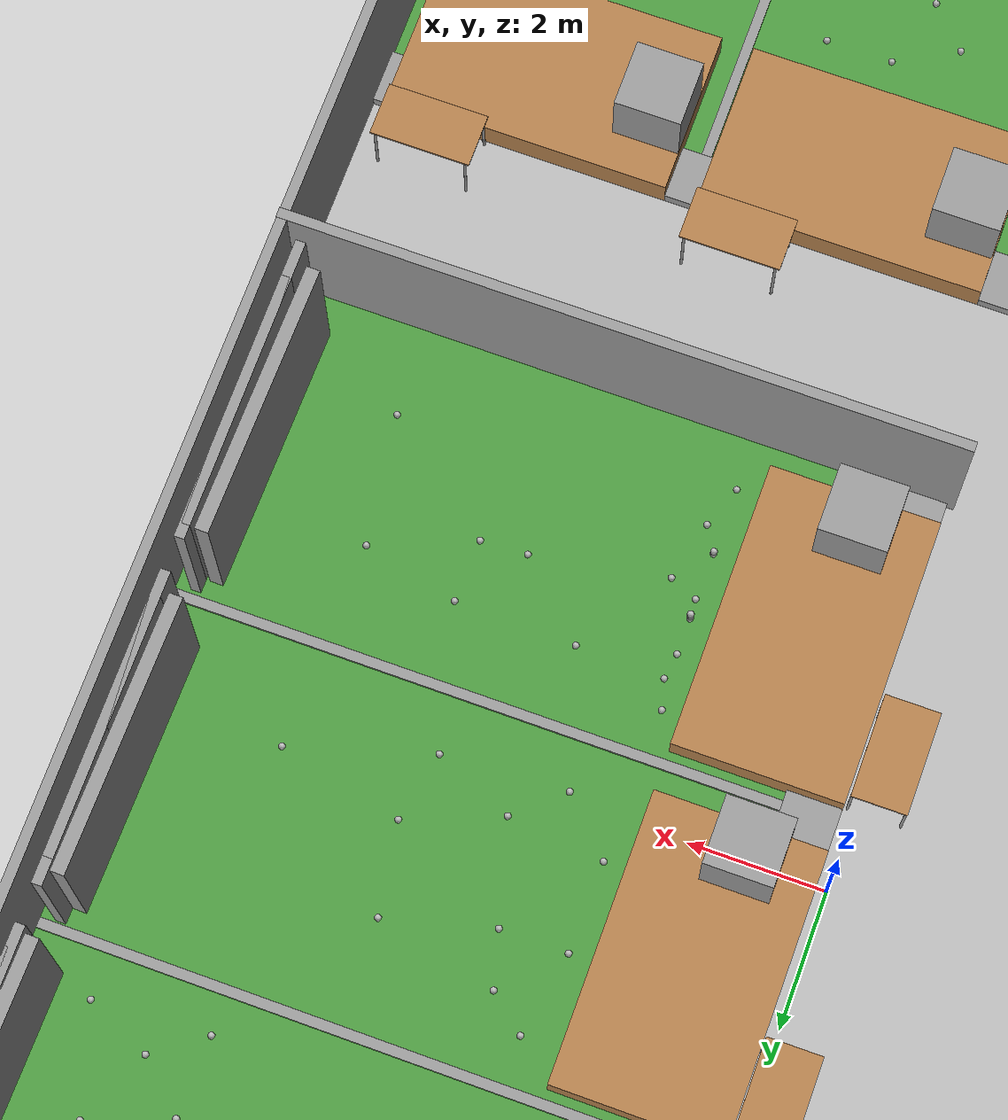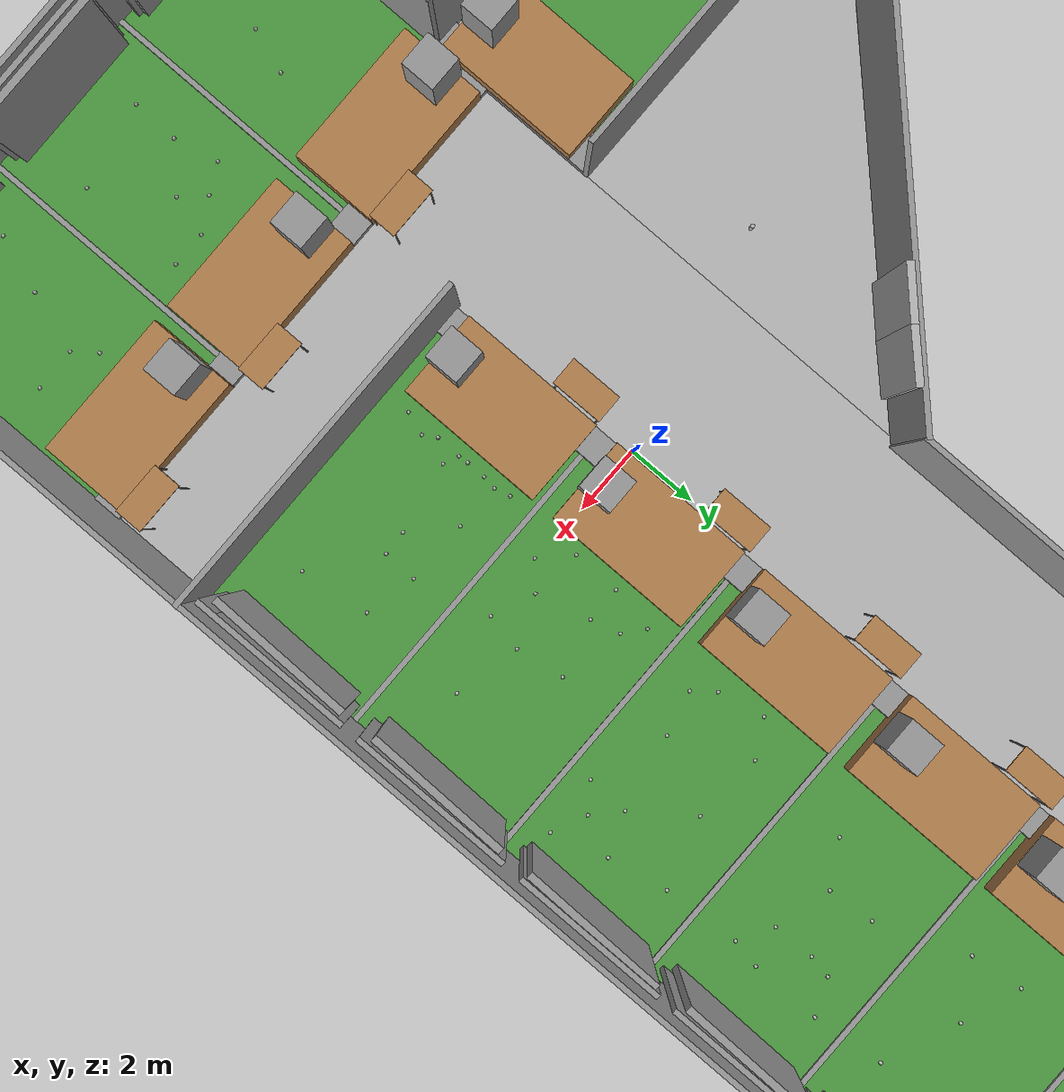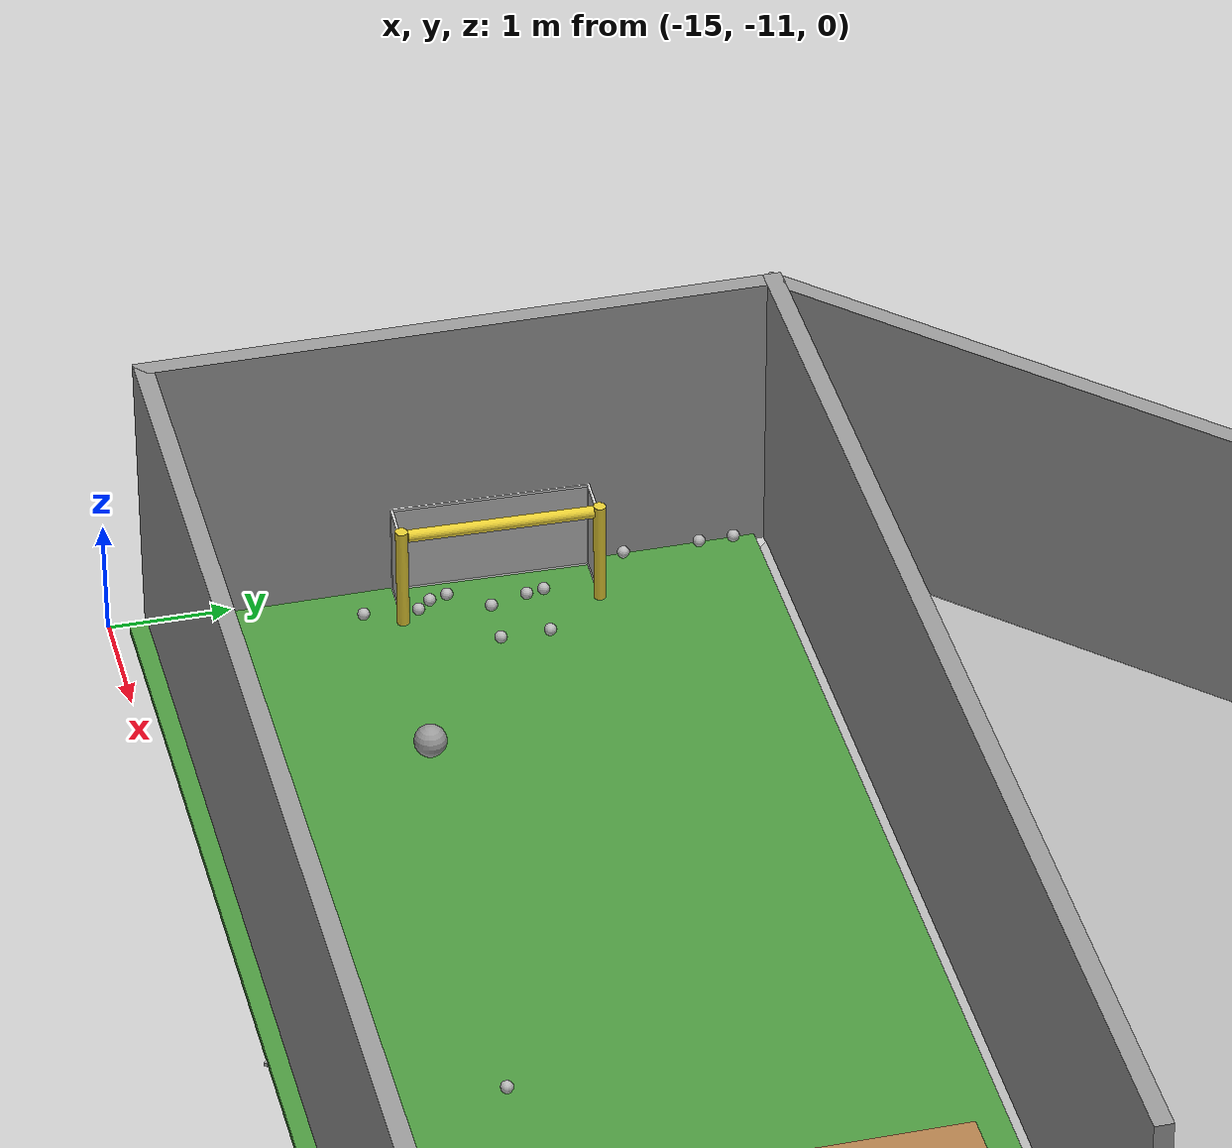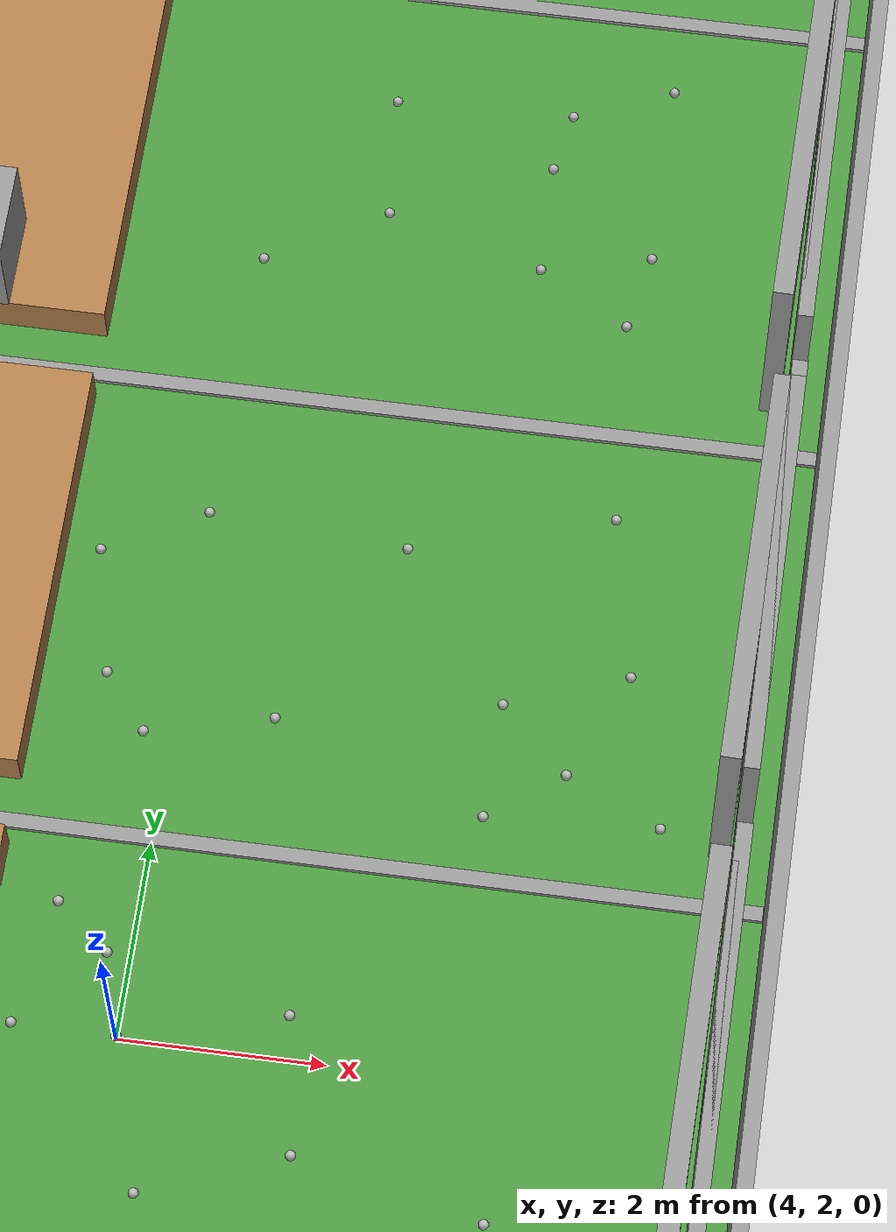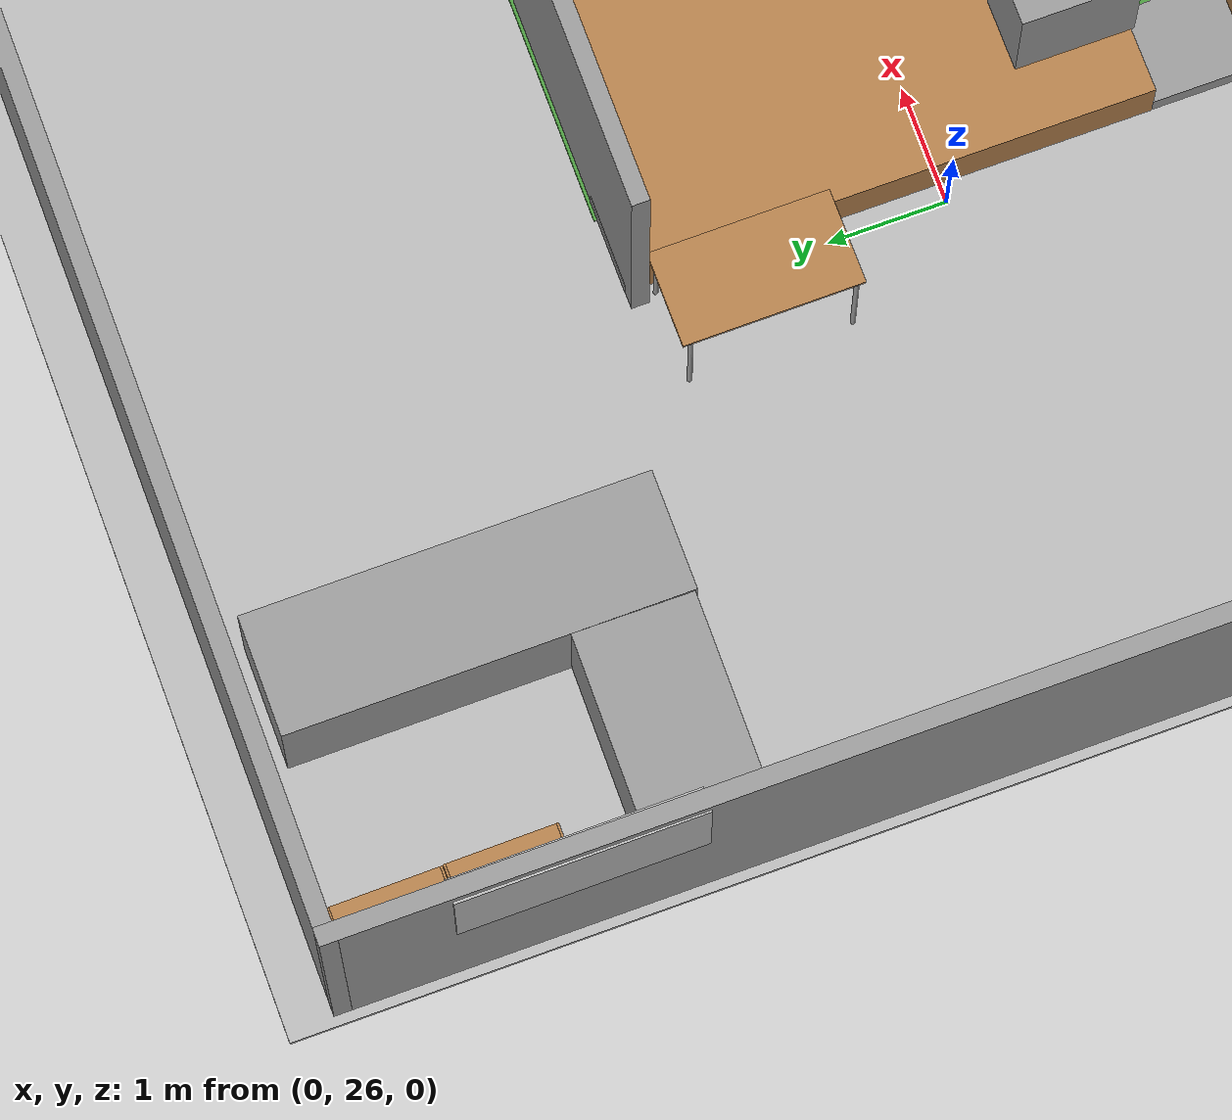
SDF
<sdf version="1.6">
 <world name="default">
  <light name="sun" type="directional">
   <pose>0 0 10 0 -0 0</pose>
   <diffuse>0.8 0.8 0.8 1</diffuse>
   <specular>0.2 0.2 0.2 1</specular>
   <attenuation>
    <range>1000</range>
    <constant>0.9</constant>
    <linear>0.01</linear>
    <quadratic>0.001</quadratic>
   </attenuation>
   <direction>-0.5 0.1 -0.9</direction>
  </light>
  <gravity>0 0 -9.8</gravity>
  <magnetic_field>6e-06 2.3e-05 -4.2e-05</magnetic_field>
  <atmosphere type="adiabatic"/>
  <physics name="default_physics" default="0" type="ode">
   <max_step_size>0.001</max_step_size>
   <real_time_factor>1</real_time_factor>
   <real_time_update_rate>1000</real_time_update_rate>
  </physics>
  <scene><ambient>0.4 0.4 0.4 1</ambient><background>0.7 0.7 0.7 1</background><shadows>1</shadows></scene>
  <audio><device>default</device></audio>
  <spherical_coordinates>
   <surface_model>EARTH_WGS84</surface_model>
   <latitude_deg>0</latitude_deg>
   <longitude_deg>0</longitude_deg>
   <elevation>0</elevation>
   <heading_deg>0</heading_deg>
  </spherical_coordinates>
  <model name="ground_plane">
   <static>1</static>
   <link name="link">
    <collision name="collision">
     <geometry><plane><normal>0 0 1</normal><size>100 100</size></plane></geometry>
     <surface>
      <contact><collide_bitmask>65535</collide_bitmask></contact>
      <friction><ode><mu>100</mu><mu2>50</mu2></ode></friction>
     </surface>
    </collision>
    <visual name="visual">
     <cast_shadows>0</cast_shadows>
     <geometry><plane><normal>0 0 1</normal><size>100 100</size></plane></geometry>
     <material>
      <script><uri>file://media/materials/scripts/gazebo.material</uri><name>Gazebo/Grey</name></script>
     </material>
    </visual>
   </link>
   <pose>-3.51447 11.9136 0 0 -0 0</pose>
  </model>
  <model name="table_clone">
   <static>1</static>
   <link name="link">
    <collision name="surface">
     <pose>0 0 1 0 -0 0</pose>
     <geometry><box><size>1.5 0.8 0.03</size></box></geometry>
     <surface><friction><ode><mu>0.6</mu><mu2>0.6</mu2></ode></friction></surface>
    </collision>
    <visual name="visual1">
     <pose>0 0 1 0 -0 0</pose>
     <geometry><box><size>1.5 0.8 0.03</size></box></geometry>
     <material>
      <script><uri>file://media/materials/scripts/gazebo.material</uri><name>Gazebo/Wood</name></script>
     </material>
    </visual>
    <collision name="front_left_leg">
     <pose>0.68 0.38 0.5 0 -0 0</pose>
     <geometry><cylinder><radius>0.02</radius><length>1</length></cylinder></geometry>
    </collision>
    <visual name="front_left_leg">
     <pose>0.68 0.38 0.5 0 -0 0</pose>
     <geometry><cylinder><radius>0.02</radius><length>1</length></cylinder></geometry>
     <material>
      <script><uri>file://media/materials/scripts/gazebo.material</uri><name>Gazebo/Grey</name></script>
     </material>
    </visual>
    <collision name="front_right_leg">
     <pose>0.68 -0.38 0.5 0 -0 0</pose>
     <geometry><cylinder><radius>0.02</radius><length>1</length></cylinder></geometry>
    </collision>
    <visual name="front_right_leg">
     <pose>0.68 -0.38 0.5 0 -0 0</pose>
     <geometry><cylinder><radius>0.02</radius><length>1</length></cylinder></geometry>
     <material>
      <script><uri>file://media/materials/scripts/gazebo.material</uri><name>Gazebo/Grey</name></script>
     </material>
    </visual>
    <collision name="back_right_leg">
     <pose>-0.68 -0.38 0.5 0 -0 0</pose>
     <geometry><cylinder><radius>0.02</radius><length>1</length></cylinder></geometry>
    </collision>
    <visual name="back_right_leg">
     <pose>-0.68 -0.38 0.5 0 -0 0</pose>
     <geometry><cylinder><radius>0.02</radius><length>1</length></cylinder></geometry>
     <material>
      <script><uri>file://media/materials/scripts/gazebo.material</uri><name>Gazebo/Grey</name></script>
     </material>
    </visual>
    <collision name="back_left_leg">
     <pose>-0.68 0.38 0.5 0 -0 0</pose>
     <geometry><cylinder><radius>0.02</radius><length>1</length></cylinder></geometry>
    </collision>
    <visual name="back_left_leg">
     <pose>-0.68 0.38 0.5 0 -0 0</pose>
     <geometry><cylinder><radius>0.02</radius><length>1</length></cylinder></geometry>
     <material>
      <script><uri>file://media/materials/scripts/gazebo.material</uri><name>Gazebo/Grey</name></script>
     </material>
    </visual>
   </link>
   <pose>-0.263897 3.07041 0 0 0 -1.56764</pose>
  </model>
  <model name="table_clone_clone">
   <static>1</static>
   <link name="link">
    <collision name="surface">
     <pose>0 0 1 0 -0 0</pose>
     <geometry><box><size>1.5 0.8 0.03</size></box></geometry>
     <surface><friction><ode><mu>0.6</mu><mu2>0.6</mu2></ode></friction></surface>
    </collision>
    <visual name="visual1">
     <pose>0 0 1 0 -0 0</pose>
     <geometry><box><size>1.5 0.8 0.03</size></box></geometry>
     <material>
      <script><uri>file://media/materials/scripts/gazebo.material</uri><name>Gazebo/Wood</name></script>
     </material>
    </visual>
    <collision name="front_left_leg">
     <pose>0.68 0.38 0.5 0 -0 0</pose>
     <geometry><cylinder><radius>0.02</radius><length>1</length></cylinder></geometry>
    </collision>
    <visual name="front_left_leg">
     <pose>0.68 0.38 0.5 0 -0 0</pose>
     <geometry><cylinder><radius>0.02</radius><length>1</length></cylinder></geometry>
     <material>
      <script><uri>file://media/materials/scripts/gazebo.material</uri><name>Gazebo/Grey</name></script>
     </material>
    </visual>
    <collision name="front_right_leg">
     <pose>0.68 -0.38 0.5 0 -0 0</pose>
     <geometry><cylinder><radius>0.02</radius><length>1</length></cylinder></geometry>
    </collision>
    <visual name="front_right_leg">
     <pose>0.68 -0.38 0.5 0 -0 0</pose>
     <geometry><cylinder><radius>0.02</radius><length>1</length></cylinder></geometry>
     <material>
      <script><uri>file://media/materials/scripts/gazebo.material</uri><name>Gazebo/Grey</name></script>
     </material>
    </visual>
    <collision name="back_right_leg">
     <pose>-0.68 -0.38 0.5 0 -0 0</pose>
     <geometry><cylinder><radius>0.02</radius><length>1</length></cylinder></geometry>
    </collision>
    <visual name="back_right_leg">
     <pose>-0.68 -0.38 0.5 0 -0 0</pose>
     <geometry><cylinder><radius>0.02</radius><length>1</length></cylinder></geometry>
     <material>
      <script><uri>file://media/materials/scripts/gazebo.material</uri><name>Gazebo/Grey</name></script>
     </material>
    </visual>
    <collision name="back_left_leg">
     <pose>-0.68 0.38 0.5 0 -0 0</pose>
     <geometry><cylinder><radius>0.02</radius><length>1</length></cylinder></geometry>
    </collision>
    <visual name="back_left_leg">
     <pose>-0.68 0.38 0.5 0 -0 0</pose>
     <geometry><cylinder><radius>0.02</radius><length>1</length></cylinder></geometry>
     <material>
      <script><uri>file://media/materials/scripts/gazebo.material</uri><name>Gazebo/Grey</name></script>
     </material>
    </visual>
   </link>
   <pose>-0.280452 -1.87389 0 0 0 -1.56764</pose>
  </model>
  <model name="table_clone_clone_0">
   <static>1</static>
   <link name="link">
    <collision name="surface">
     <pose>0 0 1 0 -0 0</pose>
     <geometry><box><size>1.5 0.8 0.03</size></box></geometry>
     <surface><friction><ode><mu>0.6</mu><mu2>0.6</mu2></ode></friction></surface>
    </collision>
    <visual name="visual1">
     <pose>0 0 1 0 -0 0</pose>
     <geometry><box><size>1.5 0.8 0.03</size></box></geometry>
     <material>
      <script><uri>file://media/materials/scripts/gazebo.material</uri><name>Gazebo/Wood</name></script>
     </material>
    </visual>
    <collision name="front_left_leg">
     <pose>0.68 0.38 0.5 0 -0 0</pose>
     <geometry><cylinder><radius>0.02</radius><length>1</length></cylinder></geometry>
    </collision>
    <visual name="front_left_leg">
     <pose>0.68 0.38 0.5 0 -0 0</pose>
     <geometry><cylinder><radius>0.02</radius><length>1</length></cylinder></geometry>
     <material>
      <script><uri>file://media/materials/scripts/gazebo.material</uri><name>Gazebo/Grey</name></script>
     </material>
    </visual>
    <collision name="front_right_leg">
     <pose>0.68 -0.38 0.5 0 -0 0</pose>
     <geometry><cylinder><radius>0.02</radius><length>1</length></cylinder></geometry>
    </collision>
    <visual name="front_right_leg">
     <pose>0.68 -0.38 0.5 0 -0 0</pose>
     <geometry><cylinder><radius>0.02</radius><length>1</length></cylinder></geometry>
     <material>
      <script><uri>file://media/materials/scripts/gazebo.material</uri><name>Gazebo/Grey</name></script>
     </material>
    </visual>
    <collision name="back_right_leg">
     <pose>-0.68 -0.38 0.5 0 -0 0</pose>
     <geometry><cylinder><radius>0.02</radius><length>1</length></cylinder></geometry>
    </collision>
    <visual name="back_right_leg">
     <pose>-0.68 -0.38 0.5 0 -0 0</pose>
     <geometry><cylinder><radius>0.02</radius><length>1</length></cylinder></geometry>
     <material>
      <script><uri>file://media/materials/scripts/gazebo.material</uri><name>Gazebo/Grey</name></script>
     </material>
    </visual>
    <collision name="back_left_leg">
     <pose>-0.68 0.38 0.5 0 -0 0</pose>
     <geometry><cylinder><radius>0.02</radius><length>1</length></cylinder></geometry>
    </collision>
    <visual name="back_left_leg">
     <pose>-0.68 0.38 0.5 0 -0 0</pose>
     <geometry><cylinder><radius>0.02</radius><length>1</length></cylinder></geometry>
     <material>
      <script><uri>file://media/materials/scripts/gazebo.material</uri><name>Gazebo/Grey</name></script>
     </material>
    </visual>
   </link>
   <pose>-0.311266 7.9439 0 0 0 -1.56764</pose>
  </model>
  <model name="table_clone_clone_1">
   <static>1</static>
   <link name="link">
    <collision name="surface">
     <pose>0 0 1 0 -0 0</pose>
     <geometry><box><size>1.5 0.8 0.03</size></box></geometry>
     <surface><friction><ode><mu>0.6</mu><mu2>0.6</mu2></ode></friction></surface>
    </collision>
    <visual name="visual1">
     <pose>0 0 1 0 -0 0</pose>
     <geometry><box><size>1.5 0.8 0.03</size></box></geometry>
     <material>
      <script><uri>file://media/materials/scripts/gazebo.material</uri><name>Gazebo/Wood</name></script>
     </material>
    </visual>
    <collision name="front_left_leg">
     <pose>0.68 0.38 0.5 0 -0 0</pose>
     <geometry><cylinder><radius>0.02</radius><length>1</length></cylinder></geometry>
    </collision>
    <visual name="front_left_leg">
     <pose>0.68 0.38 0.5 0 -0 0</pose>
     <geometry><cylinder><radius>0.02</radius><length>1</length></cylinder></geometry>
     <material>
      <script><uri>file://media/materials/scripts/gazebo.material</uri><name>Gazebo/Grey</name></script>
     </material>
    </visual>
    <collision name="front_right_leg">
     <pose>0.68 -0.38 0.5 0 -0 0</pose>
     <geometry><cylinder><radius>0.02</radius><length>1</length></cylinder></geometry>
    </collision>
    <visual name="front_right_leg">
     <pose>0.68 -0.38 0.5 0 -0 0</pose>
     <geometry><cylinder><radius>0.02</radius><length>1</length></cylinder></geometry>
     <material>
      <script><uri>file://media/materials/scripts/gazebo.material</uri><name>Gazebo/Grey</name></script>
     </material>
    </visual>
    <collision name="back_right_leg">
     <pose>-0.68 -0.38 0.5 0 -0 0</pose>
     <geometry><cylinder><radius>0.02</radius><length>1</length></cylinder></geometry>
    </collision>
    <visual name="back_right_leg">
     <pose>-0.68 -0.38 0.5 0 -0 0</pose>
     <geometry><cylinder><radius>0.02</radius><length>1</length></cylinder></geometry>
     <material>
      <script><uri>file://media/materials/scripts/gazebo.material</uri><name>Gazebo/Grey</name></script>
     </material>
    </visual>
    <collision name="back_left_leg">
     <pose>-0.68 0.38 0.5 0 -0 0</pose>
     <geometry><cylinder><radius>0.02</radius><length>1</length></cylinder></geometry>
    </collision>
    <visual name="back_left_leg">
     <pose>-0.68 0.38 0.5 0 -0 0</pose>
     <geometry><cylinder><radius>0.02</radius><length>1</length></cylinder></geometry>
     <material>
      <script><uri>file://media/materials/scripts/gazebo.material</uri><name>Gazebo/Grey</name></script>
     </material>
    </visual>
   </link>
   <pose>-0.283344 12.903 0 0 0 -1.56764</pose>
  </model>
  <model name="table_clone_clone_2">
   <static>1</static>
   <link name="link">
    <collision name="surface">
     <pose>0 0 1 0 -0 0</pose>
     <geometry><box><size>1.5 0.8 0.03</size></box></geometry>
     <surface><friction><ode><mu>0.6</mu><mu2>0.6</mu2></ode></friction></surface>
    </collision>
    <visual name="visual1">
     <pose>0 0 1 0 -0 0</pose>
     <geometry><box><size>1.5 0.8 0.03</size></box></geometry>
     <material>
      <script><uri>file://media/materials/scripts/gazebo.material</uri><name>Gazebo/Wood</name></script>
     </material>
    </visual>
    <collision name="front_left_leg">
     <pose>0.68 0.38 0.5 0 -0 0</pose>
     <geometry><cylinder><radius>0.02</radius><length>1</length></cylinder></geometry>
    </collision>
    <visual name="front_left_leg">
     <pose>0.68 0.38 0.5 0 -0 0</pose>
     <geometry><cylinder><radius>0.02</radius><length>1</length></cylinder></geometry>
     <material>
      <script><uri>file://media/materials/scripts/gazebo.material</uri><name>Gazebo/Grey</name></script>
     </material>
    </visual>
    <collision name="front_right_leg">
     <pose>0.68 -0.38 0.5 0 -0 0</pose>
     <geometry><cylinder><radius>0.02</radius><length>1</length></cylinder></geometry>
    </collision>
    <visual name="front_right_leg">
     <pose>0.68 -0.38 0.5 0 -0 0</pose>
     <geometry><cylinder><radius>0.02</radius><length>1</length></cylinder></geometry>
     <material>
      <script><uri>file://media/materials/scripts/gazebo.material</uri><name>Gazebo/Grey</name></script>
     </material>
    </visual>
    <collision name="back_right_leg">
     <pose>-0.68 -0.38 0.5 0 -0 0</pose>
     <geometry><cylinder><radius>0.02</radius><length>1</length></cylinder></geometry>
    </collision>
    <visual name="back_right_leg">
     <pose>-0.68 -0.38 0.5 0 -0 0</pose>
     <geometry><cylinder><radius>0.02</radius><length>1</length></cylinder></geometry>
     <material>
      <script><uri>file://media/materials/scripts/gazebo.material</uri><name>Gazebo/Grey</name></script>
     </material>
    </visual>
    <collision name="back_left_leg">
     <pose>-0.68 0.38 0.5 0 -0 0</pose>
     <geometry><cylinder><radius>0.02</radius><length>1</length></cylinder></geometry>
    </collision>
    <visual name="back_left_leg">
     <pose>-0.68 0.38 0.5 0 -0 0</pose>
     <geometry><cylinder><radius>0.02</radius><length>1</length></cylinder></geometry>
     <material>
      <script><uri>file://media/materials/scripts/gazebo.material</uri><name>Gazebo/Grey</name></script>
     </material>
    </visual>
   </link>
   <pose>-0.282545 17.6818 0 0 0 -1.56764</pose>
  </model>
  <model name="table_clone_clone_3">
   <static>1</static>
   <link name="link">
    <collision name="surface">
     <pose>0 0 1 0 -0 0</pose>
     <geometry><box><size>1.5 0.8 0.03</size></box></geometry>
     <surface><friction><ode><mu>0.6</mu><mu2>0.6</mu2></ode></friction></surface>
    </collision>
    <visual name="visual1">
     <pose>0 0 1 0 -0 0</pose>
     <geometry><box><size>1.5 0.8 0.03</size></box></geometry>
     <material>
      <script><uri>file://media/materials/scripts/gazebo.material</uri><name>Gazebo/Wood</name></script>
     </material>
    </visual>
    <collision name="front_left_leg">
     <pose>0.68 0.38 0.5 0 -0 0</pose>
     <geometry><cylinder><radius>0.02</radius><length>1</length></cylinder></geometry>
    </collision>
    <visual name="front_left_leg">
     <pose>0.68 0.38 0.5 0 -0 0</pose>
     <geometry><cylinder><radius>0.02</radius><length>1</length></cylinder></geometry>
     <material>
      <script><uri>file://media/materials/scripts/gazebo.material</uri><name>Gazebo/Grey</name></script>
     </material>
    </visual>
    <collision name="front_right_leg">
     <pose>0.68 -0.38 0.5 0 -0 0</pose>
     <geometry><cylinder><radius>0.02</radius><length>1</length></cylinder></geometry>
    </collision>
    <visual name="front_right_leg">
     <pose>0.68 -0.38 0.5 0 -0 0</pose>
     <geometry><cylinder><radius>0.02</radius><length>1</length></cylinder></geometry>
     <material>
      <script><uri>file://media/materials/scripts/gazebo.material</uri><name>Gazebo/Grey</name></script>
     </material>
    </visual>
    <collision name="back_right_leg">
     <pose>-0.68 -0.38 0.5 0 -0 0</pose>
     <geometry><cylinder><radius>0.02</radius><length>1</length></cylinder></geometry>
    </collision>
    <visual name="back_right_leg">
     <pose>-0.68 -0.38 0.5 0 -0 0</pose>
     <geometry><cylinder><radius>0.02</radius><length>1</length></cylinder></geometry>
     <material>
      <script><uri>file://media/materials/scripts/gazebo.material</uri><name>Gazebo/Grey</name></script>
     </material>
    </visual>
    <collision name="back_left_leg">
     <pose>-0.68 0.38 0.5 0 -0 0</pose>
     <geometry><cylinder><radius>0.02</radius><length>1</length></cylinder></geometry>
    </collision>
    <visual name="back_left_leg">
     <pose>-0.68 0.38 0.5 0 -0 0</pose>
     <geometry><cylinder><radius>0.02</radius><length>1</length></cylinder></geometry>
     <material>
      <script><uri>file://media/materials/scripts/gazebo.material</uri><name>Gazebo/Grey</name></script>
     </material>
    </visual>
   </link>
   <pose>-0.292 22.6184 0 0 0 -1.56764</pose>
  </model>
  <model name="table_clone_clone_4">
   <static>1</static>
   <link name="link">
    <collision name="surface">
     <pose>0 0 1 0 -0 0</pose>
     <geometry><box><size>1.5 0.8 0.03</size></box></geometry>
     <surface><friction><ode><mu>0.6</mu><mu2>0.6</mu2></ode></friction></surface>
    </collision>
    <visual name="visual1">
     <pose>0 0 1 0 -0 0</pose>
     <geometry><box><size>1.5 0.8 0.03</size></box></geometry>
     <material>
      <script><uri>file://media/materials/scripts/gazebo.material</uri><name>Gazebo/Wood</name></script>
     </material>
    </visual>
    <collision name="front_left_leg">
     <pose>0.68 0.38 0.5 0 -0 0</pose>
     <geometry><cylinder><radius>0.02</radius><length>1</length></cylinder></geometry>
    </collision>
    <visual name="front_left_leg">
     <pose>0.68 0.38 0.5 0 -0 0</pose>
     <geometry><cylinder><radius>0.02</radius><length>1</length></cylinder></geometry>
     <material>
      <script><uri>file://media/materials/scripts/gazebo.material</uri><name>Gazebo/Grey</name></script>
     </material>
    </visual>
    <collision name="front_right_leg">
     <pose>0.68 -0.38 0.5 0 -0 0</pose>
     <geometry><cylinder><radius>0.02</radius><length>1</length></cylinder></geometry>
    </collision>
    <visual name="front_right_leg">
     <pose>0.68 -0.38 0.5 0 -0 0</pose>
     <geometry><cylinder><radius>0.02</radius><length>1</length></cylinder></geometry>
     <material>
      <script><uri>file://media/materials/scripts/gazebo.material</uri><name>Gazebo/Grey</name></script>
     </material>
    </visual>
    <collision name="back_right_leg">
     <pose>-0.68 -0.38 0.5 0 -0 0</pose>
     <geometry><cylinder><radius>0.02</radius><length>1</length></cylinder></geometry>
    </collision>
    <visual name="back_right_leg">
     <pose>-0.68 -0.38 0.5 0 -0 0</pose>
     <geometry><cylinder><radius>0.02</radius><length>1</length></cylinder></geometry>
     <material>
      <script><uri>file://media/materials/scripts/gazebo.material</uri><name>Gazebo/Grey</name></script>
     </material>
    </visual>
    <collision name="back_left_leg">
     <pose>-0.68 0.38 0.5 0 -0 0</pose>
     <geometry><cylinder><radius>0.02</radius><length>1</length></cylinder></geometry>
    </collision>
    <visual name="back_left_leg">
     <pose>-0.68 0.38 0.5 0 -0 0</pose>
     <geometry><cylinder><radius>0.02</radius><length>1</length></cylinder></geometry>
     <material>
      <script><uri>file://media/materials/scripts/gazebo.material</uri><name>Gazebo/Grey</name></script>
     </material>
    </visual>
   </link>
   <pose>-0.3 27.7319 0 0 0 -1.56764</pose>
  </model>
  <model name="table_clone_clone_5">
   <static>1</static>
   <link name="link">
    <collision name="surface">
     <pose>0 0 1 0 -0 0</pose>
     <geometry><box><size>1.5 0.8 0.03</size></box></geometry>
     <surface><friction><ode><mu>0.6</mu><mu2>0.6</mu2></ode></friction></surface>
    </collision>
    <visual name="visual1">
     <pose>0 0 1 0 -0 0</pose>
     <geometry><box><size>1.5 0.8 0.03</size></box></geometry>
     <material>
      <script><uri>file://media/materials/scripts/gazebo.material</uri><name>Gazebo/Wood</name></script>
     </material>
    </visual>
    <collision name="front_left_leg">
     <pose>0.68 0.38 0.5 0 -0 0</pose>
     <geometry><cylinder><radius>0.02</radius><length>1</length></cylinder></geometry>
    </collision>
    <visual name="front_left_leg">
     <pose>0.68 0.38 0.5 0 -0 0</pose>
     <geometry><cylinder><radius>0.02</radius><length>1</length></cylinder></geometry>
     <material>
      <script><uri>file://media/materials/scripts/gazebo.material</uri><name>Gazebo/Grey</name></script>
     </material>
    </visual>
    <collision name="front_right_leg">
     <pose>0.68 -0.38 0.5 0 -0 0</pose>
     <geometry><cylinder><radius>0.02</radius><length>1</length></cylinder></geometry>
    </collision>
    <visual name="front_right_leg">
     <pose>0.68 -0.38 0.5 0 -0 0</pose>
     <geometry><cylinder><radius>0.02</radius><length>1</length></cylinder></geometry>
     <material>
      <script><uri>file://media/materials/scripts/gazebo.material</uri><name>Gazebo/Grey</name></script>
     </material>
    </visual>
    <collision name="back_right_leg">
     <pose>-0.68 -0.38 0.5 0 -0 0</pose>
     <geometry><cylinder><radius>0.02</radius><length>1</length></cylinder></geometry>
    </collision>
    <visual name="back_right_leg">
     <pose>-0.68 -0.38 0.5 0 -0 0</pose>
     <geometry><cylinder><radius>0.02</radius><length>1</length></cylinder></geometry>
     <material>
      <script><uri>file://media/materials/scripts/gazebo.material</uri><name>Gazebo/Grey</name></script>
     </material>
    </visual>
    <collision name="back_left_leg">
     <pose>-0.68 0.38 0.5 0 -0 0</pose>
     <geometry><cylinder><radius>0.02</radius><length>1</length></cylinder></geometry>
    </collision>
    <visual name="back_left_leg">
     <pose>-0.68 0.38 0.5 0 -0 0</pose>
     <geometry><cylinder><radius>0.02</radius><length>1</length></cylinder></geometry>
     <material>
      <script><uri>file://media/materials/scripts/gazebo.material</uri><name>Gazebo/Grey</name></script>
     </material>
    </visual>
   </link>
   <pose>8.83949 -8.39116 0 0 -0 0</pose>
  </model>
  <model name="table_clone_clone_5_clone">
   <static>1</static>
   <link name="link">
    <collision name="surface">
     <pose>0 0 1 0 -0 0</pose>
     <geometry><box><size>1.5 0.8 0.03</size></box></geometry>
     <surface><friction><ode><mu>0.6</mu><mu2>0.6</mu2></ode></friction></surface>
    </collision>
    <visual name="visual1">
     <pose>0 0 1 0 -0 0</pose>
     <geometry><box><size>1.5 0.8 0.03</size></box></geometry>
     <material>
      <script><uri>file://media/materials/scripts/gazebo.material</uri><name>Gazebo/Wood</name></script>
     </material>
    </visual>
    <collision name="front_left_leg">
     <pose>0.68 0.38 0.5 0 -0 0</pose>
     <geometry><cylinder><radius>0.02</radius><length>1</length></cylinder></geometry>
    </collision>
    <visual name="front_left_leg">
     <pose>0.68 0.38 0.5 0 -0 0</pose>
     <geometry><cylinder><radius>0.02</radius><length>1</length></cylinder></geometry>
     <material>
      <script><uri>file://media/materials/scripts/gazebo.material</uri><name>Gazebo/Grey</name></script>
     </material>
    </visual>
    <collision name="front_right_leg">
     <pose>0.68 -0.38 0.5 0 -0 0</pose>
     <geometry><cylinder><radius>0.02</radius><length>1</length></cylinder></geometry>
    </collision>
    <visual name="front_right_leg">
     <pose>0.68 -0.38 0.5 0 -0 0</pose>
     <geometry><cylinder><radius>0.02</radius><length>1</length></cylinder></geometry>
     <material>
      <script><uri>file://media/materials/scripts/gazebo.material</uri><name>Gazebo/Grey</name></script>
     </material>
    </visual>
    <collision name="back_right_leg">
     <pose>-0.68 -0.38 0.5 0 -0 0</pose>
     <geometry><cylinder><radius>0.02</radius><length>1</length></cylinder></geometry>
    </collision>
    <visual name="back_right_leg">
     <pose>-0.68 -0.38 0.5 0 -0 0</pose>
     <geometry><cylinder><radius>0.02</radius><length>1</length></cylinder></geometry>
     <material>
      <script><uri>file://media/materials/scripts/gazebo.material</uri><name>Gazebo/Grey</name></script>
     </material>
    </visual>
    <collision name="back_left_leg">
     <pose>-0.68 0.38 0.5 0 -0 0</pose>
     <geometry><cylinder><radius>0.02</radius><length>1</length></cylinder></geometry>
    </collision>
    <visual name="back_left_leg">
     <pose>-0.68 0.38 0.5 0 -0 0</pose>
     <geometry><cylinder><radius>0.02</radius><length>1</length></cylinder></geometry>
     <material>
      <script><uri>file://media/materials/scripts/gazebo.material</uri><name>Gazebo/Grey</name></script>
     </material>
    </visual>
   </link>
   <pose>4.1841 -8.37674 0 0 -0 0</pose>
  </model>
  <model name="table_clone_clone_5_clone_0">
   <static>1</static>
   <link name="link">
    <collision name="surface">
     <pose>0 0 1 0 -0 0</pose>
     <geometry><box><size>1.5 0.8 0.03</size></box></geometry>
     <surface><friction><ode><mu>0.6</mu><mu2>0.6</mu2></ode></friction></surface>
    </collision>
    <visual name="visual1">
     <pose>0 0 1 0 -0 0</pose>
     <geometry><box><size>1.5 0.8 0.03</size></box></geometry>
     <material>
      <script><uri>file://media/materials/scripts/gazebo.material</uri><name>Gazebo/Wood</name></script>
     </material>
    </visual>
    <collision name="front_left_leg">
     <pose>0.68 0.38 0.5 0 -0 0</pose>
     <geometry><cylinder><radius>0.02</radius><length>1</length></cylinder></geometry>
    </collision>
    <visual name="front_left_leg">
     <pose>0.68 0.38 0.5 0 -0 0</pose>
     <geometry><cylinder><radius>0.02</radius><length>1</length></cylinder></geometry>
     <material>
      <script><uri>file://media/materials/scripts/gazebo.material</uri><name>Gazebo/Grey</name></script>
     </material>
    </visual>
    <collision name="front_right_leg">
     <pose>0.68 -0.38 0.5 0 -0 0</pose>
     <geometry><cylinder><radius>0.02</radius><length>1</length></cylinder></geometry>
    </collision>
    <visual name="front_right_leg">
     <pose>0.68 -0.38 0.5 0 -0 0</pose>
     <geometry><cylinder><radius>0.02</radius><length>1</length></cylinder></geometry>
     <material>
      <script><uri>file://media/materials/scripts/gazebo.material</uri><name>Gazebo/Grey</name></script>
     </material>
    </visual>
    <collision name="back_right_leg">
     <pose>-0.68 -0.38 0.5 0 -0 0</pose>
     <geometry><cylinder><radius>0.02</radius><length>1</length></cylinder></geometry>
    </collision>
    <visual name="back_right_leg">
     <pose>-0.68 -0.38 0.5 0 -0 0</pose>
     <geometry><cylinder><radius>0.02</radius><length>1</length></cylinder></geometry>
     <material>
      <script><uri>file://media/materials/scripts/gazebo.material</uri><name>Gazebo/Grey</name></script>
     </material>
    </visual>
    <collision name="back_left_leg">
     <pose>-0.68 0.38 0.5 0 -0 0</pose>
     <geometry><cylinder><radius>0.02</radius><length>1</length></cylinder></geometry>
    </collision>
    <visual name="back_left_leg">
     <pose>-0.68 0.38 0.5 0 -0 0</pose>
     <geometry><cylinder><radius>0.02</radius><length>1</length></cylinder></geometry>
     <material>
      <script><uri>file://media/materials/scripts/gazebo.material</uri><name>Gazebo/Grey</name></script>
     </material>
    </visual>
   </link>
   <pose>-0.816001 -8.38126 0 0 -0 0</pose>
  </model>
  <model name="bookshelf">
   <static>1</static>
   <link name="link">
    <inertial><mass>1</mass></inertial>
    <collision name="back">
     <pose>0 0.005 0.6 0 -0 0</pose>
     <geometry><box><size>0.9 0.01 1.2</size></box></geometry>
    </collision>
    <visual name="visual1">
     <pose>0 0.005 0.6 0 -0 0</pose>
     <geometry><box><size>0.9 0.01 1.2</size></box></geometry>
     <material>
      <script><uri>file://media/materials/scripts/gazebo.material</uri><name>Gazebo/Wood</name></script>
     </material>
    </visual>
    <collision name="left_side">
     <pose>0.45 -0.195 0.6 0 -0 0</pose>
     <geometry><box><size>0.02 0.4 1.2</size></box></geometry>
    </collision>
    <visual name="visual2">
     <pose>0.45 -0.195 0.6 0 -0 0</pose>
     <geometry><box><size>0.02 0.4 1.2</size></box></geometry>
     <material>
      <script><uri>file://media/materials/scripts/gazebo.material</uri><name>Gazebo/Wood</name></script>
     </material>
    </visual>
    <collision name="right_side">
     <pose>-0.45 -0.195 0.6 0 -0 0</pose>
     <geometry><box><size>0.02 0.4 1.2</size></box></geometry>
    </collision>
    <visual name="visual3">
     <pose>-0.45 -0.195 0.6 0 -0 0</pose>
     <geometry><box><size>0.02 0.4 1.2</size></box></geometry>
     <material>
      <script><uri>file://media/materials/scripts/gazebo.material</uri><name>Gazebo/Wood</name></script>
     </material>
    </visual>
    <collision name="bottom">
     <pose>0 -0.195 0.03 0 -0 0</pose>
     <geometry><box><size>0.88 0.4 0.06</size></box></geometry>
    </collision>
    <visual name="visual4">
     <pose>0 -0.195 0.03 0 -0 0</pose>
     <geometry><box><size>0.88 0.4 0.06</size></box></geometry>
     <material>
      <script><uri>file://media/materials/scripts/gazebo.material</uri><name>Gazebo/Wood</name></script>
     </material>
    </visual>
    <collision name="top">
     <pose>0 -0.195 1.19 0 -0 0</pose>
     <geometry><box><size>0.88 0.4 0.02</size></box></geometry>
    </collision>
    <visual name="visual5">
     <pose>0 -0.195 1.19 0 -0 0</pose>
     <geometry><box><size>0.88 0.4 0.02</size></box></geometry>
     <material>
      <script><uri>file://media/materials/scripts/gazebo.material</uri><name>Gazebo/Wood</name></script>
     </material>
    </visual>
    <collision name="low_shelf">
     <pose>0 -0.195 0.43 0 -0 0</pose>
     <geometry><box><size>0.88 0.4 0.02</size></box></geometry>
    </collision>
    <visual name="visual6">
     <pose>0 -0.195 0.43 0 -0 0</pose>
     <geometry><box><size>0.88 0.4 0.02</size></box></geometry>
     <material>
      <script><uri>file://media/materials/scripts/gazebo.material</uri><name>Gazebo/Wood</name></script>
     </material>
    </visual>
    <collision name="high_shelf">
     <pose>0 -0.195 0.8 0 -0 0</pose>
     <geometry><box><size>0.88 0.4 0.02</size></box></geometry>
    </collision>
    <visual name="visual7">
     <pose>0 -0.195 0.8 0 -0 0</pose>
     <geometry><box><size>0.88 0.4 0.02</size></box></geometry>
     <material>
      <script><uri>file://media/materials/scripts/gazebo.material</uri><name>Gazebo/Wood</name></script>
     </material>
    </visual>
   </link>
   <pose>-4.34494 32.0429 0 0 -0 1.57907</pose>
  </model>
  <model name="L_wall_wood">
   <pose>1.29872 -8.7033 0 0 -0 0</pose>
   <link name="Wall_14">
    <collision name="Wall_14_Collision">
     <geometry><box><size>4.25 2.5 0.5</size></box></geometry>
     <pose>0 0 0.25 0 -0 0</pose>
    </collision>
    <visual name="Wall_14_Visual">
     <pose>0 0 0.25 0 -0 0</pose>
     <geometry><box><size>4.25 2.5 0.5</size></box></geometry>
     <material>
      <script><uri>file://media/materials/scripts/gazebo.material</uri><name>Gazebo/Wood</name></script>
      <ambient>1 1 1 1</ambient>
     </material>
     <meta><layer>0</layer></meta>
    </visual>
    <pose>6.238 -1.377 0 0 -0 0</pose>
   </link>
   <link name="Wall_16">
    <collision name="Wall_16_Collision">
     <geometry><box><size>4.25 2.5 0.5</size></box></geometry>
     <pose>0 0 0.25 0 -0 0</pose>
    </collision>
    <visual name="Wall_16_Visual">
     <pose>0 0 0.25 0 -0 0</pose>
     <geometry><box><size>4.25 2.5 0.5</size></box></geometry>
     <material>
      <script><uri>file://media/materials/scripts/gazebo.material</uri><name>Gazebo/Wood</name></script>
      <ambient>1 1 1 1</ambient>
     </material>
     <meta><layer>0</layer></meta>
    </visual>
    <pose>1.505 -1.377 0 0 -0 3.14159</pose>
   </link>
   <link name="Wall_18">
    <collision name="Wall_18_Collision">
     <geometry><box><size>4.25 2.5 0.5</size></box></geometry>
     <pose>0 0 0.25 0 -0 0</pose>
    </collision>
    <visual name="Wall_18_Visual">
     <pose>0 0 0.25 0 -0 0</pose>
     <geometry><box><size>4.25 2.5 0.5</size></box></geometry>
     <material>
      <script><uri>file://media/materials/scripts/gazebo.material</uri><name>Gazebo/Wood</name></script>
      <ambient>1 1 1 1</ambient>
     </material>
     <meta><layer>0</layer></meta>
    </visual>
    <pose>-3.485 -1.377 0 0 -0 3.14159</pose>
   </link>
   <link name="Wall_20">
    <collision name="Wall_20_Collision">
     <geometry><box><size>4.25 2.5 0.5</size></box></geometry>
     <pose>0 0 0.25 0 -0 0</pose>
    </collision>
    <visual name="Wall_20_Visual">
     <pose>0 0 0.25 0 -0 0</pose>
     <geometry><box><size>4.25 2.5 0.5</size></box></geometry>
     <material>
      <script><uri>file://media/materials/scripts/gazebo.material</uri><name>Gazebo/Wood</name></script>
      <ambient>1 1 1 1</ambient>
     </material>
     <meta><layer>0</layer></meta>
    </visual>
    <pose>-7.113 0.502 0 0 -0 1.5708</pose>
   </link>
   <static>1</static>
  </model>
  <model name="screen_1">
   <pose>9.6 6.558 0 0 -0 0</pose>
   <link name="Wall_15">
    <collision name="Wall_15_Collision">
     <geometry><box><size>4.65 0.15 2.5</size></box></geometry>
     <pose>0 0 1.25 0 -0 0</pose>
    </collision>
    <visual name="Wall_15_Visual">
     <pose>0 0 1.25 0 -0 0</pose>
     <geometry><box><size>4.65 0.15 2.5</size></box></geometry>
     <material>
      <script><uri>file://media/materials/scripts/gazebo.material</uri><name>Gazebo/Grey</name></script>
      <ambient>1 1 1 1</ambient>
     </material>
     <meta><layer>0</layer></meta>
    </visual>
    <pose>0 9.7845 0 0 -0 -1.5708</pose>
   </link>
   <link name="Wall_17">
    <collision name="Wall_17_Collision">
     <geometry><box><size>4.5 0.15 2.5</size></box></geometry>
     <pose>0 0 1.25 0 -0 0</pose>
    </collision>
    <visual name="Wall_17_Visual">
     <pose>0 0 1.25 0 -0 0</pose>
     <geometry><box><size>4.5 0.15 2.5</size></box></geometry>
     <material>
      <script><uri>file://media/materials/scripts/gazebo.material</uri><name>Gazebo/Grey</name></script>
      <ambient>1 1 1 1</ambient>
     </material>
     <meta><layer>0</layer></meta>
    </visual>
    <pose>0 4.8855 0 0 -0 -1.5708</pose>
   </link>
   <link name="Wall_19">
    <collision name="Wall_19_Collision">
     <geometry><box><size>4.25 0.15 2.5</size></box></geometry>
     <pose>0 0 1.25 0 -0 0</pose>
    </collision>
    <visual name="Wall_19_Visual">
     <pose>0 0 1.25 0 -0 0</pose>
     <geometry><box><size>4.25 0.15 2.5</size></box></geometry>
     <material>
      <script><uri>file://media/materials/scripts/gazebo.material</uri><name>Gazebo/Grey</name></script>
      <ambient>1 1 1 1</ambient>
     </material>
     <meta><layer>0</layer></meta>
    </visual>
    <pose>0 0.028499 0 0 -0 -1.5708</pose>
   </link>
   <link name="Wall_21">
    <collision name="Wall_21_Collision">
     <geometry><box><size>4.5 0.15 2.5</size></box></geometry>
     <pose>0 0 1.25 0 -0 0</pose>
    </collision>
    <visual name="Wall_21_Visual">
     <pose>0 0 1.25 0 -0 0</pose>
     <geometry><box><size>4.5 0.15 2.5</size></box></geometry>
     <material>
      <script><uri>file://media/materials/scripts/gazebo.material</uri><name>Gazebo/Grey</name></script>
      <ambient>1 1 1 1</ambient>
     </material>
     <meta><layer>0</layer></meta>
    </visual>
    <pose>0 -4.8845 0 0 -0 1.5708</pose>
   </link>
   <link name="Wall_23">
    <collision name="Wall_23_Collision">
     <geometry><box><size>4.5 0.15 2.5</size></box></geometry>
     <pose>0 0 1.25 0 -0 0</pose>
    </collision>
    <visual name="Wall_23_Visual">
     <pose>0 0 1.25 0 -0 0</pose>
     <geometry><box><size>4.5 0.15 2.5</size></box></geometry>
     <material>
      <script><uri>file://media/materials/scripts/gazebo.material</uri><name>Gazebo/Grey</name></script>
      <ambient>1 1 1 1</ambient>
     </material>
     <meta><layer>0</layer></meta>
    </visual>
    <pose>0 -9.8595 0 0 -0 -1.5708</pose>
   </link>
   <static>1</static>
  </model>
  <model name="screen">
   <pose>9.6 11.7963 0 0 -0 0</pose>
   <link name="Wall_0">
    <collision name="Wall_0_Collision">
     <geometry><box><size>3.75 0.15 2.5</size></box></geometry>
     <pose>0 0 1.25 0 -0 0</pose>
    </collision>
    <visual name="Wall_0_Visual">
     <pose>0 0 1.25 0 -0 0</pose>
     <geometry><box><size>3.75 0.15 2.5</size></box></geometry>
     <material>
      <script><uri>file://media/materials/scripts/gazebo.material</uri><name>Gazebo/Grey</name></script>
      <ambient>1 1 1 1</ambient>
     </material>
     <meta><layer>0</layer></meta>
    </visual>
    <pose>0 -14.926 0 0 -0 -1.5708</pose>
   </link>
   <link name="Wall_11">
    <collision name="Wall_11_Collision">
     <geometry><box><size>4.3 0.15 2.5</size></box></geometry>
     <pose>0 0 1.25 0 -0 0</pose>
    </collision>
    <visual name="Wall_11_Visual">
     <pose>0 0 1.25 0 -0 0</pose>
     <geometry><box><size>4.3 0.15 2.5</size></box></geometry>
     <material>
      <script><uri>file://media/materials/scripts/gazebo.material</uri><name>Gazebo/Grey</name></script>
      <ambient>1 1 1 1</ambient>
     </material>
     <meta><layer>0</layer></meta>
    </visual>
    <pose>0 9.451 0 0 -0 1.5708</pose>
   </link>
   <link name="Wall_13">
    <collision name="Wall_13_Collision">
     <geometry><box><size>4.5 0.15 2.5</size></box></geometry>
     <pose>0 0 1.25 0 -0 0</pose>
    </collision>
    <visual name="Wall_13_Visual">
     <pose>0 0 1.25 0 -0 0</pose>
     <geometry><box><size>4.5 0.15 2.5</size></box></geometry>
     <material>
      <script><uri>file://media/materials/scripts/gazebo.material</uri><name>Gazebo/Grey</name></script>
      <ambient>1 1 1 1</ambient>
     </material>
     <meta><layer>0</layer></meta>
    </visual>
    <pose>0 14.551 0 0 -0 1.5708</pose>
   </link>
   <link name="Wall_2">
    <collision name="Wall_2_Collision">
     <geometry><box><size>3.75 0.15 2.5</size></box></geometry>
     <pose>0 0 1.25 0 -0 0</pose>
    </collision>
    <visual name="Wall_2_Visual">
     <pose>0 0 1.25 0 -0 0</pose>
     <geometry><box><size>3.75 0.15 2.5</size></box></geometry>
     <material>
      <script><uri>file://media/materials/scripts/gazebo.material</uri><name>Gazebo/Grey</name></script>
      <ambient>1 1 1 1</ambient>
     </material>
     <meta><layer>0</layer></meta>
    </visual>
    <pose>0 -10.129 0 0 -0 -1.5708</pose>
   </link>
   <link name="Wall_4">
    <collision name="Wall_4_Collision">
     <geometry><box><size>3.75 0.15 2.5</size></box></geometry>
     <pose>0 0 1.25 0 -0 0</pose>
    </collision>
    <visual name="Wall_4_Visual">
     <pose>0 0 1.25 0 -0 0</pose>
     <geometry><box><size>3.75 0.15 2.5</size></box></geometry>
     <material>
      <script><uri>file://media/materials/scripts/gazebo.material</uri><name>Gazebo/Grey</name></script>
      <ambient>1 1 1 1</ambient>
     </material>
     <meta><layer>0</layer></meta>
    </visual>
    <pose>0 -5.126 0 0 -0 1.5708</pose>
   </link>
   <link name="Wall_6">
    <collision name="Wall_6_Collision">
     <geometry><box><size>3.75 0.15 2.5</size></box></geometry>
     <pose>0 0 1.25 0 -0 0</pose>
    </collision>
    <visual name="Wall_6_Visual">
     <pose>0 0 1.25 0 -0 0</pose>
     <geometry><box><size>3.75 0.15 2.5</size></box></geometry>
     <material>
      <script><uri>file://media/materials/scripts/gazebo.material</uri><name>Gazebo/Grey</name></script>
      <ambient>1 1 1 1</ambient>
     </material>
     <meta><layer>0</layer></meta>
    </visual>
    <pose>0 -0.324 0 0 -0 1.5708</pose>
   </link>
   <link name="Wall_9">
    <collision name="Wall_9_Collision">
     <geometry><box><size>3.75 0.15 2.5</size></box></geometry>
     <pose>0 0 1.25 0 -0 0</pose>
    </collision>
    <visual name="Wall_9_Visual">
     <pose>0 0 1.25 0 -0 0</pose>
     <geometry><box><size>3.75 0.15 2.5</size></box></geometry>
     <material>
      <script><uri>file://media/materials/scripts/gazebo.material</uri><name>Gazebo/Grey</name></script>
      <ambient>1 1 1 1</ambient>
     </material>
     <meta><layer>0</layer></meta>
    </visual>
    <pose>0 4.576 0 0 -0 1.5708</pose>
   </link>
   <static>1</static>
  </model>
  <model name="cut_wall">
   <pose>2.54547 -16.9287 0 0 -0 0</pose>
   <link name="Wall_25">
    <collision name="Wall_25_Collision">
     <geometry><box><size>4.25 0.15 2.5</size></box></geometry>
     <pose>0 0 1.25 0 -0 0</pose>
    </collision>
    <visual name="Wall_25_Visual">
     <pose>0 0 1.25 0 -0 0</pose>
     <geometry><box><size>4.25 0.15 2.5</size></box></geometry>
     <material>
      <script><uri>file://media/materials/scripts/gazebo.material</uri><name>Gazebo/Grey</name></script>
      <ambient>1 1 1 1</ambient>
     </material>
     <meta><layer>0</layer></meta>
    </visual>
    <pose>-4.893 0 0 0 -0 0</pose>
   </link>
   <link name="Wall_27">
    <collision name="Wall_27_Collision">
     <geometry><box><size>4.25 0.15 2.5</size></box></geometry>
     <pose>0 0 1.25 0 -0 0</pose>
    </collision>
    <visual name="Wall_27_Visual">
     <pose>0 0 1.25 0 -0 0</pose>
     <geometry><box><size>4.25 0.15 2.5</size></box></geometry>
     <material>
      <script><uri>file://media/materials/scripts/gazebo.material</uri><name>Gazebo/Grey</name></script>
      <ambient>1 1 1 1</ambient>
     </material>
     <meta><layer>0</layer></meta>
    </visual>
    <pose>-0.022 0 0 0 -0 3.14159</pose>
   </link>
   <link name="Wall_29">
    <collision name="Wall_29_Collision">
     <geometry><box><size>4.25 0.15 2.5</size></box></geometry>
     <pose>0 0 1.25 0 -0 0</pose>
    </collision>
    <visual name="Wall_29_Visual">
     <pose>0 0 1.25 0 -0 0</pose>
     <geometry><box><size>4.25 0.15 2.5</size></box></geometry>
     <material>
      <script><uri>file://media/materials/scripts/gazebo.material</uri><name>Gazebo/Grey</name></script>
      <ambient>1 1 1 1</ambient>
     </material>
     <meta><layer>0</layer></meta>
    </visual>
    <pose>4.893 0 0 0 -0 0</pose>
   </link>
   <static>1</static>
  </model>
  <model name="grass_plane_0">
   <static>1</static>
   <link name="link">
    <collision name="collision"><geometry><box><size>14.6151 7.48986 0.1</size></box></geometry></collision>
    <visual name="visual">
     <cast_shadows>0</cast_shadows>
     <geometry><box><size>14.6151 7.48986 0.1</size></box></geometry>
     <material>
      <script>
       <uri>model://grass_plane/materials/scripts</uri>
       <uri>model://grass_plane/materials/textures</uri>
       <name>vrc/grass</name>
      </script>
     </material>
    </visual>
   </link>
   <pose>2.64271 -13.3732 0 0 -0 0</pose>
  </model>
  <model name="grass_plane_1">
   <static>1</static>
   <link name="link">
    <collision name="collision"><geometry><box><size>9.36051 5.16691 0.1</size></box></geometry></collision>
    <visual name="visual">
     <cast_shadows>0</cast_shadows>
     <geometry><box><size>9.36051 5.16691 0.1</size></box></geometry>
     <material>
      <script>
       <uri>model://grass_plane/materials/scripts</uri>
       <uri>model://grass_plane/materials/textures</uri>
       <name>vrc/grass</name>
      </script>
     </material>
    </visual>
   </link>
   <pose>-10.2269 -8.25801 -0 0 -0 0</pose>
  </model>
  <model name="grey_wall">
   <static>1</static>
   <link name="link">
    <pose>0 0 1.4 0 -0 0</pose>
    <collision name="collision"><geometry><box><size>4 0.2 2.4</size></box></geometry></collision>
    <visual name="visual">
     <cast_shadows>0</cast_shadows>
     <geometry><box><size>4 0.2 2.4</size></box></geometry>
     <material>
      <script>
       <uri>model://grey_wall/materials/scripts</uri>
       <uri>model://grey_wall/materials/textures</uri>
       <name>vrc/grey_wall</name>
      </script>
     </material>
    </visual>
   </link>
   <pose>9.4214 26.2681 -0.13155 0 0 -1.58718</pose>
  </model>
  <model name="grey_wall_clone">
   <static>1</static>
   <link name="link">
    <pose>0 0 1.4 0 -0 0</pose>
    <collision name="collision"><geometry><box><size>4 0.2 2.4</size></box></geometry></collision>
    <visual name="visual">
     <cast_shadows>0</cast_shadows>
     <geometry><box><size>4 0.2 2.4</size></box></geometry>
     <material>
      <script>
       <uri>model://grey_wall/materials/scripts</uri>
       <uri>model://grey_wall/materials/textures</uri>
       <name>vrc/grey_wall</name>
      </script>
     </material>
    </visual>
   </link>
   <pose>9.4357 21.2475 -0.13155 0 0 -1.58718</pose>
  </model>
  <model name="grey_wall_clone_0">
   <static>1</static>
   <link name="link">
    <pose>0 0 1.4 0 -0 0</pose>
    <collision name="collision"><geometry><box><size>4 0.2 2.4</size></box></geometry></collision>
    <visual name="visual">
     <cast_shadows>0</cast_shadows>
     <geometry><box><size>4 0.2 2.4</size></box></geometry>
     <material>
      <script>
       <uri>model://grey_wall/materials/scripts</uri>
       <uri>model://grey_wall/materials/textures</uri>
       <name>vrc/grey_wall</name>
      </script>
     </material>
    </visual>
   </link>
   <pose>9.4203 16.393 -0.13155 0 0 -1.58718</pose>
  </model>
  <model name="grey_wall_clone_1">
   <static>1</static>
   <link name="link">
    <pose>0 0 1.4 0 -0 0</pose>
    <collision name="collision"><geometry><box><size>4 0.2 2.4</size></box></geometry></collision>
    <visual name="visual">
     <cast_shadows>0</cast_shadows>
     <geometry><box><size>4 0.2 2.4</size></box></geometry>
     <material>
      <script>
       <uri>model://grey_wall/materials/scripts</uri>
       <uri>model://grey_wall/materials/textures</uri>
       <name>vrc/grey_wall</name>
      </script>
     </material>
    </visual>
   </link>
   <pose>9.39547 11.4287 -0.13155 0 0 -1.58718</pose>
  </model>
  <model name="grey_wall_clone_2">
   <static>1</static>
   <link name="link">
    <pose>0 0 1.4 0 -0 0</pose>
    <collision name="collision"><geometry><box><size>4 0.2 2.4</size></box></geometry></collision>
    <visual name="visual">
     <cast_shadows>0</cast_shadows>
     <geometry><box><size>4 0.2 2.4</size></box></geometry>
     <material>
      <script>
       <uri>model://grey_wall/materials/scripts</uri>
       <uri>model://grey_wall/materials/textures</uri>
       <name>vrc/grey_wall</name>
      </script>
     </material>
    </visual>
   </link>
   <pose>9.43402 6.55357 -0.13155 0 0 -1.58718</pose>
  </model>
  <model name="grey_wall_clone_3">
   <static>1</static>
   <link name="link">
    <pose>0 0 1.4 0 -0 0</pose>
    <collision name="collision"><geometry><box><size>4 0.2 2.4</size></box></geometry></collision>
    <visual name="visual">
     <cast_shadows>0</cast_shadows>
     <geometry><box><size>4 0.2 2.4</size></box></geometry>
     <material>
      <script>
       <uri>model://grey_wall/materials/scripts</uri>
       <uri>model://grey_wall/materials/textures</uri>
       <name>vrc/grey_wall</name>
      </script>
     </material>
    </visual>
   </link>
   <pose>9.38037 1.69316 -0.13155 0 0 -1.58718</pose>
  </model>
  <model name="grey_wall_clone_4">
   <static>1</static>
   <link name="link">
    <pose>0 0 1.4 0 -0 0</pose>
    <collision name="collision"><geometry><box><size>4 0.2 2.4</size></box></geometry></collision>
    <visual name="visual">
     <cast_shadows>0</cast_shadows>
     <geometry><box><size>4 0.2 2.4</size></box></geometry>
     <material>
      <script>
       <uri>model://grey_wall/materials/scripts</uri>
       <uri>model://grey_wall/materials/textures</uri>
       <name>vrc/grey_wall</name>
      </script>
     </material>
    </visual>
   </link>
   <pose>9.33451 -3.2481 -0.13155 0 0 -1.58718</pose>
  </model>
  <model name="grey_wall_0">
   <static>1</static>
   <link name="link">
    <pose>0 0 1.4 0 -0 0</pose>
    <collision name="collision"><geometry><box><size>4 0.2 2.4</size></box></geometry></collision>
    <visual name="visual">
     <cast_shadows>0</cast_shadows>
     <geometry><box><size>4 0.2 2.4</size></box></geometry>
     <material>
      <script>
       <uri>model://grey_wall/materials/scripts</uri>
       <uri>model://grey_wall/materials/textures</uri>
       <name>vrc/grey_wall</name>
      </script>
     </material>
    </visual>
   </link>
   <pose>7.32601 -16.7452 -0.12326 0 -0 0</pose>
  </model>
  <model name="grey_wall_0_clone">
   <static>1</static>
   <link name="link">
    <pose>0 0 1.4 0 -0 0</pose>
    <collision name="collision"><geometry><box><size>4 0.2 2.4</size></box></geometry></collision>
    <visual name="visual">
     <cast_shadows>0</cast_shadows>
     <geometry><box><size>4 0.2 2.4</size></box></geometry>
     <material>
      <script>
       <uri>model://grey_wall/materials/scripts</uri>
       <uri>model://grey_wall/materials/textures</uri>
       <name>vrc/grey_wall</name>
      </script>
     </material>
    </visual>
   </link>
   <pose>2.49391 -16.6997 -0.12326 0 -0 0</pose>
  </model>
  <model name="grey_wall_0_clone_0">
   <static>1</static>
   <link name="link">
    <pose>0 0 1.4 0 -0 0</pose>
    <collision name="collision"><geometry><box><size>4 0.2 2.4</size></box></geometry></collision>
    <visual name="visual">
     <cast_shadows>0</cast_shadows>
     <geometry><box><size>4 0.2 2.4</size></box></geometry>
     <material>
      <script>
       <uri>model://grey_wall/materials/scripts</uri>
       <uri>model://grey_wall/materials/textures</uri>
       <name>vrc/grey_wall</name>
      </script>
     </material>
    </visual>
   </link>
   <pose>-2.37767 -16.7729 -0.12326 0 -0 0</pose>
  </model>
  <model name="unit_box">
   <pose>-2.05231 30.7133 0.529992 -4e-06 2e-06 0.001863</pose>
   <link name="link">
    <inertial>
     <mass>1</mass>
     <inertia>
      <ixx>0.166667</ixx>
      <ixy>0</ixy>
      <ixz>0</ixz>
      <iyy>0.166667</iyy>
      <iyz>0</iyz>
      <izz>0.166667</izz>
     </inertia>
    </inertial>
    <collision name="collision"><geometry><box><size>1 3.3369 1</size></box></geometry></collision>
    <visual name="visual">
     <geometry><box><size>1 3.3369 1</size></box></geometry>
     <material>
      <script><name>Gazebo/Grey</name><uri>file://media/materials/scripts/gazebo.material</uri></script>
     </material>
    </visual>
   </link>
  </model>
  <model name="unit_box_0">
   <pose>-3.45196 29.5704 0.53 0 0 -0.006034</pose>
   <link name="link">
    <inertial>
     <mass>1</mass>
     <inertia>
      <ixx>0.166667</ixx>
      <ixy>0</ixy>
      <ixz>0</ixz>
      <iyy>0.166667</iyy>
      <iyz>0</iyz>
      <izz>0.166667</izz>
     </inertia>
    </inertial>
    <collision name="collision"><geometry><box><size>1.79572 1 1</size></box></geometry></collision>
    <visual name="visual">
     <geometry><box><size>1.79572 1 1</size></box></geometry>
     <material>
      <script><name>Gazebo/Grey</name><uri>file://media/materials/scripts/gazebo.material</uri></script>
     </material>
    </visual>
   </link>
  </model>
  <model name="unit_box_1">
   <pose>1.19128 24.6948 1 0 -0 0.000556</pose>
   <link name="link">
    <inertial>
     <mass>1</mass>
     <inertia>
      <ixx>0.166667</ixx>
      <ixy>0</ixy>
      <ixz>0</ixz>
      <iyy>0.166667</iyy>
      <iyz>0</iyz>
      <izz>0.166667</izz>
     </inertia>
    </inertial>
    <collision name="collision"><geometry><box><size>1 1 1</size></box></geometry></collision>
    <visual name="visual">
     <geometry><box><size>1 1 1</size></box></geometry>
     <material>
      <script><name>Gazebo/Grey</name><uri>file://media/materials/scripts/gazebo.material</uri></script>
     </material>
    </visual>
   </link>
  </model>
  <model name="unit_box_2">
   <pose>1.1742 19.6286 1 0 -0 0.000336</pose>
   <link name="link">
    <inertial>
     <mass>1</mass>
     <inertia>
      <ixx>0.166667</ixx>
      <ixy>0</ixy>
      <ixz>0</ixz>
      <iyy>0.166667</iyy>
      <iyz>0</iyz>
      <izz>0.166667</izz>
     </inertia>
    </inertial>
    <collision name="collision"><geometry><box><size>1 1 1</size></box></geometry></collision>
    <visual name="visual">
     <geometry><box><size>1 1 1</size></box></geometry>
     <material>
      <script><name>Gazebo/Grey</name><uri>file://media/materials/scripts/gazebo.material</uri></script>
     </material>
    </visual>
   </link>
  </model>
  <model name="unit_box_3">
   <pose>1.18793 14.6668 1 0 -0 0.000345</pose>
   <link name="link">
    <inertial>
     <mass>1</mass>
     <inertia>
      <ixx>0.166667</ixx>
      <ixy>0</ixy>
      <ixz>0</ixz>
      <iyy>0.166667</iyy>
      <iyz>0</iyz>
      <izz>0.166667</izz>
     </inertia>
    </inertial>
    <collision name="collision"><geometry><box><size>1 1 1</size></box></geometry></collision>
    <visual name="visual">
     <geometry><box><size>1 1 1</size></box></geometry>
     <material>
      <script><name>Gazebo/Grey</name><uri>file://media/materials/scripts/gazebo.material</uri></script>
     </material>
    </visual>
   </link>
  </model>
  <model name="unit_box_4">
   <pose>1.18477 9.88305 1 0 -0 0.00055</pose>
   <link name="link">
    <inertial>
     <mass>1</mass>
     <inertia>
      <ixx>0.166667</ixx>
      <ixy>0</ixy>
      <ixz>0</ixz>
      <iyy>0.166667</iyy>
      <iyz>0</iyz>
      <izz>0.166667</izz>
     </inertia>
    </inertial>
    <collision name="collision"><geometry><box><size>1 1 1</size></box></geometry></collision>
    <visual name="visual">
     <geometry><box><size>1 1 1</size></box></geometry>
     <material>
      <script><name>Gazebo/Grey</name><uri>file://media/materials/scripts/gazebo.material</uri></script>
     </material>
    </visual>
   </link>
  </model>
  <model name="unit_box_5">
   <pose>1.20118 4.9847 1 0 -0 0.000352</pose>
   <link name="link">
    <inertial>
     <mass>1</mass>
     <inertia>
      <ixx>0.166667</ixx>
      <ixy>0</ixy>
      <ixz>0</ixz>
      <iyy>0.166667</iyy>
      <iyz>0</iyz>
      <izz>0.166667</izz>
     </inertia>
    </inertial>
    <collision name="collision"><geometry><box><size>1 1 1</size></box></geometry></collision>
    <visual name="visual">
     <geometry><box><size>1 1 1</size></box></geometry>
     <material>
      <script><name>Gazebo/Grey</name><uri>file://media/materials/scripts/gazebo.material</uri></script>
     </material>
    </visual>
   </link>
  </model>
  <model name="unit_box_6">
   <pose>1.17746 0.02476 1 0 -0 0.00037</pose>
   <link name="link">
    <inertial>
     <mass>1</mass>
     <inertia>
      <ixx>0.166667</ixx>
      <ixy>0</ixy>
      <ixz>0</ixz>
      <iyy>0.166667</iyy>
      <iyz>0</iyz>
      <izz>0.166667</izz>
     </inertia>
    </inertial>
    <collision name="collision"><geometry><box><size>1 1 1</size></box></geometry></collision>
    <visual name="visual">
     <geometry><box><size>1 1 1</size></box></geometry>
     <material>
      <script><name>Gazebo/Grey</name><uri>file://media/materials/scripts/gazebo.material</uri></script>
     </material>
    </visual>
   </link>
  </model>
  <model name="unit_box_7">
   <pose>1.21385 -4.87739 1 0 -0 3.2e-05</pose>
   <link name="link">
    <inertial>
     <mass>1</mass>
     <inertia>
      <ixx>0.166667</ixx>
      <ixy>0</ixy>
      <ixz>0</ixz>
      <iyy>0.166667</iyy>
      <iyz>0</iyz>
      <izz>0.166667</izz>
     </inertia>
    </inertial>
    <collision name="collision"><geometry><box><size>1 1 1</size></box></geometry></collision>
    <visual name="visual">
     <geometry><box><size>1 1 1</size></box></geometry>
     <material>
      <script><name>Gazebo/Grey</name><uri>file://media/materials/scripts/gazebo.material</uri></script>
     </material>
    </visual>
   </link>
  </model>
  <model name="unit_box_8">
   <pose>5.9142 -9.88981 1 -0 -0 -0.000389</pose>
   <link name="link">
    <inertial>
     <mass>1</mass>
     <inertia>
      <ixx>0.166667</ixx>
      <ixy>0</ixy>
      <ixz>0</ixz>
      <iyy>0.166667</iyy>
      <iyz>0</iyz>
      <izz>0.166667</izz>
     </inertia>
    </inertial>
    <collision name="collision"><geometry><box><size>1 1 1</size></box></geometry></collision>
    <visual name="visual">
     <geometry><box><size>1 1 1</size></box></geometry>
     <material>
      <script><name>Gazebo/Grey</name><uri>file://media/materials/scripts/gazebo.material</uri></script>
     </material>
    </visual>
   </link>
  </model>
  <model name="unit_box_9">
   <pose>1.19296 -9.87173 1 0 -0 0.000369</pose>
   <link name="link">
    <inertial>
     <mass>1</mass>
     <inertia>
      <ixx>0.166667</ixx>
      <ixy>0</ixy>
      <ixz>0</ixz>
      <iyy>0.166667</iyy>
      <iyz>0</iyz>
      <izz>0.166667</izz>
     </inertia>
    </inertial>
    <collision name="collision"><geometry><box><size>1 1 1</size></box></geometry></collision>
    <visual name="visual">
     <geometry><box><size>1 1 1</size></box></geometry>
     <material>
      <script><name>Gazebo/Grey</name><uri>file://media/materials/scripts/gazebo.material</uri></script>
     </material>
    </visual>
   </link>
  </model>
  <model name="unit_box_10">
   <pose>-3.82498 -9.95326 1 0 -0 0.000154</pose>
   <link name="link">
    <inertial>
     <mass>1</mass>
     <inertia>
      <ixx>0.166667</ixx>
      <ixy>0</ixy>
      <ixz>0</ixz>
      <iyy>0.166667</iyy>
      <iyz>0</iyz>
      <izz>0.166667</izz>
     </inertia>
    </inertial>
    <collision name="collision"><geometry><box><size>1 1 1</size></box></geometry></collision>
    <visual name="visual">
     <geometry><box><size>1 1 1</size></box></geometry>
     <material>
      <script><name>Gazebo/Grey</name><uri>file://media/materials/scripts/gazebo.material</uri></script>
     </material>
    </visual>
   </link>
  </model>
  <model name="unit_box_11">
   <pose>-5.85343 -9.79611 1 2e-06 -2e-06 0.007156</pose>
   <link name="link">
    <inertial>
     <mass>1</mass>
     <inertia>
      <ixx>0.166667</ixx>
      <ixy>0</ixy>
      <ixz>0</ixz>
      <iyy>0.166667</iyy>
      <iyz>0</iyz>
      <izz>0.166667</izz>
     </inertia>
    </inertial>
    <collision name="collision"><geometry><box><size>1 1 1</size></box></geometry></collision>
    <visual name="visual">
     <geometry><box><size>1 1 1</size></box></geometry>
     <material>
      <script><name>Gazebo/Grey</name><uri>file://media/materials/scripts/gazebo.material</uri></script>
     </material>
    </visual>
   </link>
  </model>
  <model name="RoboCup 2014 SPL Goal">
   <static>1</static>
   <link name="left_post">
    <pose>0 0.8 0.45 0 -0 0</pose>
    <collision name="collision">
     <geometry><cylinder><radius>0.05</radius><length>0.9</length></cylinder></geometry>
    </collision>
    <visual name="visual">
     <geometry><cylinder><radius>0.05</radius><length>0.9</length></cylinder></geometry>
     <material>
      <script><uri>file://media/materials/scripts/gazebo.material</uri><name>Gazebo/ZincYellow</name></script>
     </material>
    </visual>
   </link>
   <link name="left_support_horiz_lower">
    <pose>0.24 0.8 0.01 0 -0 0</pose>
    <collision name="collision"><geometry><box><size>0.38 0.02 0.02</size></box></geometry></collision>
    <visual name="visual">
     <geometry><box><size>0.38 0.02 0.02</size></box></geometry>
     <material>
      <script><uri>file://media/materials/scripts/gazebo.material</uri><name>Gazebo/White</name></script>
     </material>
    </visual>
   </link>
   <link name="left_support_horiz_upper">
    <pose>0.24 0.8 0.79 0 -0 0</pose>
    <collision name="collision"><geometry><box><size>0.38 0.02 0.02</size></box></geometry></collision>
    <visual name="visual">
     <geometry><box><size>0.38 0.02 0.02</size></box></geometry>
     <material>
      <script><uri>file://media/materials/scripts/gazebo.material</uri><name>Gazebo/White</name></script>
     </material>
    </visual>
   </link>
   <link name="left_support_vertical">
    <pose>0.44 0.8 0.4 3.14159 1.57079 3.14159</pose>
    <collision name="collision"><geometry><box><size>0.8 0.02 0.02</size></box></geometry></collision>
    <visual name="visual">
     <geometry><box><size>0.8 0.02 0.02</size></box></geometry>
     <material>
      <script><uri>file://media/materials/scripts/gazebo.material</uri><name>Gazebo/White</name></script>
     </material>
    </visual>
   </link>
   <link name="right_support_horiz_lower">
    <pose>0.24 -0.8 0.01 0 -0 0</pose>
    <collision name="collision"><geometry><box><size>0.38 0.02 0.02</size></box></geometry></collision>
    <visual name="visual">
     <geometry><box><size>0.38 0.02 0.02</size></box></geometry>
     <material>
      <script><uri>file://media/materials/scripts/gazebo.material</uri><name>Gazebo/White</name></script>
     </material>
    </visual>
   </link>
   <link name="right_support_horiz_upper">
    <pose>0.24 -0.8 0.79 0 -0 0</pose>
    <collision name="collision"><geometry><box><size>0.38 0.02 0.02</size></box></geometry></collision>
    <visual name="visual">
     <geometry><box><size>0.38 0.02 0.02</size></box></geometry>
     <material>
      <script><uri>file://media/materials/scripts/gazebo.material</uri><name>Gazebo/White</name></script>
     </material>
    </visual>
   </link>
   <link name="right_support_vertical">
    <pose>0.44 -0.8 0.4 3.14159 1.57079 3.14159</pose>
    <collision name="collision"><geometry><box><size>0.8 0.02 0.02</size></box></geometry></collision>
    <visual name="visual">
     <geometry><box><size>0.8 0.02 0.02</size></box></geometry>
     <material>
      <script><uri>file://media/materials/scripts/gazebo.material</uri><name>Gazebo/White</name></script>
     </material>
    </visual>
   </link>
   <link name="center_support_horiz_lower">
    <pose>0.44 0 0.01 3.14159 1.57079 3.14159</pose>
    <collision name="collision"><geometry><box><size>0.02 1.58 0.02</size></box></geometry></collision>
    <visual name="visual">
     <geometry><box><size>0.02 1.58 0.02</size></box></geometry>
     <material>
      <script><uri>file://media/materials/scripts/gazebo.material</uri><name>Gazebo/White</name></script>
     </material>
    </visual>
   </link>
   <link name="center_support_horiz_upper">
    <pose>0.44 0 0.79 3.14159 1.57079 3.14159</pose>
    <collision name="collision"><geometry><box><size>0.02 1.58 0.02</size></box></geometry></collision>
    <visual name="visual">
     <geometry><box><size>0.02 1.58 0.02</size></box></geometry>
     <material>
      <script><uri>file://media/materials/scripts/gazebo.material</uri><name>Gazebo/White</name></script>
     </material>
    </visual>
   </link>
   <link name="right_post">
    <pose>0 -0.8 0.45 0 -0 0</pose>
    <collision name="collision">
     <geometry><cylinder><radius>0.05</radius><length>0.9</length></cylinder></geometry>
    </collision>
    <visual name="visual">
     <geometry><cylinder><radius>0.05</radius><length>0.9</length></cylinder></geometry>
     <material>
      <script><uri>file://media/materials/scripts/gazebo.material</uri><name>Gazebo/ZincYellow</name></script>
     </material>
    </visual>
   </link>
   <link name="crossbar">
    <pose>0 0 0.85 1.57 1.57 0</pose>
    <collision name="collision">
     <geometry><cylinder><radius>0.05</radius><length>1.5</length></cylinder></geometry>
    </collision>
    <visual name="visual">
     <geometry><cylinder><radius>0.05</radius><length>1.5</length></cylinder></geometry>
     <material>
      <script><uri>file://media/materials/scripts/gazebo.material</uri><name>Gazebo/ZincYellow</name></script>
     </material>
    </visual>
   </link>
   <link name="center_net">
    <pose>0.44 0 0.4 0 -0 0</pose>
    <collision name="collision"><geometry><box><size>0.01 1.6 0.8</size></box></geometry></collision>
    <visual name="visual">
     <geometry><box><size>0.01 1.6 0.8</size></box></geometry>
     <material>
      <script>
       <uri>model://robocup09_spl_field/materials/scripts/</uri>
       <uri>model://robocup09_spl_field/materials/textures/</uri>
       <name>RoboCup/Net</name>
      </script>
     </material>
    </visual>
   </link>
   <link name="left_net">
    <pose>0.24 0.8 0.4 0 -0 0</pose>
    <collision name="collision"><geometry><box><size>0.38 0.01 0.76</size></box></geometry></collision>
    <visual name="visual">
     <geometry><box><size>0.38 0.01 0.76</size></box></geometry>
     <material>
      <script>
       <uri>model://robocup09_spl_field/materials/scripts/</uri>
       <uri>model://robocup09_spl_field/materials/textures/</uri>
       <name>RoboCup/Net</name>
      </script>
     </material>
    </visual>
   </link>
   <link name="right_net">
    <pose>0.24 -0.8 0.4 0 -0 0</pose>
    <collision name="collision"><geometry><box><size>0.38 0.01 0.76</size></box></geometry></collision>
    <visual name="visual">
     <geometry><box><size>0.38 0.01 0.76</size></box></geometry>
     <material>
      <script>
       <uri>model://robocup09_spl_field/materials/scripts/</uri>
       <uri>model://robocup09_spl_field/materials/textures/</uri>
       <name>RoboCup/Net</name>
      </script>
     </material>
    </visual>
   </link>
   <pose>-14.122 -7.96229 0.280294 0 -0 3.1127</pose>
  </model>
  <model name="decotile_plane">
   <static>1</static>
   <link name="link">
    <collision name="collision"><geometry><box><size>14.6102 49.6625 0.1</size></box></geometry></collision>
    <visual name="visual">
     <cast_shadows>0</cast_shadows>
     <geometry><box><size>14.6102 49.6625 0.1</size></box></geometry>
     <material>
      <script>
       <uri>model://decotile_plane/materials/scripts</uri>
       <uri>model://decotile_plane/materials/textures</uri>
       <name>vrc/decotile</name>
      </script>
     </material>
    </visual>
   </link>
   <pose>2.7214 8.24289 -0.02 0 -0 0</pose>
  </model>
  <light name="user_directional_light_0" type="directional">
   <pose>-0.204319 5.67148 1 0 -0 0</pose>
   <diffuse>0.5 0.5 0.5 1</diffuse>
   <specular>0.1 0.1 0.1 1</specular>
   <direction>0.1 0.1 -0.9</direction>
   <attenuation>
    <range>20</range>
    <constant>0.5</constant>
    <linear>0.01</linear>
    <quadratic>0.001</quadratic>
   </attenuation>
  </light>
  <light name="user_directional_light_1" type="directional">
   <pose>-0.140116 9.38894 1 0 -0 0</pose>
   <diffuse>0.5 0.5 0.5 1</diffuse>
   <specular>0.1 0.1 0.1 1</specular>
   <direction>0.1 0.1 -0.9</direction>
   <attenuation>
    <range>20</range>
    <constant>0.5</constant>
    <linear>0.01</linear>
    <quadratic>0.001</quadratic>
   </attenuation>
  </light>
  <light name="user_directional_light_2" type="directional">
   <pose>0.042483 14.9227 1 0 -0 0</pose>
   <diffuse>0.5 0.5 0.5 1</diffuse>
   <specular>0.1 0.1 0.1 1</specular>
   <direction>0.1 0.1 -0.9</direction>
   <attenuation>
    <range>20</range>
    <constant>0.5</constant>
    <linear>0.01</linear>
    <quadratic>0.001</quadratic>
   </attenuation>
  </light>
  <light name="user_directional_light_3" type="directional">
   <pose>0.093361 19.6161 1 0 -0 0</pose>
   <diffuse>0.5 0.5 0.5 1</diffuse>
   <specular>0.1 0.1 0.1 1</specular>
   <direction>0.1 0.1 -0.9</direction>
   <attenuation>
    <range>20</range>
    <constant>0.5</constant>
    <linear>0.01</linear>
    <quadratic>0.001</quadratic>
   </attenuation>
  </light>
  <light name="user_directional_light_4" type="directional">
   <pose>-0.001504 23.1157 1 0 -0 0</pose>
   <diffuse>0.5 0.5 0.5 1</diffuse>
   <specular>0.1 0.1 0.1 1</specular>
   <direction>0.1 0.1 -0.9</direction>
   <attenuation>
    <range>20</range>
    <constant>0.5</constant>
    <linear>0.01</linear>
    <quadratic>0.001</quadratic>
   </attenuation>
  </light>
  <light name="user_directional_light_5" type="directional">
   <pose>0.048266 27.3304 1 0 -0 0</pose>
   <diffuse>0.5 0.5 0.5 1</diffuse>
   <specular>0.1 0.1 0.1 1</specular>
   <direction>0.1 0.1 -0.9</direction>
   <attenuation>
    <range>20</range>
    <constant>0.5</constant>
    <linear>0.01</linear>
    <quadratic>0.001</quadratic>
   </attenuation>
  </light>
  <model name="decotile_plane_0">
   <static>1</static>
   <link name="link">
    <collision name="collision"><geometry><box><size>7.5594 15.0885 0.1</size></box></geometry></collision>
    <visual name="visual">
     <cast_shadows>0</cast_shadows>
     <geometry><box><size>7.5594 15.0885 0.1</size></box></geometry>
     <material>
      <script>
       <uri>model://decotile_plane/materials/scripts</uri>
       <uri>model://decotile_plane/materials/textures</uri>
       <name>vrc/decotile</name>
      </script>
     </material>
    </visual>
   </link>
   <pose>-6.8655 -2.84757 -0.03 0 0 -0.780309</pose>
  </model>
  <model name="cut_floor_wood">
   <pose>1.33828 11.5505 0 0 -0 0</pose>
   <link name="Wall_0">
    <collision name="Wall_0_Collision">
     <geometry><box><size>4.25 2.5 0.5</size></box></geometry>
     <pose>0 0 0.25 0 -0 0</pose>
    </collision>
    <visual name="Wall_0_Visual">
     <pose>0 0 0.25 0 -0 0</pose>
     <geometry><box><size>4.25 2.5 0.5</size></box></geometry>
     <material>
      <script><uri>file://media/materials/scripts/gazebo.material</uri><name>Gazebo/Wood</name></script>
      <ambient>1 1 1 1</ambient>
     </material>
     <meta><layer>0</layer></meta>
    </visual>
    <pose>0.0645 -14.794 0 0 -0 1.5708</pose>
   </link>
   <link name="Wall_10">
    <collision name="Wall_10_Collision">
     <geometry><box><size>4.25 2.5 0.5</size></box></geometry>
     <pose>0 0 0.25 0 -0 0</pose>
    </collision>
    <visual name="Wall_10_Visual">
     <pose>0 0 0.25 0 -0 0</pose>
     <geometry><box><size>4.25 2.5 0.5</size></box></geometry>
     <material>
      <script><uri>file://media/materials/scripts/gazebo.material</uri><name>Gazebo/Wood</name></script>
      <ambient>1 1 1 1</ambient>
     </material>
     <meta><layer>0</layer></meta>
    </visual>
    <pose>-0.0645 9.688 0 0 -0 1.5708</pose>
   </link>
   <link name="Wall_12">
    <collision name="Wall_12_Collision">
     <geometry><box><size>4.25 2.5 0.5</size></box></geometry>
     <pose>0 0 0.25 0 -0 0</pose>
    </collision>
    <visual name="Wall_12_Visual">
     <pose>0 0 0.25 0 -0 0</pose>
     <geometry><box><size>4.25 2.5 0.5</size></box></geometry>
     <material>
      <script><uri>file://media/materials/scripts/gazebo.material</uri><name>Gazebo/Wood</name></script>
      <ambient>1 1 1 1</ambient>
     </material>
     <meta><layer>0</layer></meta>
    </visual>
    <pose>0.0645 14.794 0 0 -0 1.5708</pose>
   </link>
   <link name="Wall_2">
    <collision name="Wall_2_Collision">
     <geometry><box><size>4.25 2.5 0.5</size></box></geometry>
     <pose>0 0 0.25 0 -0 0</pose>
    </collision>
    <visual name="Wall_2_Visual">
     <pose>0 0 0.25 0 -0 0</pose>
     <geometry><box><size>4.25 2.5 0.5</size></box></geometry>
     <material>
      <script><uri>file://media/materials/scripts/gazebo.material</uri><name>Gazebo/Wood</name></script>
      <ambient>1 1 1 1</ambient>
     </material>
     <meta><layer>0</layer></meta>
    </visual>
    <pose>0.0645 -9.862 0 0 -0 1.5708</pose>
   </link>
   <link name="Wall_4">
    <collision name="Wall_4_Collision">
     <geometry><box><size>4.25 2.5 0.5</size></box></geometry>
     <pose>0 0 0.25 0 -0 0</pose>
    </collision>
    <visual name="Wall_4_Visual">
     <pose>0 0 0.25 0 -0 0</pose>
     <geometry><box><size>4.25 2.5 0.5</size></box></geometry>
     <material>
      <script><uri>file://media/materials/scripts/gazebo.material</uri><name>Gazebo/Wood</name></script>
      <ambient>1 1 1 1</ambient>
     </material>
     <meta><layer>0</layer></meta>
    </visual>
    <pose>0.0645 -4.945 0 0 -0 1.5708</pose>
   </link>
   <link name="Wall_6">
    <collision name="Wall_6_Collision">
     <geometry><box><size>4.25 2.5 0.5</size></box></geometry>
     <pose>0 0 0.25 0 -0 0</pose>
    </collision>
    <visual name="Wall_6_Visual">
     <pose>0 0 0.25 0 -0 0</pose>
     <geometry><box><size>4.25 2.5 0.5</size></box></geometry>
     <material>
      <script><uri>file://media/materials/scripts/gazebo.material</uri><name>Gazebo/Wood</name></script>
      <ambient>1 1 1 1</ambient>
     </material>
     <meta><layer>0</layer></meta>
    </visual>
    <pose>0.0645 -0.027 0 0 -0 1.5708</pose>
   </link>
   <link name="Wall_8">
    <collision name="Wall_8_Collision">
     <geometry><box><size>4.25 2.5 0.5</size></box></geometry>
     <pose>0 0 0.25 0 -0 0</pose>
    </collision>
    <visual name="Wall_8_Visual">
     <pose>0 0 0.25 0 -0 0</pose>
     <geometry><box><size>4.25 2.5 0.5</size></box></geometry>
     <material>
      <script><uri>file://media/materials/scripts/gazebo.material</uri><name>Gazebo/Wood</name></script>
      <ambient>1 1 1 1</ambient>
     </material>
     <meta><layer>0</layer></meta>
    </visual>
    <pose>0.0645 4.72 0 0 -0 1.5708</pose>
   </link>
   <static>1</static>
  </model>
  <model name="Untitledasdasd">
   <pose>-2.51851 7.69425 0 0 -0 0</pose>
   <link name="Wall_0">
    <collision name="Wall_0_Collision">
     <geometry><box><size>15 0.15 2.5</size></box></geometry>
     <pose>0 0 1.25 0 -0 0</pose>
    </collision>
    <visual name="Wall_0_Visual">
     <pose>0 0 1.25 0 -0 0</pose>
     <geometry><box><size>15 0.15 2.5</size></box></geometry>
     <material>
      <script><uri>file://media/materials/scripts/gazebo.material</uri><name>Gazebo/Grey</name></script>
      <ambient>0.105882 0.0745098 0.0745098 1</ambient>
     </material>
     <meta><layer>0</layer></meta>
    </visual>
    <pose>-7.21413 -7.96136 0 0 -0 -2.35619</pose>
   </link>
   <link name="Wall_14">
    <collision name="Wall_14_Collision">
     <geometry><box><size>27.75 0.15 2.5</size></box></geometry>
     <pose>0 0 1.25 0 -0 0</pose>
    </collision>
    <visual name="Wall_14_Visual">
     <pose>0 0 1.25 0 -0 0</pose>
     <geometry><box><size>27.75 0.15 2.5</size></box></geometry>
     <material>
      <script><uri>file://media/materials/scripts/gazebo.material</uri><name>Gazebo/Grey</name></script>
      <ambient>0.105882 0.0745098 0.0745098 1</ambient>
     </material>
     <meta><layer>0</layer></meta>
    </visual>
    <pose>-1.90935 11.1233 0 0 -0 -1.5708</pose>
   </link>
   <link name="Wall_16">
    <collision name="Wall_16_Collision">
     <geometry><box><size>14.545 0.15 2.5</size></box></geometry>
     <pose>0 0 1.25 0 -0 0</pose>
    </collision>
    <visual name="Wall_16_Visual">
     <pose>0 0 1.25 0 -0 0</pose>
     <geometry><box><size>14.545 0.15 2.5</size></box></geometry>
     <material>
      <script><uri>file://media/materials/scripts/gazebo.material</uri><name>Gazebo/Grey</name></script>
      <ambient>0.105882 0.0745098 0.0745098 1</ambient>
     </material>
     <meta><layer>0</layer></meta>
    </visual>
    <pose>5.28812 24.9308 0 0 -0 0.001049</pose>
   </link>
   <link name="Wall_18">
    <collision name="Wall_18_Collision">
     <geometry><box><size>10 0.15 2.5</size></box></geometry>
     <pose>0 0 1.25 0 -0 0</pose>
    </collision>
    <visual name="Wall_18_Visual">
     <pose>0 0 1.25 0 -0 0</pose>
     <geometry><box><size>10 0.15 2.5</size></box></geometry>
     <material>
      <script><uri>file://media/materials/scripts/gazebo.material</uri><name>Gazebo/Grey</name></script>
      <ambient>0.105882 0.0745098 0.0745098 1</ambient>
     </material>
     <meta><layer>0</layer></meta>
    </visual>
    <pose>7.53565 20.8688 0 0 -0 0</pose>
   </link>
   <link name="Wall_20">
    <collision name="Wall_20_Collision">
     <geometry><box><size>9 0.15 0.1</size></box></geometry>
     <pose>0 0 0.05 0 -0 0</pose>
    </collision>
    <visual name="Wall_20_Visual">
     <pose>0 0 0.05 0 -0 0</pose>
     <geometry><box><size>9 0.15 0.1</size></box></geometry>
     <material>
      <script><uri>file://media/materials/scripts/gazebo.material</uri><name>Gazebo/Grey</name></script>
      <ambient>1 1 1 1</ambient>
     </material>
     <meta><layer>0</layer></meta>
    </visual>
    <pose>7.93325 16.0236 0 0 -0 0</pose>
   </link>
   <link name="Wall_22">
    <collision name="Wall_22_Collision">
     <geometry><box><size>9 0.15 0.1</size></box></geometry>
     <pose>0 0 0.05 0 -0 0</pose>
    </collision>
    <visual name="Wall_22_Visual">
     <pose>0 0 0.05 0 -0 0</pose>
     <geometry><box><size>9 0.15 0.1</size></box></geometry>
     <material>
      <script><uri>file://media/materials/scripts/gazebo.material</uri><name>Gazebo/Grey</name></script>
      <ambient>1 1 1 1</ambient>
     </material>
     <meta><layer>0</layer></meta>
    </visual>
    <pose>7.93325 11.1126 0 0 -0 0</pose>
   </link>
   <link name="Wall_24">
    <collision name="Wall_24_Collision">
     <geometry><box><size>9 0.15 0.1</size></box></geometry>
     <pose>0 0 0.05 0 -0 0</pose>
    </collision>
    <visual name="Wall_24_Visual">
     <pose>0 0 0.05 0 -0 0</pose>
     <geometry><box><size>9 0.15 0.1</size></box></geometry>
     <material>
      <script><uri>file://media/materials/scripts/gazebo.material</uri><name>Gazebo/Grey</name></script>
      <ambient>1 1 1 1</ambient>
     </material>
     <meta><layer>0</layer></meta>
    </visual>
    <pose>7.91425 6.16455 0 0 -0 0</pose>
   </link>
   <link name="Wall_26">
    <collision name="Wall_26_Collision">
     <geometry><box><size>9 0.15 0.1</size></box></geometry>
     <pose>0 0 0.05 0 -0 0</pose>
    </collision>
    <visual name="Wall_26_Visual">
     <pose>0 0 0.05 0 -0 0</pose>
     <geometry><box><size>9 0.15 0.1</size></box></geometry>
     <material>
      <script><uri>file://media/materials/scripts/gazebo.material</uri><name>Gazebo/Grey</name></script>
      <ambient>1 1 1 1</ambient>
     </material>
     <meta><layer>0</layer></meta>
    </visual>
    <pose>7.93325 1.24455 0 0 -0 0</pose>
   </link>
   <link name="Wall_28">
    <collision name="Wall_28_Collision">
     <geometry><box><size>9 0.15 0.1</size></box></geometry>
     <pose>0 0 0.05 0 -0 0</pose>
    </collision>
    <visual name="Wall_28_Visual">
     <pose>0 0 0.05 0 -0 0</pose>
     <geometry><box><size>9 0.15 0.1</size></box></geometry>
     <material>
      <script><uri>file://media/materials/scripts/gazebo.material</uri><name>Gazebo/Grey</name></script>
      <ambient>1 1 1 1</ambient>
     </material>
     <meta><layer>0</layer></meta>
    </visual>
    <pose>7.90425 -3.66545 0 0 -0 0</pose>
   </link>
   <link name="Wall_3">
    <collision name="Wall_3_Collision">
     <geometry><box><size>5.25 0.15 2.5</size></box></geometry>
     <pose>0 0 1.25 0 -0 0</pose>
    </collision>
    <visual name="Wall_3_Visual">
     <pose>0 0 1.25 0 -0 0</pose>
     <geometry><box><size>5.25 0.15 2.5</size></box></geometry>
     <material>
      <script><uri>file://media/materials/scripts/gazebo.material</uri><name>Gazebo/Grey</name></script>
      <ambient>0.105882 0.0745098 0.0745098 1</ambient>
     </material>
     <meta><layer>0</layer></meta>
    </visual>
    <pose>-12.4644 -15.7616 0 0 -0 -1.5708</pose>
   </link>
   <link name="Wall_30">
    <collision name="Wall_30_Collision">
     <geometry><box><size>9 0.15 0.1</size></box></geometry>
     <pose>0 0 0.05 0 -0 0</pose>
    </collision>
    <visual name="Wall_30_Visual">
     <pose>0 0 0.05 0 -0 0</pose>
     <geometry><box><size>9 0.15 0.1</size></box></geometry>
     <material>
      <script><uri>file://media/materials/scripts/gazebo.material</uri><name>Gazebo/Grey</name></script>
      <ambient>1 1 1 1</ambient>
     </material>
     <meta><layer>0</layer></meta>
    </visual>
    <pose>7.93325 -8.60445 0 0 -0 0</pose>
   </link>
   <link name="Wall_33">
    <collision name="Wall_33_Collision">
     <geometry><box><size>10 0.15 2.5</size></box></geometry>
     <pose>0 0 1.25 0 -0 0</pose>
    </collision>
    <visual name="Wall_33_Visual">
     <pose>0 0 1.25 0 -0 0</pose>
     <geometry><box><size>10 0.15 2.5</size></box></geometry>
     <material>
      <script><uri>file://media/materials/scripts/gazebo.material</uri><name>Gazebo/Grey</name></script>
      <ambient>0.105882 0.0745098 0.0745098 1</ambient>
     </material>
     <meta><layer>0</layer></meta>
    </visual>
    <pose>7.57047 -13.5431 0 0 -0 0</pose>
   </link>
   <link name="Wall_37">
    <collision name="Wall_37_Collision">
     <geometry><box><size>15 0.8 0.2</size></box></geometry>
     <pose>0 0 0.1 0 -0 0</pose>
    </collision>
    <visual name="Wall_37_Visual">
     <pose>0 0 0.1 0 -0 0</pose>
     <geometry><box><size>15 0.8 0.2</size></box></geometry>
     <material>
      <script><uri>file://media/materials/scripts/gazebo.material</uri><name>Gazebo/Grey</name></script>
      <ambient>1 1 1 1</ambient>
     </material>
     <meta><layer>0</layer></meta>
    </visual>
    <pose>5.05877 -16.9274 0 0 -0 0</pose>
   </link>
   <link name="Wall_40">
    <collision name="Wall_40_Collision">
     <geometry><box><size>5.25 0.8 0.2</size></box></geometry>
     <pose>0 0 0.1 0 -0 0</pose>
    </collision>
    <visual name="Wall_40_Visual">
     <pose>0 0 0.1 0 -0 0</pose>
     <geometry><box><size>5.25 0.8 0.2</size></box></geometry>
     <material>
      <script><uri>file://media/materials/scripts/gazebo.material</uri><name>Gazebo/Grey</name></script>
      <ambient>1 1 1 1</ambient>
     </material>
     <meta><layer>0</layer></meta>
    </visual>
    <pose>-2.43969 -15.7711 0 0 -0 -1.5708</pose>
   </link>
   <link name="Wall_43">
    <collision name="Wall_43_Collision">
     <geometry><box><size>7.75 0.15 0.1</size></box></geometry>
     <pose>0 0 0.05 0 -0 0</pose>
    </collision>
    <visual name="Wall_43_Visual">
     <pose>0 0 0.05 0 -0 0</pose>
     <geometry><box><size>7.75 0.15 0.1</size></box></geometry>
     <material>
      <script><uri>file://media/materials/scripts/gazebo.material</uri><name>Gazebo/Grey</name></script>
      <ambient>1 1 1 1</ambient>
     </material>
     <meta><layer>0</layer></meta>
    </visual>
    <pose>2.70025 -21.0684 0 0 -0 1.5708</pose>
   </link>
   <link name="Wall_45">
    <collision name="Wall_45_Collision">
     <geometry><box><size>7.75 0.15 0.1</size></box></geometry>
     <pose>0 0 0.05 0 -0 0</pose>
    </collision>
    <visual name="Wall_45_Visual">
     <pose>0 0 0.05 0 -0 0</pose>
     <geometry><box><size>7.75 0.15 0.1</size></box></geometry>
     <material>
      <script><uri>file://media/materials/scripts/gazebo.material</uri><name>Gazebo/Grey</name></script>
      <ambient>1 1 1 1</ambient>
     </material>
     <meta><layer>0</layer></meta>
    </visual>
    <pose>7.57625 -21.1384 0 0 -0 1.5708</pose>
   </link>
   <link name="Wall_47">
    <collision name="Wall_47_Collision">
     <geometry><box><size>10.5 0.15 2.5</size></box></geometry>
     <pose>0 0 1.25 0 -0 0</pose>
    </collision>
    <visual name="Wall_47_Visual">
     <pose>0 0 1.25 0 -0 0</pose>
     <geometry><box><size>10.5 0.15 2.5</size></box></geometry>
     <material>
      <script><uri>file://media/materials/scripts/gazebo.material</uri><name>Gazebo/Grey</name></script>
      <ambient>0.105882 0.0745098 0.0745098 1</ambient>
     </material>
     <meta><layer>0</layer></meta>
    </visual>
    <pose>-7.2894 -13.2116 0 0 -0 0</pose>
   </link>
   <link name="Wall_49">
    <collision name="Wall_49_Collision">
     <geometry><box><size>34.5 0.8 0.2</size></box></geometry>
     <pose>0 0 0.1 0 -0 0</pose>
    </collision>
    <visual name="Wall_49_Visual">
     <pose>0 0 0.1 0 -0 0</pose>
     <geometry><box><size>34.5 0.8 0.2</size></box></geometry>
     <material>
      <script><uri>file://media/materials/scripts/gazebo.material</uri><name>Gazebo/Grey</name></script>
      <ambient>1 1 1 1</ambient>
     </material>
     <meta><layer>0</layer></meta>
    </visual>
    <pose>3.07569 3.69647 0 0 -0 -1.5708</pose>
   </link>
   <link name="Wall_6">
    <collision name="Wall_6_Collision">
     <geometry><box><size>10.5 0.15 2.5</size></box></geometry>
     <pose>0 0 1.25 0 -0 0</pose>
    </collision>
    <visual name="Wall_6_Visual">
     <pose>0 0 1.25 0 -0 0</pose>
     <geometry><box><size>10.5 0.15 2.5</size></box></geometry>
     <material>
      <script><uri>file://media/materials/scripts/gazebo.material</uri><name>Gazebo/Grey</name></script>
      <ambient>0.105882 0.0745098 0.0745098 1</ambient>
     </material>
     <meta><layer>0</layer></meta>
    </visual>
    <pose>-7.2894 -18.3116 0 0 -0 0</pose>
   </link>
   <link name="Wall_7">
    <collision name="Wall_7_Collision">
     <geometry><box><size>6.75 0.15 2.5</size></box></geometry>
     <pose>0 0 1.25 0 -0 0</pose>
    </collision>
    <visual name="Wall_7_Visual">
     <pose>0 0 1.25 0 -0 0</pose>
     <geometry><box><size>6.75 0.15 2.5</size></box></geometry>
     <material>
      <script><uri>file://media/materials/scripts/gazebo.material</uri><name>Gazebo/Grey</name></script>
      <ambient>0.105882 0.0745098 0.0745098 1</ambient>
     </material>
     <meta><layer>0</layer></meta>
    </visual>
    <pose>-2.1144 -21.6116 0 0 -0 -1.5708</pose>
   </link>
   <link name="Wall_8">
    <collision name="Wall_8_Collision">
     <geometry><box><size>14.75 0.15 2.5</size></box></geometry>
     <pose>0 0 1.25 0 -0 0</pose>
    </collision>
    <visual name="Wall_8_Visual">
     <pose>0 0 1.25 0 -0 0</pose>
     <geometry><box><size>14.75 0.15 2.5</size></box></geometry>
     <material>
      <script><uri>file://media/materials/scripts/gazebo.material</uri><name>Gazebo/Grey</name></script>
      <ambient>0.105882 0.0745098 0.0745098 1</ambient>
     </material>
     <meta><layer>0</layer></meta>
    </visual>
    <pose>5.1856 -24.9116 0 0 -0 0</pose>
   </link>
   <link name="Wall_9">
    <collision name="Wall_9_Collision">
     <geometry><box><size>50 0.15 2.5</size></box></geometry>
     <pose>0 0 1.25 0 -0 0</pose>
    </collision>
    <visual name="Wall_9_Visual">
     <pose>0 0 1.25 0 -0 0</pose>
     <geometry><box><size>50 0.15 2.5</size></box></geometry>
     <material>
      <script><uri>file://media/materials/scripts/gazebo.material</uri><name>Gazebo/Grey</name></script>
      <ambient>0.105882 0.0745098 0.0745098 1</ambient>
     </material>
     <meta><layer>0</layer></meta>
    </visual>
    <pose>12.4856 0.01337 0 0 -0 1.5708</pose>
   </link>
   <static>1</static>
  </model>
  <model name="glass_door">
   <static>1</static>
   <link name="link">
    <pose>0 0 1.4 0 -0 0</pose>
    <collision name="collision"><geometry><box><size>2.4 0.2 2.5</size></box></geometry></collision>
    <visual name="visual">
     <cast_shadows>0</cast_shadows>
     <geometry><box><size>2.4 0.2 2.5</size></box></geometry>
     <material>
      <script>
       <uri>model://glass_door/materials/scripts</uri>
       <uri>model://glass_door/materials/textures</uri>
       <name>vrc/glass_door</name>
      </script>
     </material>
    </visual>
   </link>
   <pose>6.89201 32.6351 -0.1124 0 -0 0</pose>
  </model>
  <model name="bookshelf_clone">
   <static>1</static>
   <link name="link">
    <inertial><mass>1</mass></inertial>
    <collision name="back">
     <pose>0 0.005 0.6 0 -0 0</pose>
     <geometry><box><size>0.9 0.01 1.2</size></box></geometry>
    </collision>
    <visual name="visual1">
     <pose>0 0.005 0.6 0 -0 0</pose>
     <geometry><box><size>0.9 0.01 1.2</size></box></geometry>
     <material>
      <script><uri>file://media/materials/scripts/gazebo.material</uri><name>Gazebo/Wood</name></script>
     </material>
    </visual>
    <collision name="left_side">
     <pose>0.45 -0.195 0.6 0 -0 0</pose>
     <geometry><box><size>0.02 0.4 1.2</size></box></geometry>
    </collision>
    <visual name="visual2">
     <pose>0.45 -0.195 0.6 0 -0 0</pose>
     <geometry><box><size>0.02 0.4 1.2</size></box></geometry>
     <material>
      <script><uri>file://media/materials/scripts/gazebo.material</uri><name>Gazebo/Wood</name></script>
     </material>
    </visual>
    <collision name="right_side">
     <pose>-0.45 -0.195 0.6 0 -0 0</pose>
     <geometry><box><size>0.02 0.4 1.2</size></box></geometry>
    </collision>
    <visual name="visual3">
     <pose>-0.45 -0.195 0.6 0 -0 0</pose>
     <geometry><box><size>0.02 0.4 1.2</size></box></geometry>
     <material>
      <script><uri>file://media/materials/scripts/gazebo.material</uri><name>Gazebo/Wood</name></script>
     </material>
    </visual>
    <collision name="bottom">
     <pose>0 -0.195 0.03 0 -0 0</pose>
     <geometry><box><size>0.88 0.4 0.06</size></box></geometry>
    </collision>
    <visual name="visual4">
     <pose>0 -0.195 0.03 0 -0 0</pose>
     <geometry><box><size>0.88 0.4 0.06</size></box></geometry>
     <material>
      <script><uri>file://media/materials/scripts/gazebo.material</uri><name>Gazebo/Wood</name></script>
     </material>
    </visual>
    <collision name="top">
     <pose>0 -0.195 1.19 0 -0 0</pose>
     <geometry><box><size>0.88 0.4 0.02</size></box></geometry>
    </collision>
    <visual name="visual5">
     <pose>0 -0.195 1.19 0 -0 0</pose>
     <geometry><box><size>0.88 0.4 0.02</size></box></geometry>
     <material>
      <script><uri>file://media/materials/scripts/gazebo.material</uri><name>Gazebo/Wood</name></script>
     </material>
    </visual>
    <collision name="low_shelf">
     <pose>0 -0.195 0.43 0 -0 0</pose>
     <geometry><box><size>0.88 0.4 0.02</size></box></geometry>
    </collision>
    <visual name="visual6">
     <pose>0 -0.195 0.43 0 -0 0</pose>
     <geometry><box><size>0.88 0.4 0.02</size></box></geometry>
     <material>
      <script><uri>file://media/materials/scripts/gazebo.material</uri><name>Gazebo/Wood</name></script>
     </material>
    </visual>
    <collision name="high_shelf">
     <pose>0 -0.195 0.8 0 -0 0</pose>
     <geometry><box><size>0.88 0.4 0.02</size></box></geometry>
    </collision>
    <visual name="visual7">
     <pose>0 -0.195 0.8 0 -0 0</pose>
     <geometry><box><size>0.88 0.4 0.02</size></box></geometry>
     <material>
      <script><uri>file://media/materials/scripts/gazebo.material</uri><name>Gazebo/Wood</name></script>
     </material>
    </visual>
   </link>
   <pose>-4.33228 31.1176 0 0 -0 1.57907</pose>
  </model>
  <model name="company_mark">
   <static>1</static>
   <link name="link">
    <pose>0 0 1.4 0 -0 0</pose>
    <collision name="collision"><geometry><box><size>2 0.2 1</size></box></geometry></collision>
    <visual name="visual">
     <cast_shadows>0</cast_shadows>
     <geometry><box><size>2 0.2 1</size></box></geometry>
     <material>
      <script>
       <uri>model://company_mark/materials/scripts</uri>
       <uri>model://company_mark/materials/textures</uri>
       <name>vrc/company_mark</name>
      </script>
     </material>
    </visual>
   </link>
   <pose>-4.42144 30.6702 0.51146 0 0 -1.56778</pose>
  </model>
  <model name="frc2016_ball">
   <pose>8.35765 24.957 0.099801 0 -0 0</pose>
   <link name="link">
    <inertial>
     <mass>0.213</mass>
     <inertia>
      <ixx>0.00322667</ixx>
      <ixy>0</ixy>
      <ixz>0</ixz>
      <iyy>0.00322667</iyy>
      <iyz>0</iyz>
      <izz>0.00322667</izz>
     </inertia>
    </inertial>
    <visual name="visual"><geometry><sphere><radius>0.0506132</radius></sphere></geometry></visual>
    <collision name="collision">
     <geometry><sphere><radius>0.0506132</radius></sphere></geometry>
     <surface>
      <bounce><restitution_coefficient>0.15937</restitution_coefficient><threshold>0</threshold></bounce>
      <contact><ode><max_vel>100</max_vel><min_depth>0.001</min_depth></ode></contact>
     </surface>
    </collision>
   </link>
  </model>
  <model name="grass_plane_0_clone">
   <static>1</static>
   <link name="link">
    <collision name="collision"><geometry><box><size>9.27422 34.5132 0.1</size></box></geometry></collision>
    <visual name="visual">
     <cast_shadows>0</cast_shadows>
     <geometry><box><size>9.27422 34.5132 0.1</size></box></geometry>
     <material>
      <script>
       <uri>model://grass_plane/materials/scripts</uri>
       <uri>model://grass_plane/materials/textures</uri>
       <name>vrc/grass</name>
      </script>
     </material>
    </visual>
   </link>
   <pose>5.4283 11.4097 0 0 -0 0</pose>
  </model>
  <model name="frc2016_ball_clone">
   <pose>8.49695 19.6381 0.099801 0 -0 0</pose>
   <link name="link">
    <inertial>
     <mass>0.213</mass>
     <inertia>
      <ixx>0.00322667</ixx>
      <ixy>0</ixy>
      <ixz>0</ixz>
      <iyy>0.00322667</iyy>
      <iyz>0</iyz>
      <izz>0.00322667</izz>
     </inertia>
    </inertial>
    <visual name="visual"><geometry><sphere><radius>0.0506132</radius></sphere></geometry></visual>
    <collision name="collision">
     <geometry><sphere><radius>0.0506132</radius></sphere></geometry>
     <surface>
      <bounce><restitution_coefficient>0.15937</restitution_coefficient><threshold>0</threshold></bounce>
      <contact><ode><max_vel>100</max_vel><min_depth>0.001</min_depth></ode></contact>
     </surface>
    </collision>
   </link>
  </model>
  <model name="frc2016_ball_clone_0">
   <pose>7.7929 15.0352 0.099801 0 -0 0</pose>
   <link name="link">
    <inertial>
     <mass>0.213</mass>
     <inertia>
      <ixx>0.00322667</ixx>
      <ixy>0</ixy>
      <ixz>0</ixz>
      <iyy>0.00322667</iyy>
      <iyz>0</iyz>
      <izz>0.00322667</izz>
     </inertia>
    </inertial>
    <visual name="visual"><geometry><sphere><radius>0.0506132</radius></sphere></geometry></visual>
    <collision name="collision">
     <geometry><sphere><radius>0.0506132</radius></sphere></geometry>
     <surface>
      <bounce><restitution_coefficient>0.15937</restitution_coefficient><threshold>0</threshold></bounce>
      <contact><ode><max_vel>100</max_vel><min_depth>0.001</min_depth></ode></contact>
     </surface>
    </collision>
   </link>
  </model>
  <model name="frc2016_ball_clone_1">
   <pose>7.83835 10.1842 0.099801 0 -0 0</pose>
   <link name="link">
    <inertial>
     <mass>0.213</mass>
     <inertia>
      <ixx>0.00322667</ixx>
      <ixy>0</ixy>
      <ixz>0</ixz>
      <iyy>0.00322667</iyy>
      <iyz>0</iyz>
      <izz>0.00322667</izz>
     </inertia>
    </inertial>
    <visual name="visual"><geometry><sphere><radius>0.0506132</radius></sphere></geometry></visual>
    <collision name="collision">
     <geometry><sphere><radius>0.0506132</radius></sphere></geometry>
     <surface>
      <bounce><restitution_coefficient>0.15937</restitution_coefficient><threshold>0</threshold></bounce>
      <contact><ode><max_vel>100</max_vel><min_depth>0.001</min_depth></ode></contact>
     </surface>
    </collision>
   </link>
  </model>
  <model name="frc2016_ball_clone_2">
   <pose>7.85431 5.20491 0.099801 0 -0 0</pose>
   <link name="link">
    <inertial>
     <mass>0.213</mass>
     <inertia>
      <ixx>0.00322667</ixx>
      <ixy>0</ixy>
      <ixz>0</ixz>
      <iyy>0.00322667</iyy>
      <iyz>0</iyz>
      <izz>0.00322667</izz>
     </inertia>
    </inertial>
    <visual name="visual"><geometry><sphere><radius>0.0506132</radius></sphere></geometry></visual>
    <collision name="collision">
     <geometry><sphere><radius>0.0506132</radius></sphere></geometry>
     <surface>
      <bounce><restitution_coefficient>0.15937</restitution_coefficient><threshold>0</threshold></bounce>
      <contact><ode><max_vel>100</max_vel><min_depth>0.001</min_depth></ode></contact>
     </surface>
    </collision>
   </link>
  </model>
  <model name="frc2016_ball_clone_3">
   <pose>7.66544 0.629148 0.099801 0 -0 0</pose>
   <link name="link">
    <inertial>
     <mass>0.213</mass>
     <inertia>
      <ixx>0.00322667</ixx>
      <ixy>0</ixy>
      <ixz>0</ixz>
      <iyy>0.00322667</iyy>
      <iyz>0</iyz>
      <izz>0.00322667</izz>
     </inertia>
    </inertial>
    <visual name="visual"><geometry><sphere><radius>0.0506132</radius></sphere></geometry></visual>
    <collision name="collision">
     <geometry><sphere><radius>0.0506132</radius></sphere></geometry>
     <surface>
      <bounce><restitution_coefficient>0.15937</restitution_coefficient><threshold>0</threshold></bounce>
      <contact><ode><max_vel>100</max_vel><min_depth>0.001</min_depth></ode></contact>
     </surface>
    </collision>
   </link>
  </model>
  <model name="frc2016_ball_clone_4">
   <pose>7.87353 -4.42601 0.099801 0 -0 0</pose>
   <link name="link">
    <inertial>
     <mass>0.213</mass>
     <inertia>
      <ixx>0.00322667</ixx>
      <ixy>0</ixy>
      <ixz>0</ixz>
      <iyy>0.00322667</iyy>
      <iyz>0</iyz>
      <izz>0.00322667</izz>
     </inertia>
    </inertial>
    <visual name="visual"><geometry><sphere><radius>0.0506132</radius></sphere></geometry></visual>
    <collision name="collision">
     <geometry><sphere><radius>0.0506132</radius></sphere></geometry>
     <surface>
      <bounce><restitution_coefficient>0.15937</restitution_coefficient><threshold>0</threshold></bounce>
      <contact><ode><max_vel>100</max_vel><min_depth>0.001</min_depth></ode></contact>
     </surface>
    </collision>
   </link>
  </model>
  <model name="frc2016_ball_clone_5">
   <pose>6.33025 -15.8329 0.099801 0 -0 0</pose>
   <link name="link">
    <inertial>
     <mass>0.213</mass>
     <inertia>
      <ixx>0.00322667</ixx>
      <ixy>0</ixy>
      <ixz>0</ixz>
      <iyy>0.00322667</iyy>
      <iyz>0</iyz>
      <izz>0.00322667</izz>
     </inertia>
    </inertial>
    <visual name="visual"><geometry><sphere><radius>0.0506132</radius></sphere></geometry></visual>
    <collision name="collision">
     <geometry><sphere><radius>0.0506132</radius></sphere></geometry>
     <surface>
      <bounce><restitution_coefficient>0.15937</restitution_coefficient><threshold>0</threshold></bounce>
      <contact><ode><max_vel>100</max_vel><min_depth>0.001</min_depth></ode></contact>
     </surface>
    </collision>
   </link>
  </model>
  <model name="frc2016_ball_clone_6">
   <pose>1.55563 -15.4366 0.099801 0 -0 0</pose>
   <link name="link">
    <inertial>
     <mass>0.213</mass>
     <inertia>
      <ixx>0.00322667</ixx>
      <ixy>0</ixy>
      <ixz>0</ixz>
      <iyy>0.00322667</iyy>
      <iyz>0</iyz>
      <izz>0.00322667</izz>
     </inertia>
    </inertial>
    <visual name="visual"><geometry><sphere><radius>0.0506132</radius></sphere></geometry></visual>
    <collision name="collision">
     <geometry><sphere><radius>0.0506132</radius></sphere></geometry>
     <surface>
      <bounce><restitution_coefficient>0.15937</restitution_coefficient><threshold>0</threshold></bounce>
      <contact><ode><max_vel>100</max_vel><min_depth>0.001</min_depth></ode></contact>
     </surface>
    </collision>
   </link>
  </model>
  <model name="frc2016_ball_clone_7">
   <pose>-1.91226 -14.3724 0.099801 0 -0 0</pose>
   <link name="link">
    <inertial>
     <mass>0.213</mass>
     <inertia>
      <ixx>0.00322667</ixx>
      <ixy>0</ixy>
      <ixz>0</ixz>
      <iyy>0.00322667</iyy>
      <iyz>0</iyz>
      <izz>0.00322667</izz>
     </inertia>
    </inertial>
    <visual name="visual"><geometry><sphere><radius>0.0506132</radius></sphere></geometry></visual>
    <collision name="collision">
     <geometry><sphere><radius>0.0506132</radius></sphere></geometry>
     <surface>
      <bounce><restitution_coefficient>0.15937</restitution_coefficient><threshold>0</threshold></bounce>
      <contact><ode><max_vel>100</max_vel><min_depth>0.001</min_depth></ode></contact>
     </surface>
    </collision>
   </link>
  </model>
  <model name="frc2016_ball_clone_8">
   <pose>-8.69509 -9.19566 0.099789 0.000108 -2.5e-05 -0.000165</pose>
   <link name="link">
    <inertial>
     <mass>0.213</mass>
     <inertia>
      <ixx>0.00322667</ixx>
      <ixy>0</ixy>
      <ixz>0</ixz>
      <iyy>0.00322667</iyy>
      <iyz>0</iyz>
      <izz>0.00322667</izz>
     </inertia>
    </inertial>
    <visual name="visual"><geometry><sphere><radius>0.0506132</radius></sphere></geometry></visual>
    <collision name="collision">
     <geometry><sphere><radius>0.0506132</radius></sphere></geometry>
     <surface>
      <bounce><restitution_coefficient>0.15937</restitution_coefficient><threshold>0</threshold></bounce>
      <contact><ode><max_vel>100</max_vel><min_depth>0.001</min_depth></ode></contact>
     </surface>
    </collision>
   </link>
  </model>
  <model name="frc2016_ball_clone_8_clone_0">
   <pose>-14.8573 -6.78094 0.100579 0.63396 -0.669154 2.72312</pose>
   <link name="link">
    <inertial>
     <mass>0.213</mass>
     <inertia>
      <ixx>0.00322667</ixx>
      <ixy>0</ixy>
      <ixz>0</ixz>
      <iyy>0.00322667</iyy>
      <iyz>0</iyz>
      <izz>0.00322667</izz>
     </inertia>
    </inertial>
    <visual name="visual"><geometry><sphere><radius>0.0506132</radius></sphere></geometry></visual>
    <collision name="collision">
     <geometry><sphere><radius>0.0506132</radius></sphere></geometry>
     <surface>
      <bounce><restitution_coefficient>0.15937</restitution_coefficient><threshold>0</threshold></bounce>
      <contact><ode><max_vel>100</max_vel><min_depth>0.001</min_depth></ode></contact>
     </surface>
    </collision>
   </link>
  </model>
  <model name="frc2016_ball_clone_8_clone_1">
   <pose>-12.4172 -10.4924 0.100585 -0.699585 0.948232 -1.5617</pose>
   <link name="link">
    <inertial>
     <mass>0.213</mass>
     <inertia>
      <ixx>0.00322667</ixx>
      <ixy>0</ixy>
      <ixz>0</ixz>
      <iyy>0.00322667</iyy>
      <iyz>0</iyz>
      <izz>0.00322667</izz>
     </inertia>
    </inertial>
    <visual name="visual"><geometry><sphere><radius>0.0506132</radius></sphere></geometry></visual>
    <collision name="collision">
     <geometry><sphere><radius>0.0506132</radius></sphere></geometry>
     <surface>
      <bounce><restitution_coefficient>0.15937</restitution_coefficient><threshold>0</threshold></bounce>
      <contact><ode><max_vel>100</max_vel><min_depth>0.001</min_depth></ode></contact>
     </surface>
    </collision>
   </link>
  </model>
  <model name="frc2016_ball_clone_8_clone_2">
   <pose>-7.11402 -9.14278 0.100497 3.00203 1.40873 -0.717455</pose>
   <link name="link">
    <inertial>
     <mass>0.213</mass>
     <inertia>
      <ixx>0.00322667</ixx>
      <ixy>0</ixy>
      <ixz>0</ixz>
      <iyy>0.00322667</iyy>
      <iyz>0</iyz>
      <izz>0.00322667</izz>
     </inertia>
    </inertial>
    <visual name="visual"><geometry><sphere><radius>0.0506132</radius></sphere></geometry></visual>
    <collision name="collision">
     <geometry><sphere><radius>0.0506132</radius></sphere></geometry>
     <surface>
      <bounce><restitution_coefficient>0.15937</restitution_coefficient><threshold>0</threshold></bounce>
      <contact><ode><max_vel>100</max_vel><min_depth>0.001</min_depth></ode></contact>
     </surface>
    </collision>
   </link>
  </model>
  <model name="frc2016_ball_clone_8_clone_4">
   <pose>-14.5112 -7.66663 0.099801 0 -0 0</pose>
   <link name="link">
    <inertial>
     <mass>0.213</mass>
     <inertia>
      <ixx>0.00322667</ixx>
      <ixy>0</ixy>
      <ixz>0</ixz>
      <iyy>0.00322667</iyy>
      <iyz>0</iyz>
      <izz>0.00322667</izz>
     </inertia>
    </inertial>
    <visual name="visual"><geometry><sphere><radius>0.0506132</radius></sphere></geometry></visual>
    <collision name="collision">
     <geometry><sphere><radius>0.0506132</radius></sphere></geometry>
     <surface>
      <bounce><restitution_coefficient>0.15937</restitution_coefficient><threshold>0</threshold></bounce>
      <contact><ode><max_vel>100</max_vel><min_depth>0.001</min_depth></ode></contact>
     </surface>
    </collision>
   </link>
  </model>
  <model name="frc2016_ball_clone_8_clone_5">
   <pose>-14.8575 -10.4919 0.100595 -0.38878 0.055392 0.26835</pose>
   <link name="link">
    <inertial>
     <mass>0.213</mass>
     <inertia>
      <ixx>0.00322667</ixx>
      <ixy>0</ixy>
      <ixz>0</ixz>
      <iyy>0.00322667</iyy>
      <iyz>0</iyz>
      <izz>0.00322667</izz>
     </inertia>
    </inertial>
    <visual name="visual"><geometry><sphere><radius>0.0506132</radius></sphere></geometry></visual>
    <collision name="collision">
     <geometry><sphere><radius>0.0506132</radius></sphere></geometry>
     <surface>
      <bounce><restitution_coefficient>0.15937</restitution_coefficient><threshold>0</threshold></bounce>
      <contact><ode><max_vel>100</max_vel><min_depth>0.001</min_depth></ode></contact>
     </surface>
    </collision>
   </link>
  </model>
  <model name="frc2016_ball_clone_8_clone_6">
   <pose>-7131.15 -413.872 0.050297 0.176146 -1.04638 0.65044</pose>
   <link name="link">
    <inertial>
     <mass>0.213</mass>
     <inertia>
      <ixx>0.00322667</ixx>
      <ixy>0</ixy>
      <ixz>0</ixz>
      <iyy>0.00322667</iyy>
      <iyz>0</iyz>
      <izz>0.00322667</izz>
     </inertia>
    </inertial>
    <visual name="visual"><geometry><sphere><radius>0.0506132</radius></sphere></geometry></visual>
    <collision name="collision">
     <geometry><sphere><radius>0.0506132</radius></sphere></geometry>
     <surface>
      <bounce><restitution_coefficient>0.15937</restitution_coefficient><threshold>0</threshold></bounce>
      <contact><ode><max_vel>100</max_vel><min_depth>0.001</min_depth></ode></contact>
     </surface>
    </collision>
   </link>
  </model>
  <model name="frc2016_ball_clone_8_clone_7">
   <pose>-14.8573 -6.14858 0.100584 2.02039 -0.287631 1.17473</pose>
   <link name="link">
    <inertial>
     <mass>0.213</mass>
     <inertia>
      <ixx>0.00322667</ixx>
      <ixy>0</ixy>
      <ixz>0</ixz>
      <iyy>0.00322667</iyy>
      <iyz>0</iyz>
      <izz>0.00322667</izz>
     </inertia>
    </inertial>
    <visual name="visual"><geometry><sphere><radius>0.0506132</radius></sphere></geometry></visual>
    <collision name="collision">
     <geometry><sphere><radius>0.0506132</radius></sphere></geometry>
     <surface>
      <bounce><restitution_coefficient>0.15937</restitution_coefficient><threshold>0</threshold></bounce>
      <contact><ode><max_vel>100</max_vel><min_depth>0.001</min_depth></ode></contact>
     </surface>
    </collision>
   </link>
  </model>
  <model name="frc2016_ball_clone_8_clone_8">
   <pose>-14.6542 -8.295 0.099801 0 -0 0</pose>
   <link name="link">
    <inertial>
     <mass>0.213</mass>
     <inertia>
      <ixx>0.00322667</ixx>
      <ixy>0</ixy>
      <ixz>0</ixz>
      <iyy>0.00322667</iyy>
      <iyz>0</iyz>
      <izz>0.00322667</izz>
     </inertia>
    </inertial>
    <visual name="visual"><geometry><sphere><radius>0.0506132</radius></sphere></geometry></visual>
    <collision name="collision">
     <geometry><sphere><radius>0.0506132</radius></sphere></geometry>
     <surface>
      <bounce><restitution_coefficient>0.15937</restitution_coefficient><threshold>0</threshold></bounce>
      <contact><ode><max_vel>100</max_vel><min_depth>0.001</min_depth></ode></contact>
     </surface>
    </collision>
   </link>
  </model>
  <model name="frc2016_ball_clone_8_clone_9">
   <pose>-14.8573 -5.86012 0.100591 0.186516 -0.589679 1.01718</pose>
   <link name="link">
    <inertial>
     <mass>0.213</mass>
     <inertia>
      <ixx>0.00322667</ixx>
      <ixy>0</ixy>
      <ixz>0</ixz>
      <iyy>0.00322667</iyy>
      <iyz>0</iyz>
      <izz>0.00322667</izz>
     </inertia>
    </inertial>
    <visual name="visual"><geometry><sphere><radius>0.0506132</radius></sphere></geometry></visual>
    <collision name="collision">
     <geometry><sphere><radius>0.0506132</radius></sphere></geometry>
     <surface>
      <bounce><restitution_coefficient>0.15937</restitution_coefficient><threshold>0</threshold></bounce>
      <contact><ode><max_vel>100</max_vel><min_depth>0.001</min_depth></ode></contact>
     </surface>
    </collision>
   </link>
  </model>
  <model name="frc2016_ball_clone_8_clone_10">
   <pose>-14.4262 -7.97896 0.099801 0 -0 0</pose>
   <link name="link">
    <inertial>
     <mass>0.213</mass>
     <inertia>
      <ixx>0.00322667</ixx>
      <ixy>0</ixy>
      <ixz>0</ixz>
      <iyy>0.00322667</iyy>
      <iyz>0</iyz>
      <izz>0.00322667</izz>
     </inertia>
    </inertial>
    <visual name="visual"><geometry><sphere><radius>0.0506132</radius></sphere></geometry></visual>
    <collision name="collision">
     <geometry><sphere><radius>0.0506132</radius></sphere></geometry>
     <surface>
      <bounce><restitution_coefficient>0.15937</restitution_coefficient><threshold>0</threshold></bounce>
      <contact><ode><max_vel>100</max_vel><min_depth>0.001</min_depth></ode></contact>
     </surface>
    </collision>
   </link>
  </model>
  <model name="frc2016_ball_clone_8_clone_11">
   <pose>-14.5392 -7.52053 0.099801 0 -0 0</pose>
   <link name="link">
    <inertial>
     <mass>0.213</mass>
     <inertia>
      <ixx>0.00322667</ixx>
      <ixy>0</ixy>
      <ixz>0</ixz>
      <iyy>0.00322667</iyy>
      <iyz>0</iyz>
      <izz>0.00322667</izz>
     </inertia>
    </inertial>
    <visual name="visual"><geometry><sphere><radius>0.0506132</radius></sphere></geometry></visual>
    <collision name="collision">
     <geometry><sphere><radius>0.0506132</radius></sphere></geometry>
     <surface>
      <bounce><restitution_coefficient>0.15937</restitution_coefficient><threshold>0</threshold></bounce>
      <contact><ode><max_vel>100</max_vel><min_depth>0.001</min_depth></ode></contact>
     </surface>
    </collision>
   </link>
  </model>
  <model name="frc2016_ball_clone_8_clone_12">
   <pose>-14.6128 -8.44434 0.099801 0 -0 0</pose>
   <link name="link">
    <inertial>
     <mass>0.213</mass>
     <inertia>
      <ixx>0.00322667</ixx>
      <ixy>0</ixy>
      <ixz>0</ixz>
      <iyy>0.00322667</iyy>
      <iyz>0</iyz>
      <izz>0.00322667</izz>
     </inertia>
    </inertial>
    <visual name="visual"><geometry><sphere><radius>0.0506132</radius></sphere></geometry></visual>
    <collision name="collision">
     <geometry><sphere><radius>0.0506132</radius></sphere></geometry>
     <surface>
      <bounce><restitution_coefficient>0.15937</restitution_coefficient><threshold>0</threshold></bounce>
      <contact><ode><max_vel>100</max_vel><min_depth>0.001</min_depth></ode></contact>
     </surface>
    </collision>
   </link>
  </model>
  <model name="frc2016_ball_clone_8_clone_13">
   <pose>-14.5564 -9 0.099801 0 -0 0</pose>
   <link name="link">
    <inertial>
     <mass>0.213</mass>
     <inertia>
      <ixx>0.00322667</ixx>
      <ixy>0</ixy>
      <ixz>0</ixz>
      <iyy>0.00322667</iyy>
      <iyz>0</iyz>
      <izz>0.00322667</izz>
     </inertia>
    </inertial>
    <visual name="visual"><geometry><sphere><radius>0.0506132</radius></sphere></geometry></visual>
    <collision name="collision">
     <geometry><sphere><radius>0.0506132</radius></sphere></geometry>
     <surface>
      <bounce><restitution_coefficient>0.15937</restitution_coefficient><threshold>0</threshold></bounce>
      <contact><ode><max_vel>100</max_vel><min_depth>0.001</min_depth></ode></contact>
     </surface>
    </collision>
   </link>
  </model>
  <model name="frc2016_ball_clone_8_clone_14">
   <pose>-14.5139 -8.55729 0.099801 0 -0 0</pose>
   <link name="link">
    <inertial>
     <mass>0.213</mass>
     <inertia>
      <ixx>0.00322667</ixx>
      <ixy>0</ixy>
      <ixz>0</ixz>
      <iyy>0.00322667</iyy>
      <iyz>0</iyz>
      <izz>0.00322667</izz>
     </inertia>
    </inertial>
    <visual name="visual"><geometry><sphere><radius>0.0506132</radius></sphere></geometry></visual>
    <collision name="collision">
     <geometry><sphere><radius>0.0506132</radius></sphere></geometry>
     <surface>
      <bounce><restitution_coefficient>0.15937</restitution_coefficient><threshold>0</threshold></bounce>
      <contact><ode><max_vel>100</max_vel><min_depth>0.001</min_depth></ode></contact>
     </surface>
    </collision>
   </link>
  </model>
  <model name="frc2016_ball_clone_8_clone_15">
   <pose>-14 -8 0.099801 0 -0 0</pose>
   <link name="link">
    <inertial>
     <mass>0.213</mass>
     <inertia>
      <ixx>0.00322667</ixx>
      <ixy>0</ixy>
      <ixz>0</ixz>
      <iyy>0.00322667</iyy>
      <iyz>0</iyz>
      <izz>0.00322667</izz>
     </inertia>
    </inertial>
    <visual name="visual"><geometry><sphere><radius>0.0506132</radius></sphere></geometry></visual>
    <collision name="collision">
     <geometry><sphere><radius>0.0506132</radius></sphere></geometry>
     <surface>
      <bounce><restitution_coefficient>0.15937</restitution_coefficient><threshold>0</threshold></bounce>
      <contact><ode><max_vel>100</max_vel><min_depth>0.001</min_depth></ode></contact>
     </surface>
    </collision>
   </link>
  </model>
  <model name="frc2016_ball_clone_8_clone_16">
   <pose>-14 -7.59251 0.099801 0 -0 0</pose>
   <link name="link">
    <inertial>
     <mass>0.213</mass>
     <inertia>
      <ixx>0.00322667</ixx>
      <ixy>0</ixy>
      <ixz>0</ixz>
      <iyy>0.00322667</iyy>
      <iyz>0</iyz>
      <izz>0.00322667</izz>
     </inertia>
    </inertial>
    <visual name="visual"><geometry><sphere><radius>0.0506132</radius></sphere></geometry></visual>
    <collision name="collision">
     <geometry><sphere><radius>0.0506132</radius></sphere></geometry>
     <surface>
      <bounce><restitution_coefficient>0.15937</restitution_coefficient><threshold>0</threshold></bounce>
      <contact><ode><max_vel>100</max_vel><min_depth>0.001</min_depth></ode></contact>
     </surface>
    </collision>
   </link>
  </model>
  <model name="unit_sphere">
   <pose>-12.7373 -8.86026 0.182575 0 -0 0</pose>
   <link name="link">
    <inertial>
     <mass>1</mass>
     <inertia><ixx>0.1</ixx><ixy>0</ixy><ixz>0</ixz><iyy>0.1</iyy><iyz>0</iyz><izz>0.1</izz></inertia>
    </inertial>
    <collision name="collision"><geometry><sphere><radius>0.132575</radius></sphere></geometry></collision>
    <visual name="visual">
     <geometry><sphere><radius>0.132575</radius></sphere></geometry>
     <material>
      <script><name>Gazebo/Grey</name><uri>file://media/materials/scripts/gazebo.material</uri></script>
     </material>
    </visual>
   </link>
  </model>
  <model name="frc2016_ball_clone_4_clone">
   <pose>4.3579 -2.0919 0.099801 0 -0 0</pose>
   <link name="link">
    <inertial>
     <mass>0.213</mass>
     <inertia>
      <ixx>0.00322667</ixx>
      <ixy>0</ixy>
      <ixz>0</ixz>
      <iyy>0.00322667</iyy>
      <iyz>0</iyz>
      <izz>0.00322667</izz>
     </inertia>
    </inertial>
    <visual name="visual"><geometry><sphere><radius>0.0506132</radius></sphere></geometry></visual>
    <collision name="collision">
     <geometry><sphere><radius>0.0506132</radius></sphere></geometry>
     <surface>
      <bounce><restitution_coefficient>0.15937</restitution_coefficient><threshold>0</threshold></bounce>
      <contact><ode><max_vel>100</max_vel><min_depth>0.001</min_depth></ode></contact>
     </surface>
    </collision>
   </link>
  </model>
  <model name="frc2016_ball_clone_4_clone_0">
   <pose>6.12909 -3.07381 0.099801 0 -0 0</pose>
   <link name="link">
    <inertial>
     <mass>0.213</mass>
     <inertia>
      <ixx>0.00322667</ixx>
      <ixy>0</ixy>
      <ixz>0</ixz>
      <iyy>0.00322667</iyy>
      <iyz>0</iyz>
      <izz>0.00322667</izz>
     </inertia>
    </inertial>
    <visual name="visual"><geometry><sphere><radius>0.0506132</radius></sphere></geometry></visual>
    <collision name="collision">
     <geometry><sphere><radius>0.0506132</radius></sphere></geometry>
     <surface>
      <bounce><restitution_coefficient>0.15937</restitution_coefficient><threshold>0</threshold></bounce>
      <contact><ode><max_vel>100</max_vel><min_depth>0.001</min_depth></ode></contact>
     </surface>
    </collision>
   </link>
  </model>
  <model name="frc2016_ball_clone_4_clone_1">
   <pose>5.43337 -3.10882 0.099801 0 -0 0</pose>
   <link name="link">
    <inertial>
     <mass>0.213</mass>
     <inertia>
      <ixx>0.00322667</ixx>
      <ixy>0</ixy>
      <ixz>0</ixz>
      <iyy>0.00322667</iyy>
      <iyz>0</iyz>
      <izz>0.00322667</izz>
     </inertia>
    </inertial>
    <visual name="visual"><geometry><sphere><radius>0.0506132</radius></sphere></geometry></visual>
    <collision name="collision">
     <geometry><sphere><radius>0.0506132</radius></sphere></geometry>
     <surface>
      <bounce><restitution_coefficient>0.15937</restitution_coefficient><threshold>0</threshold></bounce>
      <contact><ode><max_vel>100</max_vel><min_depth>0.001</min_depth></ode></contact>
     </surface>
    </collision>
   </link>
  </model>
  <model name="frc2016_ball_clone_4_clone_2">
   <pose>6.15939 -2.12729 0.099801 0 -0 0</pose>
   <link name="link">
    <inertial>
     <mass>0.213</mass>
     <inertia>
      <ixx>0.00322667</ixx>
      <ixy>0</ixy>
      <ixz>0</ixz>
      <iyy>0.00322667</iyy>
      <iyz>0</iyz>
      <izz>0.00322667</izz>
     </inertia>
    </inertial>
    <visual name="visual"><geometry><sphere><radius>0.0506132</radius></sphere></geometry></visual>
    <collision name="collision">
     <geometry><sphere><radius>0.0506132</radius></sphere></geometry>
     <surface>
      <bounce><restitution_coefficient>0.15937</restitution_coefficient><threshold>0</threshold></bounce>
      <contact><ode><max_vel>100</max_vel><min_depth>0.001</min_depth></ode></contact>
     </surface>
    </collision>
   </link>
  </model>
  <model name="frc2016_ball_clone_4_clone_3">
   <pose>7.59953 -2.46813 0.099801 0 -0 0</pose>
   <link name="link">
    <inertial>
     <mass>0.213</mass>
     <inertia>
      <ixx>0.00322667</ixx>
      <ixy>0</ixy>
      <ixz>0</ixz>
      <iyy>0.00322667</iyy>
      <iyz>0</iyz>
      <izz>0.00322667</izz>
     </inertia>
    </inertial>
    <visual name="visual"><geometry><sphere><radius>0.0506132</radius></sphere></geometry></visual>
    <collision name="collision">
     <geometry><sphere><radius>0.0506132</radius></sphere></geometry>
     <surface>
      <bounce><restitution_coefficient>0.15937</restitution_coefficient><threshold>0</threshold></bounce>
      <contact><ode><max_vel>100</max_vel><min_depth>0.001</min_depth></ode></contact>
     </surface>
    </collision>
   </link>
  </model>
  <model name="frc2016_ball_clone_4_clone_4">
   <pose>3.05344 -2.06123 0.099801 0 -0 0</pose>
   <link name="link">
    <inertial>
     <mass>0.213</mass>
     <inertia>
      <ixx>0.00322667</ixx>
      <ixy>0</ixy>
      <ixz>0</ixz>
      <iyy>0.00322667</iyy>
      <iyz>0</iyz>
      <izz>0.00322667</izz>
     </inertia>
    </inertial>
    <visual name="visual"><geometry><sphere><radius>0.0506132</radius></sphere></geometry></visual>
    <collision name="collision">
     <geometry><sphere><radius>0.0506132</radius></sphere></geometry>
     <surface>
      <bounce><restitution_coefficient>0.15937</restitution_coefficient><threshold>0</threshold></bounce>
      <contact><ode><max_vel>100</max_vel><min_depth>0.001</min_depth></ode></contact>
     </surface>
    </collision>
   </link>
  </model>
  <model name="frc2016_ball_clone_4_clone_5">
   <pose>3 -3 0.099709 0 -0 0</pose>
   <link name="link">
    <inertial>
     <mass>0.213</mass>
     <inertia>
      <ixx>0.00322667</ixx>
      <ixy>0</ixy>
      <ixz>0</ixz>
      <iyy>0.00322667</iyy>
      <iyz>0</iyz>
      <izz>0.00322667</izz>
     </inertia>
    </inertial>
    <visual name="visual"><geometry><sphere><radius>0.0506132</radius></sphere></geometry></visual>
    <collision name="collision">
     <geometry><sphere><radius>0.0506132</radius></sphere></geometry>
     <surface>
      <bounce><restitution_coefficient>0.15937</restitution_coefficient><threshold>0</threshold></bounce>
      <contact><ode><max_vel>100</max_vel><min_depth>0.001</min_depth></ode></contact>
     </surface>
    </collision>
   </link>
  </model>
  <model name="frc2016_ball_clone_4_clone_6">
   <pose>3.01839 -3.28587 0.099801 0 -0 0</pose>
   <link name="link">
    <inertial>
     <mass>0.213</mass>
     <inertia>
      <ixx>0.00322667</ixx>
      <ixy>0</ixy>
      <ixz>0</ixz>
      <iyy>0.00322667</iyy>
      <iyz>0</iyz>
      <izz>0.00322667</izz>
     </inertia>
    </inertial>
    <visual name="visual"><geometry><sphere><radius>0.0506132</radius></sphere></geometry></visual>
    <collision name="collision">
     <geometry><sphere><radius>0.0506132</radius></sphere></geometry>
     <surface>
      <bounce><restitution_coefficient>0.15937</restitution_coefficient><threshold>0</threshold></bounce>
      <contact><ode><max_vel>100</max_vel><min_depth>0.001</min_depth></ode></contact>
     </surface>
    </collision>
   </link>
  </model>
  <model name="frc2016_ball_clone_4_clone_7">
   <pose>3 -3 0.301194 0 -0 0</pose>
   <link name="link">
    <inertial>
     <mass>0.213</mass>
     <inertia>
      <ixx>0.00322667</ixx>
      <ixy>0</ixy>
      <ixz>0</ixz>
      <iyy>0.00322667</iyy>
      <iyz>0</iyz>
      <izz>0.00322667</izz>
     </inertia>
    </inertial>
    <visual name="visual"><geometry><sphere><radius>0.0506132</radius></sphere></geometry></visual>
    <collision name="collision">
     <geometry><sphere><radius>0.0506132</radius></sphere></geometry>
     <surface>
      <bounce><restitution_coefficient>0.15937</restitution_coefficient><threshold>0</threshold></bounce>
      <contact><ode><max_vel>100</max_vel><min_depth>0.001</min_depth></ode></contact>
     </surface>
    </collision>
   </link>
  </model>
  <model name="frc2016_ball_clone_4_clone_8">
   <pose>2.93486 -1.62435 0.099801 0 -0 0</pose>
   <link name="link">
    <inertial>
     <mass>0.213</mass>
     <inertia>
      <ixx>0.00322667</ixx>
      <ixy>0</ixy>
      <ixz>0</ixz>
      <iyy>0.00322667</iyy>
      <iyz>0</iyz>
      <izz>0.00322667</izz>
     </inertia>
    </inertial>
    <visual name="visual"><geometry><sphere><radius>0.0506132</radius></sphere></geometry></visual>
    <collision name="collision">
     <geometry><sphere><radius>0.0506132</radius></sphere></geometry>
     <surface>
      <bounce><restitution_coefficient>0.15937</restitution_coefficient><threshold>0</threshold></bounce>
      <contact><ode><max_vel>100</max_vel><min_depth>0.001</min_depth></ode></contact>
     </surface>
    </collision>
   </link>
  </model>
  <model name="frc2016_ball_clone_4_clone_9">
   <pose>3 -2.45016 0.099801 0 -0 0</pose>
   <link name="link">
    <inertial>
     <mass>0.213</mass>
     <inertia>
      <ixx>0.00322667</ixx>
      <ixy>0</ixy>
      <ixz>0</ixz>
      <iyy>0.00322667</iyy>
      <iyz>0</iyz>
      <izz>0.00322667</izz>
     </inertia>
    </inertial>
    <visual name="visual"><geometry><sphere><radius>0.0506132</radius></sphere></geometry></visual>
    <collision name="collision">
     <geometry><sphere><radius>0.0506132</radius></sphere></geometry>
     <surface>
      <bounce><restitution_coefficient>0.15937</restitution_coefficient><threshold>0</threshold></bounce>
      <contact><ode><max_vel>100</max_vel><min_depth>0.001</min_depth></ode></contact>
     </surface>
    </collision>
   </link>
  </model>
  <model name="frc2016_ball_clone_4_clone_10">
   <pose>3 -3 0.199971 0 -0 0</pose>
   <link name="link">
    <inertial>
     <mass>0.213</mass>
     <inertia>
      <ixx>0.00322667</ixx>
      <ixy>0</ixy>
      <ixz>0</ixz>
      <iyy>0.00322667</iyy>
      <iyz>0</iyz>
      <izz>0.00322667</izz>
     </inertia>
    </inertial>
    <visual name="visual"><geometry><sphere><radius>0.0506132</radius></sphere></geometry></visual>
    <collision name="collision">
     <geometry><sphere><radius>0.0506132</radius></sphere></geometry>
     <surface>
      <bounce><restitution_coefficient>0.15937</restitution_coefficient><threshold>0</threshold></bounce>
      <contact><ode><max_vel>100</max_vel><min_depth>0.001</min_depth></ode></contact>
     </surface>
    </collision>
   </link>
  </model>
  <model name="frc2016_ball_clone_4_clone_11">
   <pose>3 -4 0.099779 0 -0 0</pose>
   <link name="link">
    <inertial>
     <mass>0.213</mass>
     <inertia>
      <ixx>0.00322667</ixx>
      <ixy>0</ixy>
      <ixz>0</ixz>
      <iyy>0.00322667</iyy>
      <iyz>0</iyz>
      <izz>0.00322667</izz>
     </inertia>
    </inertial>
    <visual name="visual"><geometry><sphere><radius>0.0506132</radius></sphere></geometry></visual>
    <collision name="collision">
     <geometry><sphere><radius>0.0506132</radius></sphere></geometry>
     <surface>
      <bounce><restitution_coefficient>0.15937</restitution_coefficient><threshold>0</threshold></bounce>
      <contact><ode><max_vel>100</max_vel><min_depth>0.001</min_depth></ode></contact>
     </surface>
    </collision>
   </link>
  </model>
  <model name="frc2016_ball_clone_4_clone_12">
   <pose>3 -4 0.200825 0 -0 0</pose>
   <link name="link">
    <inertial>
     <mass>0.213</mass>
     <inertia>
      <ixx>0.00322667</ixx>
      <ixy>0</ixy>
      <ixz>0</ixz>
      <iyy>0.00322667</iyy>
      <iyz>0</iyz>
      <izz>0.00322667</izz>
     </inertia>
    </inertial>
    <visual name="visual"><geometry><sphere><radius>0.0506132</radius></sphere></geometry></visual>
    <collision name="collision">
     <geometry><sphere><radius>0.0506132</radius></sphere></geometry>
     <surface>
      <bounce><restitution_coefficient>0.15937</restitution_coefficient><threshold>0</threshold></bounce>
      <contact><ode><max_vel>100</max_vel><min_depth>0.001</min_depth></ode></contact>
     </surface>
    </collision>
   </link>
  </model>
  <model name="frc2016_ball_clone_4_clone_13">
   <pose>3.43614 -3.46726 0.099801 0 -0 0</pose>
   <link name="link">
    <inertial>
     <mass>0.213</mass>
     <inertia>
      <ixx>0.00322667</ixx>
      <ixy>0</ixy>
      <ixz>0</ixz>
      <iyy>0.00322667</iyy>
      <iyz>0</iyz>
      <izz>0.00322667</izz>
     </inertia>
    </inertial>
    <visual name="visual"><geometry><sphere><radius>0.0506132</radius></sphere></geometry></visual>
    <collision name="collision">
     <geometry><sphere><radius>0.0506132</radius></sphere></geometry>
     <surface>
      <bounce><restitution_coefficient>0.15937</restitution_coefficient><threshold>0</threshold></bounce>
      <contact><ode><max_vel>100</max_vel><min_depth>0.001</min_depth></ode></contact>
     </surface>
    </collision>
   </link>
  </model>
  <model name="frc2016_ball_clone_4_clone_14">
   <pose>3.22256 -4.36875 0.099801 0 -0 0</pose>
   <link name="link">
    <inertial>
     <mass>0.213</mass>
     <inertia>
      <ixx>0.00322667</ixx>
      <ixy>0</ixy>
      <ixz>0</ixz>
      <iyy>0.00322667</iyy>
      <iyz>0</iyz>
      <izz>0.00322667</izz>
     </inertia>
    </inertial>
    <visual name="visual"><geometry><sphere><radius>0.0506132</radius></sphere></geometry></visual>
    <collision name="collision">
     <geometry><sphere><radius>0.0506132</radius></sphere></geometry>
     <surface>
      <bounce><restitution_coefficient>0.15937</restitution_coefficient><threshold>0</threshold></bounce>
      <contact><ode><max_vel>100</max_vel><min_depth>0.001</min_depth></ode></contact>
     </surface>
    </collision>
   </link>
  </model>
  <model name="frc2016_ball_clone_4_clone_15">
   <pose>3 -5 0.099801 0 -0 0</pose>
   <link name="link">
    <inertial>
     <mass>0.213</mass>
     <inertia>
      <ixx>0.00322667</ixx>
      <ixy>0</ixy>
      <ixz>0</ixz>
      <iyy>0.00322667</iyy>
      <iyz>0</iyz>
      <izz>0.00322667</izz>
     </inertia>
    </inertial>
    <visual name="visual"><geometry><sphere><radius>0.0506132</radius></sphere></geometry></visual>
    <collision name="collision">
     <geometry><sphere><radius>0.0506132</radius></sphere></geometry>
     <surface>
      <bounce><restitution_coefficient>0.15937</restitution_coefficient><threshold>0</threshold></bounce>
      <contact><ode><max_vel>100</max_vel><min_depth>0.001</min_depth></ode></contact>
     </surface>
    </collision>
   </link>
  </model>
  <model name="frc2016_ball_clone_4_clone_16">
   <pose>5.80329 1.05061 0.099801 0 -0 0</pose>
   <link name="link">
    <inertial>
     <mass>0.213</mass>
     <inertia>
      <ixx>0.00322667</ixx>
      <ixy>0</ixy>
      <ixz>0</ixz>
      <iyy>0.00322667</iyy>
      <iyz>0</iyz>
      <izz>0.00322667</izz>
     </inertia>
    </inertial>
    <visual name="visual"><geometry><sphere><radius>0.0506132</radius></sphere></geometry></visual>
    <collision name="collision">
     <geometry><sphere><radius>0.0506132</radius></sphere></geometry>
     <surface>
      <bounce><restitution_coefficient>0.15937</restitution_coefficient><threshold>0</threshold></bounce>
      <contact><ode><max_vel>100</max_vel><min_depth>0.001</min_depth></ode></contact>
     </surface>
    </collision>
   </link>
  </model>
  <model name="frc2016_ball_clone_4_clone_17">
   <pose>5.59669 0 0.099801 0 -0 0</pose>
   <link name="link">
    <inertial>
     <mass>0.213</mass>
     <inertia>
      <ixx>0.00322667</ixx>
      <ixy>0</ixy>
      <ixz>0</ixz>
      <iyy>0.00322667</iyy>
      <iyz>0</iyz>
      <izz>0.00322667</izz>
     </inertia>
    </inertial>
    <visual name="visual"><geometry><sphere><radius>0.0506132</radius></sphere></geometry></visual>
    <collision name="collision">
     <geometry><sphere><radius>0.0506132</radius></sphere></geometry>
     <surface>
      <bounce><restitution_coefficient>0.15937</restitution_coefficient><threshold>0</threshold></bounce>
      <contact><ode><max_vel>100</max_vel><min_depth>0.001</min_depth></ode></contact>
     </surface>
    </collision>
   </link>
  </model>
  <model name="frc2016_ball_clone_4_clone_18">
   <pose>4.41915 0.496984 0.099801 0 -0 0</pose>
   <link name="link">
    <inertial>
     <mass>0.213</mass>
     <inertia>
      <ixx>0.00322667</ixx>
      <ixy>0</ixy>
      <ixz>0</ixz>
      <iyy>0.00322667</iyy>
      <iyz>0</iyz>
      <izz>0.00322667</izz>
     </inertia>
    </inertial>
    <visual name="visual"><geometry><sphere><radius>0.0506132</radius></sphere></geometry></visual>
    <collision name="collision">
     <geometry><sphere><radius>0.0506132</radius></sphere></geometry>
     <surface>
      <bounce><restitution_coefficient>0.15937</restitution_coefficient><threshold>0</threshold></bounce>
      <contact><ode><max_vel>100</max_vel><min_depth>0.001</min_depth></ode></contact>
     </surface>
    </collision>
   </link>
  </model>
  <model name="frc2016_ball_clone_4_clone_19">
   <pose>3.73763 -0.109385 0.099801 0 -0 0</pose>
   <link name="link">
    <inertial>
     <mass>0.213</mass>
     <inertia>
      <ixx>0.00322667</ixx>
      <ixy>0</ixy>
      <ixz>0</ixz>
      <iyy>0.00322667</iyy>
      <iyz>0</iyz>
      <izz>0.00322667</izz>
     </inertia>
    </inertial>
    <visual name="visual"><geometry><sphere><radius>0.0506132</radius></sphere></geometry></visual>
    <collision name="collision">
     <geometry><sphere><radius>0.0506132</radius></sphere></geometry>
     <surface>
      <bounce><restitution_coefficient>0.15937</restitution_coefficient><threshold>0</threshold></bounce>
      <contact><ode><max_vel>100</max_vel><min_depth>0.001</min_depth></ode></contact>
     </surface>
    </collision>
   </link>
  </model>
  <model name="frc2016_ball_clone_4_clone_20">
   <pose>3.77802 2.81428 0.099801 0 -0 0</pose>
   <link name="link">
    <inertial>
     <mass>0.213</mass>
     <inertia>
      <ixx>0.00322667</ixx>
      <ixy>0</ixy>
      <ixz>0</ixz>
      <iyy>0.00322667</iyy>
      <iyz>0</iyz>
      <izz>0.00322667</izz>
     </inertia>
    </inertial>
    <visual name="visual"><geometry><sphere><radius>0.0506132</radius></sphere></geometry></visual>
    <collision name="collision">
     <geometry><sphere><radius>0.0506132</radius></sphere></geometry>
     <surface>
      <bounce><restitution_coefficient>0.15937</restitution_coefficient><threshold>0</threshold></bounce>
      <contact><ode><max_vel>100</max_vel><min_depth>0.001</min_depth></ode></contact>
     </surface>
    </collision>
   </link>
  </model>
  <model name="frc2016_ball_clone_4_clone_21">
   <pose>5.58615 2.41484 0.099801 0 -0 0</pose>
   <link name="link">
    <inertial>
     <mass>0.213</mass>
     <inertia>
      <ixx>0.00322667</ixx>
      <ixy>0</ixy>
      <ixz>0</ixz>
      <iyy>0.00322667</iyy>
      <iyz>0</iyz>
      <izz>0.00322667</izz>
     </inertia>
    </inertial>
    <visual name="visual"><geometry><sphere><radius>0.0506132</radius></sphere></geometry></visual>
    <collision name="collision">
     <geometry><sphere><radius>0.0506132</radius></sphere></geometry>
     <surface>
      <bounce><restitution_coefficient>0.15937</restitution_coefficient><threshold>0</threshold></bounce>
      <contact><ode><max_vel>100</max_vel><min_depth>0.001</min_depth></ode></contact>
     </surface>
    </collision>
   </link>
  </model>
  <model name="frc2016_ball_clone_4_clone_22">
   <pose>4 2 0.099801 0 -0 0</pose>
   <link name="link">
    <inertial>
     <mass>0.213</mass>
     <inertia>
      <ixx>0.00322667</ixx>
      <ixy>0</ixy>
      <ixz>0</ixz>
      <iyy>0.00322667</iyy>
      <iyz>0</iyz>
      <izz>0.00322667</izz>
     </inertia>
    </inertial>
    <visual name="visual"><geometry><sphere><radius>0.0506132</radius></sphere></geometry></visual>
    <collision name="collision">
     <geometry><sphere><radius>0.0506132</radius></sphere></geometry>
     <surface>
      <bounce><restitution_coefficient>0.15937</restitution_coefficient><threshold>0</threshold></bounce>
      <contact><ode><max_vel>100</max_vel><min_depth>0.001</min_depth></ode></contact>
     </surface>
    </collision>
   </link>
  </model>
  <model name="frc2016_ball_clone_4_clone_23">
   <pose>3 2 0.099801 0 -0 0</pose>
   <link name="link">
    <inertial>
     <mass>0.213</mass>
     <inertia>
      <ixx>0.00322667</ixx>
      <ixy>0</ixy>
      <ixz>0</ixz>
      <iyy>0.00322667</iyy>
      <iyz>0</iyz>
      <izz>0.00322667</izz>
     </inertia>
    </inertial>
    <visual name="visual"><geometry><sphere><radius>0.0506132</radius></sphere></geometry></visual>
    <collision name="collision">
     <geometry><sphere><radius>0.0506132</radius></sphere></geometry>
     <surface>
      <bounce><restitution_coefficient>0.15937</restitution_coefficient><threshold>0</threshold></bounce>
      <contact><ode><max_vel>100</max_vel><min_depth>0.001</min_depth></ode></contact>
     </surface>
    </collision>
   </link>
  </model>
  <model name="frc2016_ball_clone_4_clone_24">
   <pose>2.97855 0.65052 0.099801 0 -0 0</pose>
   <link name="link">
    <inertial>
     <mass>0.213</mass>
     <inertia>
      <ixx>0.00322667</ixx>
      <ixy>0</ixy>
      <ixz>0</ixz>
      <iyy>0.00322667</iyy>
      <iyz>0</iyz>
      <izz>0.00322667</izz>
     </inertia>
    </inertial>
    <visual name="visual"><geometry><sphere><radius>0.0506132</radius></sphere></geometry></visual>
    <collision name="collision">
     <geometry><sphere><radius>0.0506132</radius></sphere></geometry>
     <surface>
      <bounce><restitution_coefficient>0.15937</restitution_coefficient><threshold>0</threshold></bounce>
      <contact><ode><max_vel>100</max_vel><min_depth>0.001</min_depth></ode></contact>
     </surface>
    </collision>
   </link>
  </model>
  <model name="frc2016_ball_clone_4_clone_25">
   <pose>3.23071 3.26599 0.099801 0 -0 0</pose>
   <link name="link">
    <inertial>
     <mass>0.213</mass>
     <inertia>
      <ixx>0.00322667</ixx>
      <ixy>0</ixy>
      <ixz>0</ixz>
      <iyy>0.00322667</iyy>
      <iyz>0</iyz>
      <izz>0.00322667</izz>
     </inertia>
    </inertial>
    <visual name="visual"><geometry><sphere><radius>0.0506132</radius></sphere></geometry></visual>
    <collision name="collision">
     <geometry><sphere><radius>0.0506132</radius></sphere></geometry>
     <surface>
      <bounce><restitution_coefficient>0.15937</restitution_coefficient><threshold>0</threshold></bounce>
      <contact><ode><max_vel>100</max_vel><min_depth>0.001</min_depth></ode></contact>
     </surface>
    </collision>
   </link>
  </model>
  <model name="frc2016_ball_clone_4_clone_26">
   <pose>4 7.54529 0.099801 0 -0 0</pose>
   <link name="link">
    <inertial>
     <mass>0.213</mass>
     <inertia>
      <ixx>0.00322667</ixx>
      <ixy>0</ixy>
      <ixz>0</ixz>
      <iyy>0.00322667</iyy>
      <iyz>0</iyz>
      <izz>0.00322667</izz>
     </inertia>
    </inertial>
    <visual name="visual"><geometry><sphere><radius>0.0506132</radius></sphere></geometry></visual>
    <collision name="collision">
     <geometry><sphere><radius>0.0506132</radius></sphere></geometry>
     <surface>
      <bounce><restitution_coefficient>0.15937</restitution_coefficient><threshold>0</threshold></bounce>
      <contact><ode><max_vel>100</max_vel><min_depth>0.001</min_depth></ode></contact>
     </surface>
    </collision>
   </link>
  </model>
  <model name="frc2016_ball_clone_4_clone_27">
   <pose>3 7 0.099801 0 -0 0</pose>
   <link name="link">
    <inertial>
     <mass>0.213</mass>
     <inertia>
      <ixx>0.00322667</ixx>
      <ixy>0</ixy>
      <ixz>0</ixz>
      <iyy>0.00322667</iyy>
      <iyz>0</iyz>
      <izz>0.00322667</izz>
     </inertia>
    </inertial>
    <visual name="visual"><geometry><sphere><radius>0.0506132</radius></sphere></geometry></visual>
    <collision name="collision">
     <geometry><sphere><radius>0.0506132</radius></sphere></geometry>
     <surface>
      <bounce><restitution_coefficient>0.15937</restitution_coefficient><threshold>0</threshold></bounce>
      <contact><ode><max_vel>100</max_vel><min_depth>0.001</min_depth></ode></contact>
     </surface>
    </collision>
   </link>
  </model>
  <model name="frc2016_ball_clone_4_clone_28">
   <pose>3.28538 5.69434 0.099801 0 -0 0</pose>
   <link name="link">
    <inertial>
     <mass>0.213</mass>
     <inertia>
      <ixx>0.00322667</ixx>
      <ixy>0</ixy>
      <ixz>0</ixz>
      <iyy>0.00322667</iyy>
      <iyz>0</iyz>
      <izz>0.00322667</izz>
     </inertia>
    </inertial>
    <visual name="visual"><geometry><sphere><radius>0.0506132</radius></sphere></geometry></visual>
    <collision name="collision">
     <geometry><sphere><radius>0.0506132</radius></sphere></geometry>
     <surface>
      <bounce><restitution_coefficient>0.15937</restitution_coefficient><threshold>0</threshold></bounce>
      <contact><ode><max_vel>100</max_vel><min_depth>0.001</min_depth></ode></contact>
     </surface>
    </collision>
   </link>
  </model>
  <model name="frc2016_ball_clone_4_clone_29">
   <pose>3.7383 5.12015 0.099801 0 -0 0</pose>
   <link name="link">
    <inertial>
     <mass>0.213</mass>
     <inertia>
      <ixx>0.00322667</ixx>
      <ixy>0</ixy>
      <ixz>0</ixz>
      <iyy>0.00322667</iyy>
      <iyz>0</iyz>
      <izz>0.00322667</izz>
     </inertia>
    </inertial>
    <visual name="visual"><geometry><sphere><radius>0.0506132</radius></sphere></geometry></visual>
    <collision name="collision">
     <geometry><sphere><radius>0.0506132</radius></sphere></geometry>
     <surface>
      <bounce><restitution_coefficient>0.15937</restitution_coefficient><threshold>0</threshold></bounce>
      <contact><ode><max_vel>100</max_vel><min_depth>0.001</min_depth></ode></contact>
     </surface>
    </collision>
   </link>
  </model>
  <model name="frc2016_ball_clone_4_clone_30">
   <pose>8.34736 6.31806 0.099801 0 -0 0</pose>
   <link name="link">
    <inertial>
     <mass>0.213</mass>
     <inertia>
      <ixx>0.00322667</ixx>
      <ixy>0</ixy>
      <ixz>0</ixz>
      <iyy>0.00322667</iyy>
      <iyz>0</iyz>
      <izz>0.00322667</izz>
     </inertia>
    </inertial>
    <visual name="visual"><geometry><sphere><radius>0.0506132</radius></sphere></geometry></visual>
    <collision name="collision">
     <geometry><sphere><radius>0.0506132</radius></sphere></geometry>
     <surface>
      <bounce><restitution_coefficient>0.15937</restitution_coefficient><threshold>0</threshold></bounce>
      <contact><ode><max_vel>100</max_vel><min_depth>0.001</min_depth></ode></contact>
     </surface>
    </collision>
   </link>
  </model>
  <model name="frc2016_ball_clone_4_clone_31">
   <pose>7.11727 4.66878 0.099801 0 -0 0</pose>
   <link name="link">
    <inertial>
     <mass>0.213</mass>
     <inertia>
      <ixx>0.00322667</ixx>
      <ixy>0</ixy>
      <ixz>0</ixz>
      <iyy>0.00322667</iyy>
      <iyz>0</iyz>
      <izz>0.00322667</izz>
     </inertia>
    </inertial>
    <visual name="visual"><geometry><sphere><radius>0.0506132</radius></sphere></geometry></visual>
    <collision name="collision">
     <geometry><sphere><radius>0.0506132</radius></sphere></geometry>
     <surface>
      <bounce><restitution_coefficient>0.15937</restitution_coefficient><threshold>0</threshold></bounce>
      <contact><ode><max_vel>100</max_vel><min_depth>0.001</min_depth></ode></contact>
     </surface>
    </collision>
   </link>
  </model>
  <model name="frc2016_ball_clone_4_clone_32">
   <pose>8.81731 4.76825 0.099801 0 -0 0</pose>
   <link name="link">
    <inertial>
     <mass>0.213</mass>
     <inertia>
      <ixx>0.00322667</ixx>
      <ixy>0</ixy>
      <ixz>0</ixz>
      <iyy>0.00322667</iyy>
      <iyz>0</iyz>
      <izz>0.00322667</izz>
     </inertia>
    </inertial>
    <visual name="visual"><geometry><sphere><radius>0.0506132</radius></sphere></geometry></visual>
    <collision name="collision">
     <geometry><sphere><radius>0.0506132</radius></sphere></geometry>
     <surface>
      <bounce><restitution_coefficient>0.15937</restitution_coefficient><threshold>0</threshold></bounce>
      <contact><ode><max_vel>100</max_vel><min_depth>0.001</min_depth></ode></contact>
     </surface>
    </collision>
   </link>
  </model>
  <model name="frc2016_ball_clone_4_clone_33">
   <pose>8 8 0.099801 0 -0 0</pose>
   <link name="link">
    <inertial>
     <mass>0.213</mass>
     <inertia>
      <ixx>0.00322667</ixx>
      <ixy>0</ixy>
      <ixz>0</ixz>
      <iyy>0.00322667</iyy>
      <iyz>0</iyz>
      <izz>0.00322667</izz>
     </inertia>
    </inertial>
    <visual name="visual"><geometry><sphere><radius>0.0506132</radius></sphere></geometry></visual>
    <collision name="collision">
     <geometry><sphere><radius>0.0506132</radius></sphere></geometry>
     <surface>
      <bounce><restitution_coefficient>0.15937</restitution_coefficient><threshold>0</threshold></bounce>
      <contact><ode><max_vel>100</max_vel><min_depth>0.001</min_depth></ode></contact>
     </surface>
    </collision>
   </link>
  </model>
  <model name="frc2016_ball_clone_4_clone_34">
   <pose>7.15229 5.86346 0.099801 0 -0 0</pose>
   <link name="link">
    <inertial>
     <mass>0.213</mass>
     <inertia>
      <ixx>0.00322667</ixx>
      <ixy>0</ixy>
      <ixz>0</ixz>
      <iyy>0.00322667</iyy>
      <iyz>0</iyz>
      <izz>0.00322667</izz>
     </inertia>
    </inertial>
    <visual name="visual"><geometry><sphere><radius>0.0506132</radius></sphere></geometry></visual>
    <collision name="collision">
     <geometry><sphere><radius>0.0506132</radius></sphere></geometry>
     <surface>
      <bounce><restitution_coefficient>0.15937</restitution_coefficient><threshold>0</threshold></bounce>
      <contact><ode><max_vel>100</max_vel><min_depth>0.001</min_depth></ode></contact>
     </surface>
    </collision>
   </link>
  </model>
  <model name="frc2016_ball_clone_4_clone_35">
   <pose>6 7.40954 0.099801 0 -0 0</pose>
   <link name="link">
    <inertial>
     <mass>0.213</mass>
     <inertia>
      <ixx>0.00322667</ixx>
      <ixy>0</ixy>
      <ixz>0</ixz>
      <iyy>0.00322667</iyy>
      <iyz>0</iyz>
      <izz>0.00322667</izz>
     </inertia>
    </inertial>
    <visual name="visual"><geometry><sphere><radius>0.0506132</radius></sphere></geometry></visual>
    <collision name="collision">
     <geometry><sphere><radius>0.0506132</radius></sphere></geometry>
     <surface>
      <bounce><restitution_coefficient>0.15937</restitution_coefficient><threshold>0</threshold></bounce>
      <contact><ode><max_vel>100</max_vel><min_depth>0.001</min_depth></ode></contact>
     </surface>
    </collision>
   </link>
  </model>
  <model name="frc2016_ball_clone_4_clone_36">
   <pose>4.98228 5.42547 0.099801 0 -0 0</pose>
   <link name="link">
    <inertial>
     <mass>0.213</mass>
     <inertia>
      <ixx>0.00322667</ixx>
      <ixy>0</ixy>
      <ixz>0</ixz>
      <iyy>0.00322667</iyy>
      <iyz>0</iyz>
      <izz>0.00322667</izz>
     </inertia>
    </inertial>
    <visual name="visual"><geometry><sphere><radius>0.0506132</radius></sphere></geometry></visual>
    <collision name="collision">
     <geometry><sphere><radius>0.0506132</radius></sphere></geometry>
     <surface>
      <bounce><restitution_coefficient>0.15937</restitution_coefficient><threshold>0</threshold></bounce>
      <contact><ode><max_vel>100</max_vel><min_depth>0.001</min_depth></ode></contact>
     </surface>
    </collision>
   </link>
  </model>
  <model name="frc2016_ball_clone_4_clone_37">
   <pose>6.87322 11.921 0.099801 0 -0 0</pose>
   <link name="link">
    <inertial>
     <mass>0.213</mass>
     <inertia>
      <ixx>0.00322667</ixx>
      <ixy>0</ixy>
      <ixz>0</ixz>
      <iyy>0.00322667</iyy>
      <iyz>0</iyz>
      <izz>0.00322667</izz>
     </inertia>
    </inertial>
    <visual name="visual"><geometry><sphere><radius>0.0506132</radius></sphere></geometry></visual>
    <collision name="collision">
     <geometry><sphere><radius>0.0506132</radius></sphere></geometry>
     <surface>
      <bounce><restitution_coefficient>0.15937</restitution_coefficient><threshold>0</threshold></bounce>
      <contact><ode><max_vel>100</max_vel><min_depth>0.001</min_depth></ode></contact>
     </surface>
    </collision>
   </link>
  </model>
  <model name="frc2016_ball_clone_4_clone_38">
   <pose>8 13 0.099801 0 -0 0</pose>
   <link name="link">
    <inertial>
     <mass>0.213</mass>
     <inertia>
      <ixx>0.00322667</ixx>
      <ixy>0</ixy>
      <ixz>0</ixz>
      <iyy>0.00322667</iyy>
      <iyz>0</iyz>
      <izz>0.00322667</izz>
     </inertia>
    </inertial>
    <visual name="visual"><geometry><sphere><radius>0.0506132</radius></sphere></geometry></visual>
    <collision name="collision">
     <geometry><sphere><radius>0.0506132</radius></sphere></geometry>
     <surface>
      <bounce><restitution_coefficient>0.15937</restitution_coefficient><threshold>0</threshold></bounce>
      <contact><ode><max_vel>100</max_vel><min_depth>0.001</min_depth></ode></contact>
     </surface>
    </collision>
   </link>
  </model>
  <model name="frc2016_ball_clone_4_clone_39">
   <pose>6.8968 10.7243 0.099801 0 -0 0</pose>
   <link name="link">
    <inertial>
     <mass>0.213</mass>
     <inertia>
      <ixx>0.00322667</ixx>
      <ixy>0</ixy>
      <ixz>0</ixz>
      <iyy>0.00322667</iyy>
      <iyz>0</iyz>
      <izz>0.00322667</izz>
     </inertia>
    </inertial>
    <visual name="visual"><geometry><sphere><radius>0.0506132</radius></sphere></geometry></visual>
    <collision name="collision">
     <geometry><sphere><radius>0.0506132</radius></sphere></geometry>
     <surface>
      <bounce><restitution_coefficient>0.15937</restitution_coefficient><threshold>0</threshold></bounce>
      <contact><ode><max_vel>100</max_vel><min_depth>0.001</min_depth></ode></contact>
     </surface>
    </collision>
   </link>
  </model>
  <model name="frc2016_ball_clone_4_clone_40">
   <pose>5.27912 11.1802 0.099801 0 -0 0</pose>
   <link name="link">
    <inertial>
     <mass>0.213</mass>
     <inertia>
      <ixx>0.00322667</ixx>
      <ixy>0</ixy>
      <ixz>0</ixz>
      <iyy>0.00322667</iyy>
      <iyz>0</iyz>
      <izz>0.00322667</izz>
     </inertia>
    </inertial>
    <visual name="visual"><geometry><sphere><radius>0.0506132</radius></sphere></geometry></visual>
    <collision name="collision">
     <geometry><sphere><radius>0.0506132</radius></sphere></geometry>
     <surface>
      <bounce><restitution_coefficient>0.15937</restitution_coefficient><threshold>0</threshold></bounce>
      <contact><ode><max_vel>100</max_vel><min_depth>0.001</min_depth></ode></contact>
     </surface>
    </collision>
   </link>
  </model>
  <model name="frc2016_ball_clone_4_clone_41">
   <pose>5.17462 12.5101 0.099801 0 -0 0</pose>
   <link name="link">
    <inertial>
     <mass>0.213</mass>
     <inertia>
      <ixx>0.00322667</ixx>
      <ixy>0</ixy>
      <ixz>0</ixz>
      <iyy>0.00322667</iyy>
      <iyz>0</iyz>
      <izz>0.00322667</izz>
     </inertia>
    </inertial>
    <visual name="visual"><geometry><sphere><radius>0.0506132</radius></sphere></geometry></visual>
    <collision name="collision">
     <geometry><sphere><radius>0.0506132</radius></sphere></geometry>
     <surface>
      <bounce><restitution_coefficient>0.15937</restitution_coefficient><threshold>0</threshold></bounce>
      <contact><ode><max_vel>100</max_vel><min_depth>0.001</min_depth></ode></contact>
     </surface>
    </collision>
   </link>
  </model>
  <model name="frc2016_ball_clone_4_clone_42">
   <pose>7 12.5712 0.099801 0 -0 0</pose>
   <link name="link">
    <inertial>
     <mass>0.213</mass>
     <inertia>
      <ixx>0.00322667</ixx>
      <ixy>0</ixy>
      <ixz>0</ixz>
      <iyy>0.00322667</iyy>
      <iyz>0</iyz>
      <izz>0.00322667</izz>
     </inertia>
    </inertial>
    <visual name="visual"><geometry><sphere><radius>0.0506132</radius></sphere></geometry></visual>
    <collision name="collision">
     <geometry><sphere><radius>0.0506132</radius></sphere></geometry>
     <surface>
      <bounce><restitution_coefficient>0.15937</restitution_coefficient><threshold>0</threshold></bounce>
      <contact><ode><max_vel>100</max_vel><min_depth>0.001</min_depth></ode></contact>
     </surface>
    </collision>
   </link>
  </model>
  <model name="frc2016_ball_clone_4_clone_43">
   <pose>8 11 0.099801 0 -0 0</pose>
   <link name="link">
    <inertial>
     <mass>0.213</mass>
     <inertia>
      <ixx>0.00322667</ixx>
      <ixy>0</ixy>
      <ixz>0</ixz>
      <iyy>0.00322667</iyy>
      <iyz>0</iyz>
      <izz>0.00322667</izz>
     </inertia>
    </inertial>
    <visual name="visual"><geometry><sphere><radius>0.0506132</radius></sphere></geometry></visual>
    <collision name="collision">
     <geometry><sphere><radius>0.0506132</radius></sphere></geometry>
     <surface>
      <bounce><restitution_coefficient>0.15937</restitution_coefficient><threshold>0</threshold></bounce>
      <contact><ode><max_vel>100</max_vel><min_depth>0.001</min_depth></ode></contact>
     </surface>
    </collision>
   </link>
  </model>
  <model name="frc2016_ball_clone_4_clone_44">
   <pose>4.08664 10.4782 0.099801 0 -0 0</pose>
   <link name="link">
    <inertial>
     <mass>0.213</mass>
     <inertia>
      <ixx>0.00322667</ixx>
      <ixy>0</ixy>
      <ixz>0</ixz>
      <iyy>0.00322667</iyy>
      <iyz>0</iyz>
      <izz>0.00322667</izz>
     </inertia>
    </inertial>
    <visual name="visual"><geometry><sphere><radius>0.0506132</radius></sphere></geometry></visual>
    <collision name="collision">
     <geometry><sphere><radius>0.0506132</radius></sphere></geometry>
     <surface>
      <bounce><restitution_coefficient>0.15937</restitution_coefficient><threshold>0</threshold></bounce>
      <contact><ode><max_vel>100</max_vel><min_depth>0.001</min_depth></ode></contact>
     </surface>
    </collision>
   </link>
  </model>
  <model name="frc2016_ball_clone_4_clone_45">
   <pose>-1.48013 -13.1499 0.099801 0 -0 0</pose>
   <link name="link">
    <inertial>
     <mass>0.213</mass>
     <inertia>
      <ixx>0.00322667</ixx>
      <ixy>0</ixy>
      <ixz>0</ixz>
      <iyy>0.00322667</iyy>
      <iyz>0</iyz>
      <izz>0.00322667</izz>
     </inertia>
    </inertial>
    <visual name="visual"><geometry><sphere><radius>0.0506132</radius></sphere></geometry></visual>
    <collision name="collision">
     <geometry><sphere><radius>0.0506132</radius></sphere></geometry>
     <surface>
      <bounce><restitution_coefficient>0.15937</restitution_coefficient><threshold>0</threshold></bounce>
      <contact><ode><max_vel>100</max_vel><min_depth>0.001</min_depth></ode></contact>
     </surface>
    </collision>
   </link>
  </model>
  <model name="frc2016_ball_clone_4_clone_46">
   <pose>-3.01249 -15.8815 0.099801 0 -0 0</pose>
   <link name="link">
    <inertial>
     <mass>0.213</mass>
     <inertia>
      <ixx>0.00322667</ixx>
      <ixy>0</ixy>
      <ixz>0</ixz>
      <iyy>0.00322667</iyy>
      <iyz>0</iyz>
      <izz>0.00322667</izz>
     </inertia>
    </inertial>
    <visual name="visual"><geometry><sphere><radius>0.0506132</radius></sphere></geometry></visual>
    <collision name="collision">
     <geometry><sphere><radius>0.0506132</radius></sphere></geometry>
     <surface>
      <bounce><restitution_coefficient>0.15937</restitution_coefficient><threshold>0</threshold></bounce>
      <contact><ode><max_vel>100</max_vel><min_depth>0.001</min_depth></ode></contact>
     </surface>
    </collision>
   </link>
  </model>
  <model name="frc2016_ball_clone_4_clone_47">
   <pose>7.46339 -12.6033 0.099801 0 -0 0</pose>
   <link name="link">
    <inertial>
     <mass>0.213</mass>
     <inertia>
      <ixx>0.00322667</ixx>
      <ixy>0</ixy>
      <ixz>0</ixz>
      <iyy>0.00322667</iyy>
      <iyz>0</iyz>
      <izz>0.00322667</izz>
     </inertia>
    </inertial>
    <visual name="visual"><geometry><sphere><radius>0.0506132</radius></sphere></geometry></visual>
    <collision name="collision">
     <geometry><sphere><radius>0.0506132</radius></sphere></geometry>
     <surface>
      <bounce><restitution_coefficient>0.15937</restitution_coefficient><threshold>0</threshold></bounce>
      <contact><ode><max_vel>100</max_vel><min_depth>0.001</min_depth></ode></contact>
     </surface>
    </collision>
   </link>
  </model>
  <model name="frc2016_ball_clone_4_clone_48">
   <pose>7 -12 0.099801 0 -0 0</pose>
   <link name="link">
    <inertial>
     <mass>0.213</mass>
     <inertia>
      <ixx>0.00322667</ixx>
      <ixy>0</ixy>
      <ixz>0</ixz>
      <iyy>0.00322667</iyy>
      <iyz>0</iyz>
      <izz>0.00322667</izz>
     </inertia>
    </inertial>
    <visual name="visual"><geometry><sphere><radius>0.0506132</radius></sphere></geometry></visual>
    <collision name="collision">
     <geometry><sphere><radius>0.0506132</radius></sphere></geometry>
     <surface>
      <bounce><restitution_coefficient>0.15937</restitution_coefficient><threshold>0</threshold></bounce>
      <contact><ode><max_vel>100</max_vel><min_depth>0.001</min_depth></ode></contact>
     </surface>
    </collision>
   </link>
  </model>
  <model name="frc2016_ball_clone_4_clone_49">
   <pose>8.6801 -12.5851 0.099801 0 -0 0</pose>
   <link name="link">
    <inertial>
     <mass>0.213</mass>
     <inertia>
      <ixx>0.00322667</ixx>
      <ixy>0</ixy>
      <ixz>0</ixz>
      <iyy>0.00322667</iyy>
      <iyz>0</iyz>
      <izz>0.00322667</izz>
     </inertia>
    </inertial>
    <visual name="visual"><geometry><sphere><radius>0.0506132</radius></sphere></geometry></visual>
    <collision name="collision">
     <geometry><sphere><radius>0.0506132</radius></sphere></geometry>
     <surface>
      <bounce><restitution_coefficient>0.15937</restitution_coefficient><threshold>0</threshold></bounce>
      <contact><ode><max_vel>100</max_vel><min_depth>0.001</min_depth></ode></contact>
     </surface>
    </collision>
   </link>
  </model>
  <model name="frc2016_ball_clone_4_clone_50">
   <pose>6.90065 -14.2743 0.099801 0 -0 0</pose>
   <link name="link">
    <inertial>
     <mass>0.213</mass>
     <inertia>
      <ixx>0.00322667</ixx>
      <ixy>0</ixy>
      <ixz>0</ixz>
      <iyy>0.00322667</iyy>
      <iyz>0</iyz>
      <izz>0.00322667</izz>
     </inertia>
    </inertial>
    <visual name="visual"><geometry><sphere><radius>0.0506132</radius></sphere></geometry></visual>
    <collision name="collision">
     <geometry><sphere><radius>0.0506132</radius></sphere></geometry>
     <surface>
      <bounce><restitution_coefficient>0.15937</restitution_coefficient><threshold>0</threshold></bounce>
      <contact><ode><max_vel>100</max_vel><min_depth>0.001</min_depth></ode></contact>
     </surface>
    </collision>
   </link>
  </model>
  <model name="frc2016_ball_clone_4_clone_51">
   <pose>9 -15 0.099801 0 -0 0</pose>
   <link name="link">
    <inertial>
     <mass>0.213</mass>
     <inertia>
      <ixx>0.00322667</ixx>
      <ixy>0</ixy>
      <ixz>0</ixz>
      <iyy>0.00322667</iyy>
      <iyz>0</iyz>
      <izz>0.00322667</izz>
     </inertia>
    </inertial>
    <visual name="visual"><geometry><sphere><radius>0.0506132</radius></sphere></geometry></visual>
    <collision name="collision">
     <geometry><sphere><radius>0.0506132</radius></sphere></geometry>
     <surface>
      <bounce><restitution_coefficient>0.15937</restitution_coefficient><threshold>0</threshold></bounce>
      <contact><ode><max_vel>100</max_vel><min_depth>0.001</min_depth></ode></contact>
     </surface>
    </collision>
   </link>
  </model>
  <model name="frc2016_ball_clone_4_clone_52">
   <pose>2.67869 -13.111 0.099801 0 -0 0</pose>
   <link name="link">
    <inertial>
     <mass>0.213</mass>
     <inertia>
      <ixx>0.00322667</ixx>
      <ixy>0</ixy>
      <ixz>0</ixz>
      <iyy>0.00322667</iyy>
      <iyz>0</iyz>
      <izz>0.00322667</izz>
     </inertia>
    </inertial>
    <visual name="visual"><geometry><sphere><radius>0.0506132</radius></sphere></geometry></visual>
    <collision name="collision">
     <geometry><sphere><radius>0.0506132</radius></sphere></geometry>
     <surface>
      <bounce><restitution_coefficient>0.15937</restitution_coefficient><threshold>0</threshold></bounce>
      <contact><ode><max_vel>100</max_vel><min_depth>0.001</min_depth></ode></contact>
     </surface>
    </collision>
   </link>
  </model>
  <model name="frc2016_ball_clone_4_clone_53">
   <pose>4 -15 0.099801 0 -0 0</pose>
   <link name="link">
    <inertial>
     <mass>0.213</mass>
     <inertia>
      <ixx>0.00322667</ixx>
      <ixy>0</ixy>
      <ixz>0</ixz>
      <iyy>0.00322667</iyy>
      <iyz>0</iyz>
      <izz>0.00322667</izz>
     </inertia>
    </inertial>
    <visual name="visual"><geometry><sphere><radius>0.0506132</radius></sphere></geometry></visual>
    <collision name="collision">
     <geometry><sphere><radius>0.0506132</radius></sphere></geometry>
     <surface>
      <bounce><restitution_coefficient>0.15937</restitution_coefficient><threshold>0</threshold></bounce>
      <contact><ode><max_vel>100</max_vel><min_depth>0.001</min_depth></ode></contact>
     </surface>
    </collision>
   </link>
  </model>
  <model name="frc2016_ball_clone_4_clone_54">
   <pose>1.58284 -14.1364 0.099801 0 -0 0</pose>
   <link name="link">
    <inertial>
     <mass>0.213</mass>
     <inertia>
      <ixx>0.00322667</ixx>
      <ixy>0</ixy>
      <ixz>0</ixz>
      <iyy>0.00322667</iyy>
      <iyz>0</iyz>
      <izz>0.00322667</izz>
     </inertia>
    </inertial>
    <visual name="visual"><geometry><sphere><radius>0.0506132</radius></sphere></geometry></visual>
    <collision name="collision">
     <geometry><sphere><radius>0.0506132</radius></sphere></geometry>
     <surface>
      <bounce><restitution_coefficient>0.15937</restitution_coefficient><threshold>0</threshold></bounce>
      <contact><ode><max_vel>100</max_vel><min_depth>0.001</min_depth></ode></contact>
     </surface>
    </collision>
   </link>
  </model>
  <model name="frc2016_ball_clone_4_clone_55">
   <pose>1.29822 -12.8979 0.099801 0 -0 0</pose>
   <link name="link">
    <inertial>
     <mass>0.213</mass>
     <inertia>
      <ixx>0.00322667</ixx>
      <ixy>0</ixy>
      <ixz>0</ixz>
      <iyy>0.00322667</iyy>
      <iyz>0</iyz>
      <izz>0.00322667</izz>
     </inertia>
    </inertial>
    <visual name="visual"><geometry><sphere><radius>0.0506132</radius></sphere></geometry></visual>
    <collision name="collision">
     <geometry><sphere><radius>0.0506132</radius></sphere></geometry>
     <surface>
      <bounce><restitution_coefficient>0.15937</restitution_coefficient><threshold>0</threshold></bounce>
      <contact><ode><max_vel>100</max_vel><min_depth>0.001</min_depth></ode></contact>
     </surface>
    </collision>
   </link>
  </model>
  <model name="frc2016_ball_clone_4_clone_56">
   <pose>2.10315 -12.5022 0.099801 0 -0 0</pose>
   <link name="link">
    <inertial>
     <mass>0.213</mass>
     <inertia>
      <ixx>0.00322667</ixx>
      <ixy>0</ixy>
      <ixz>0</ixz>
      <iyy>0.00322667</iyy>
      <iyz>0</iyz>
      <izz>0.00322667</izz>
     </inertia>
    </inertial>
    <visual name="visual"><geometry><sphere><radius>0.0506132</radius></sphere></geometry></visual>
    <collision name="collision">
     <geometry><sphere><radius>0.0506132</radius></sphere></geometry>
     <surface>
      <bounce><restitution_coefficient>0.15937</restitution_coefficient><threshold>0</threshold></bounce>
      <contact><ode><max_vel>100</max_vel><min_depth>0.001</min_depth></ode></contact>
     </surface>
    </collision>
   </link>
  </model>
  <model name="frc2016_ball_clone_4_clone_57">
   <pose>3 -12 0.099801 0 -0 0</pose>
   <link name="link">
    <inertial>
     <mass>0.213</mass>
     <inertia>
      <ixx>0.00322667</ixx>
      <ixy>0</ixy>
      <ixz>0</ixz>
      <iyy>0.00322667</iyy>
      <iyz>0</iyz>
      <izz>0.00322667</izz>
     </inertia>
    </inertial>
    <visual name="visual"><geometry><sphere><radius>0.0506132</radius></sphere></geometry></visual>
    <collision name="collision">
     <geometry><sphere><radius>0.0506132</radius></sphere></geometry>
     <surface>
      <bounce><restitution_coefficient>0.15937</restitution_coefficient><threshold>0</threshold></bounce>
      <contact><ode><max_vel>100</max_vel><min_depth>0.001</min_depth></ode></contact>
     </surface>
    </collision>
   </link>
  </model>
  <model name="frc2016_ball_clone_4_clone_58">
   <pose>4 -12 0.099801 0 -0 0</pose>
   <link name="link">
    <inertial>
     <mass>0.213</mass>
     <inertia>
      <ixx>0.00322667</ixx>
      <ixy>0</ixy>
      <ixz>0</ixz>
      <iyy>0.00322667</iyy>
      <iyz>0</iyz>
      <izz>0.00322667</izz>
     </inertia>
    </inertial>
    <visual name="visual"><geometry><sphere><radius>0.0506132</radius></sphere></geometry></visual>
    <collision name="collision">
     <geometry><sphere><radius>0.0506132</radius></sphere></geometry>
     <surface>
      <bounce><restitution_coefficient>0.15937</restitution_coefficient><threshold>0</threshold></bounce>
      <contact><ode><max_vel>100</max_vel><min_depth>0.001</min_depth></ode></contact>
     </surface>
    </collision>
   </link>
  </model>
  <model name="frc2016_ball_clone_4_clone_59">
   <pose>4.19175 20.9818 0.099801 0 -0 0</pose>
   <link name="link">
    <inertial>
     <mass>0.213</mass>
     <inertia>
      <ixx>0.00322667</ixx>
      <ixy>0</ixy>
      <ixz>0</ixz>
      <iyy>0.00322667</iyy>
      <iyz>0</iyz>
      <izz>0.00322667</izz>
     </inertia>
    </inertial>
    <visual name="visual"><geometry><sphere><radius>0.0506132</radius></sphere></geometry></visual>
    <collision name="collision">
     <geometry><sphere><radius>0.0506132</radius></sphere></geometry>
     <surface>
      <bounce><restitution_coefficient>0.15937</restitution_coefficient><threshold>0</threshold></bounce>
      <contact><ode><max_vel>100</max_vel><min_depth>0.001</min_depth></ode></contact>
     </surface>
    </collision>
   </link>
  </model>
  <model name="frc2016_ball_clone_4_clone_60">
   <pose>4.31873 24.8956 0.099801 0 -0 0</pose>
   <link name="link">
    <inertial>
     <mass>0.213</mass>
     <inertia>
      <ixx>0.00322667</ixx>
      <ixy>0</ixy>
      <ixz>0</ixz>
      <iyy>0.00322667</iyy>
      <iyz>0</iyz>
      <izz>0.00322667</izz>
     </inertia>
    </inertial>
    <visual name="visual"><geometry><sphere><radius>0.0506132</radius></sphere></geometry></visual>
    <collision name="collision">
     <geometry><sphere><radius>0.0506132</radius></sphere></geometry>
     <surface>
      <bounce><restitution_coefficient>0.15937</restitution_coefficient><threshold>0</threshold></bounce>
      <contact><ode><max_vel>100</max_vel><min_depth>0.001</min_depth></ode></contact>
     </surface>
    </collision>
   </link>
  </model>
  <model name="frc2016_ball_clone_4_clone_61">
   <pose>4 28 0.099801 0 -0 0</pose>
   <link name="link">
    <inertial>
     <mass>0.213</mass>
     <inertia>
      <ixx>0.00322667</ixx>
      <ixy>0</ixy>
      <ixz>0</ixz>
      <iyy>0.00322667</iyy>
      <iyz>0</iyz>
      <izz>0.00322667</izz>
     </inertia>
    </inertial>
    <visual name="visual"><geometry><sphere><radius>0.0506132</radius></sphere></geometry></visual>
    <collision name="collision">
     <geometry><sphere><radius>0.0506132</radius></sphere></geometry>
     <surface>
      <bounce><restitution_coefficient>0.15937</restitution_coefficient><threshold>0</threshold></bounce>
      <contact><ode><max_vel>100</max_vel><min_depth>0.001</min_depth></ode></contact>
     </surface>
    </collision>
   </link>
  </model>
  <model name="frc2016_ball_clone_4_clone_62">
   <pose>6 27 0.099801 0 -0 0</pose>
   <link name="link">
    <inertial>
     <mass>0.213</mass>
     <inertia>
      <ixx>0.00322667</ixx>
      <ixy>0</ixy>
      <ixz>0</ixz>
      <iyy>0.00322667</iyy>
      <iyz>0</iyz>
      <izz>0.00322667</izz>
     </inertia>
    </inertial>
    <visual name="visual"><geometry><sphere><radius>0.0506132</radius></sphere></geometry></visual>
    <collision name="collision">
     <geometry><sphere><radius>0.0506132</radius></sphere></geometry>
     <surface>
      <bounce><restitution_coefficient>0.15937</restitution_coefficient><threshold>0</threshold></bounce>
      <contact><ode><max_vel>100</max_vel><min_depth>0.001</min_depth></ode></contact>
     </surface>
    </collision>
   </link>
  </model>
  <model name="frc2016_ball_clone_4_clone_63">
   <pose>4 16.5361 0.099801 0 -0 0</pose>
   <link name="link">
    <inertial>
     <mass>0.213</mass>
     <inertia>
      <ixx>0.00322667</ixx>
      <ixy>0</ixy>
      <ixz>0</ixz>
      <iyy>0.00322667</iyy>
      <iyz>0</iyz>
      <izz>0.00322667</izz>
     </inertia>
    </inertial>
    <visual name="visual"><geometry><sphere><radius>0.0506132</radius></sphere></geometry></visual>
    <collision name="collision">
     <geometry><sphere><radius>0.0506132</radius></sphere></geometry>
     <surface>
      <bounce><restitution_coefficient>0.15937</restitution_coefficient><threshold>0</threshold></bounce>
      <contact><ode><max_vel>100</max_vel><min_depth>0.001</min_depth></ode></contact>
     </surface>
    </collision>
   </link>
  </model>
  <model name="frc2016_ball_clone_4_clone_64">
   <pose>4.18477 15.0357 0.099801 0 -0 0</pose>
   <link name="link">
    <inertial>
     <mass>0.213</mass>
     <inertia>
      <ixx>0.00322667</ixx>
      <ixy>0</ixy>
      <ixz>0</ixz>
      <iyy>0.00322667</iyy>
      <iyz>0</iyz>
      <izz>0.00322667</izz>
     </inertia>
    </inertial>
    <visual name="visual"><geometry><sphere><radius>0.0506132</radius></sphere></geometry></visual>
    <collision name="collision">
     <geometry><sphere><radius>0.0506132</radius></sphere></geometry>
     <surface>
      <bounce><restitution_coefficient>0.15937</restitution_coefficient><threshold>0</threshold></bounce>
      <contact><ode><max_vel>100</max_vel><min_depth>0.001</min_depth></ode></contact>
     </surface>
    </collision>
   </link>
  </model>
  <model name="frc2016_ball_clone_4_clone_65">
   <pose>5.68433 15.9326 0.099801 0 -0 0</pose>
   <link name="link">
    <inertial>
     <mass>0.213</mass>
     <inertia>
      <ixx>0.00322667</ixx>
      <ixy>0</ixy>
      <ixz>0</ixz>
      <iyy>0.00322667</iyy>
      <iyz>0</iyz>
      <izz>0.00322667</izz>
     </inertia>
    </inertial>
    <visual name="visual"><geometry><sphere><radius>0.0506132</radius></sphere></geometry></visual>
    <collision name="collision">
     <geometry><sphere><radius>0.0506132</radius></sphere></geometry>
     <surface>
      <bounce><restitution_coefficient>0.15937</restitution_coefficient><threshold>0</threshold></bounce>
      <contact><ode><max_vel>100</max_vel><min_depth>0.001</min_depth></ode></contact>
     </surface>
    </collision>
   </link>
  </model>
  <model name="atm">
   <static>1</static>
   <link name="link">
    <pose>0 0 1.4 0 -0 0</pose>
    <collision name="collision"><geometry><box><size>1.5 0.2 2.5</size></box></geometry></collision>
    <visual name="visual">
     <cast_shadows>0</cast_shadows>
     <geometry><box><size>1.5 0.2 2.5</size></box></geometry>
     <material>
      <script>
       <uri>model://atm/materials/scripts</uri>
       <uri>model://atm/materials/textures</uri>
       <name>vrc/atm</name>
      </script>
     </material>
    </visual>
   </link>
   <pose>-6.79301 2.4812 -0.1355 0 -0 0.78</pose>
  </model>
  <model name="vending">
   <static>1</static>
   <link name="link">
    <pose>0 0 1.4 0 -0 0</pose>
    <collision name="collision"><geometry><box><size>1.5 0.2 2.5</size></box></geometry></collision>
    <visual name="visual">
     <cast_shadows>0</cast_shadows>
     <geometry><box><size>1.5 0.2 2.5</size></box></geometry>
     <material>
      <script>
       <uri>model://vending/materials/scripts</uri>
       <uri>model://vending/materials/textures</uri>
       <name>vrc/vending</name>
      </script>
     </material>
    </visual>
   </link>
   <pose>-5.74071 3.53217 -0.142442 0 -0 0.795586</pose>
  </model>
  <model name="beer_clone">
   <link name="link">
    <pose>0 0 0.115 0 -0 0</pose>
    <inertial>
     <mass>0.39</mass>
     <inertia><ixx>0.00058</ixx><ixy>0</ixy><ixz>0</ixz><iyy>0.00058</iyy><iyz>0</iyz><izz>0.00019</izz></inertia>
    </inertial>
    <collision name="collision">
     <geometry><cylinder><radius>0.055</radius><length>0.23</length></cylinder></geometry>
    </collision>
    <visual name="visual">
     <geometry><cylinder><radius>0.055</radius><length>0.23</length></cylinder></geometry>
     <material>
      <script>
       <uri>model://beer/materials/scripts</uri>
       <uri>model://beer/materials/textures</uri>
       <name>Beer/Diffuse</name>
      </script>
     </material>
    </visual>
   </link>
   <pose>-5.98781 -1.3883 0.964761 2e-05 2.5e-05 0.002394</pose>
  </model>
 </world>
</sdf>
